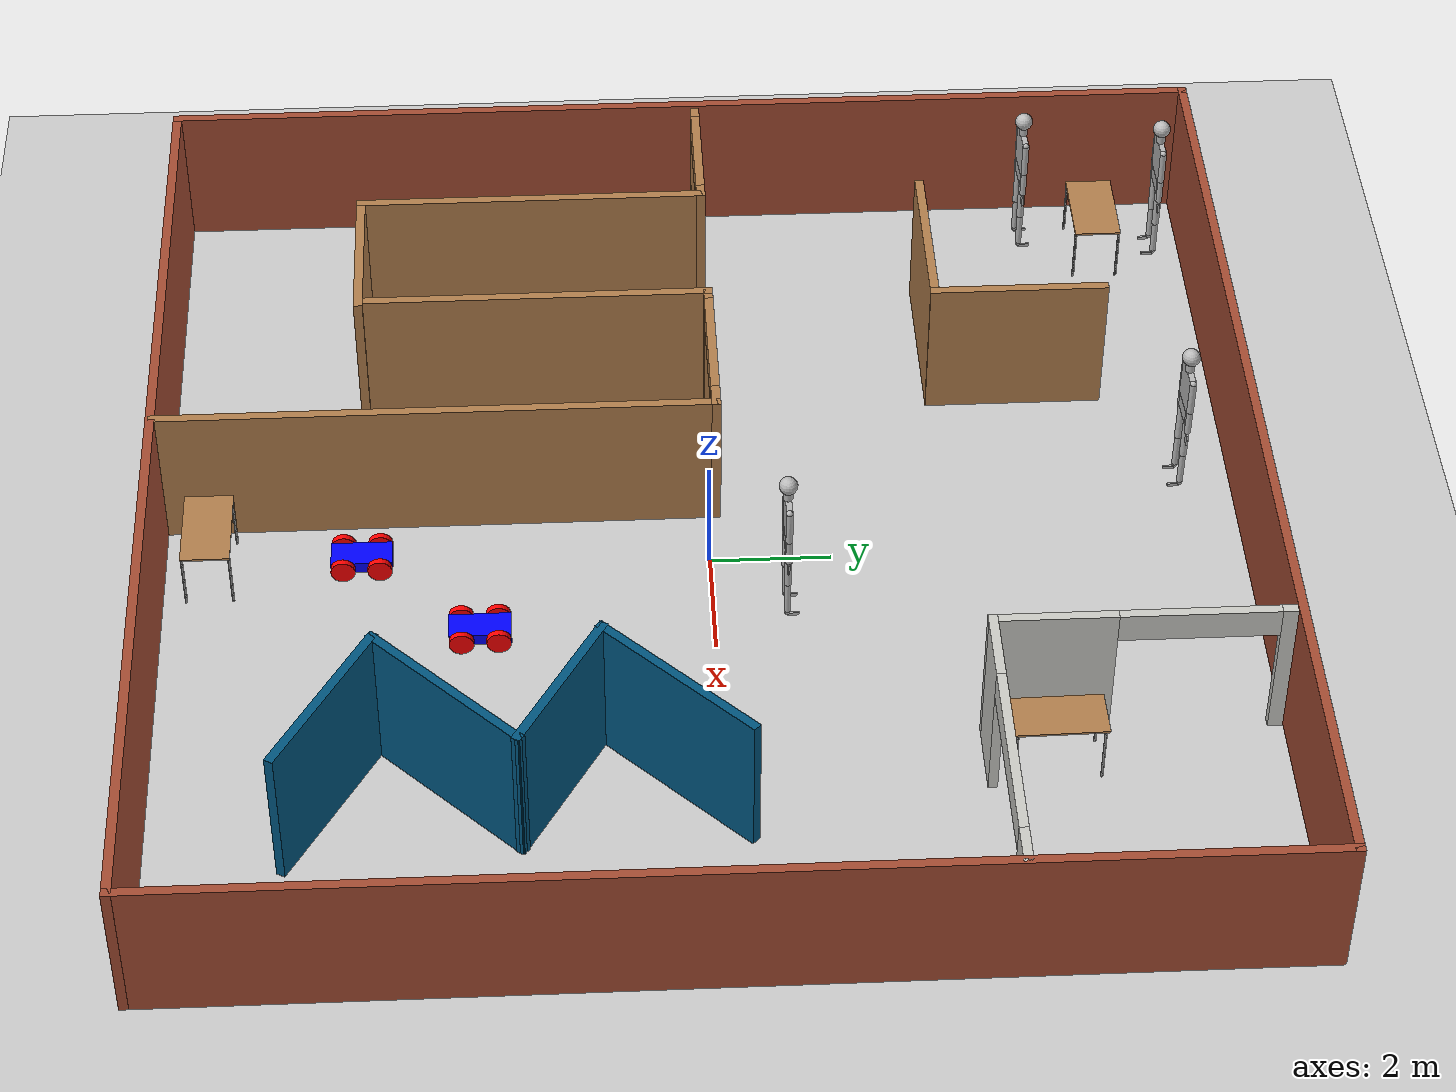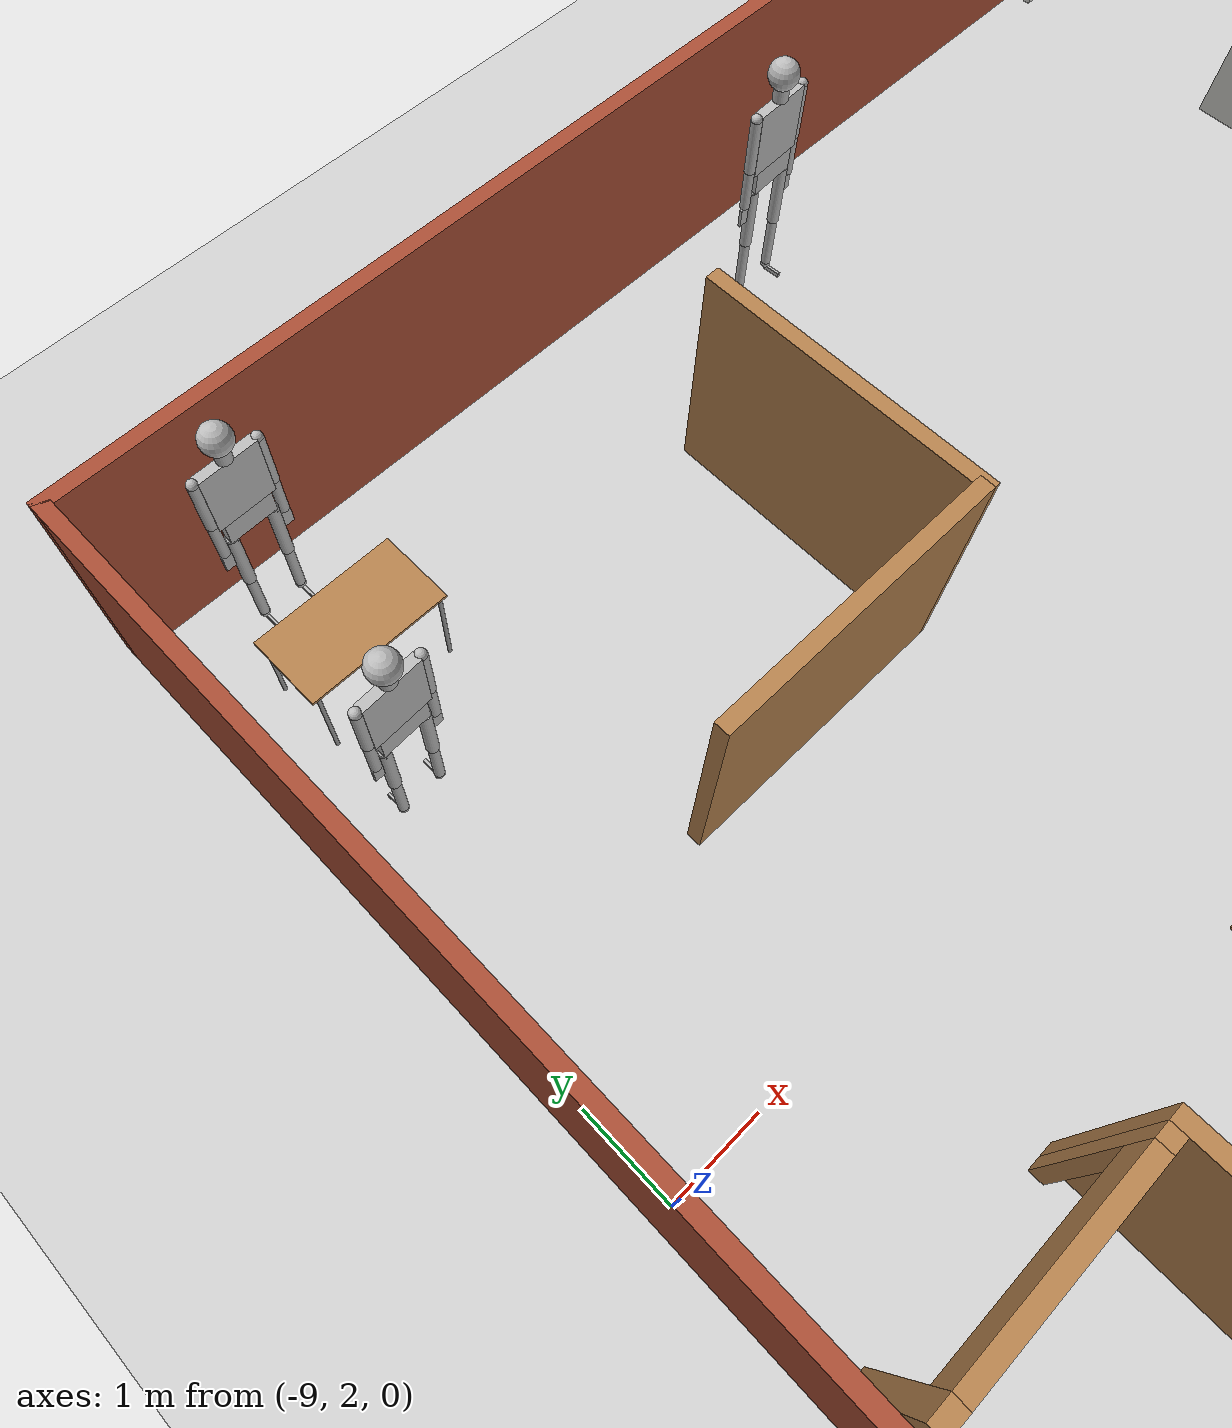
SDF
<sdf version="1.6">
 <world name="default">
  <plugin name="welcome" filename="libwelcome.so"/>
  <light name="sun" type="directional">
   <pose>0 0 10 0 -0 0</pose>
   <diffuse>0.8 0.8 0.8 1</diffuse>
   <specular>0.2 0.2 0.2 1</specular>
   <attenuation>
    <range>1000</range>
    <constant>0.9</constant>
    <linear>0.01</linear>
    <quadratic>0.001</quadratic>
   </attenuation>
   <direction>-0.5 0.1 -0.9</direction>
  </light>
  <model name="ground_plane">
   <static>1</static>
   <link name="link">
    <collision name="collision">
     <geometry><plane><normal>0 0 1</normal><size>100 100</size></plane></geometry>
     <surface>
      <contact><collide_bitmask>65535</collide_bitmask></contact>
      <friction><ode><mu>100</mu><mu2>50</mu2></ode></friction>
     </surface>
    </collision>
    <visual name="visual">
     <cast_shadows>0</cast_shadows>
     <geometry><plane><normal>0 0 1</normal><size>100 100</size></plane></geometry>
     <material>
      <script><uri>file://media/materials/scripts/gazebo.material</uri><name>Gazebo/Grey</name></script>
     </material>
    </visual>
   </link>
  </model>
  <gravity>0 0 -9.8</gravity>
  <magnetic_field>6e-06 2.3e-05 -4.2e-05</magnetic_field>
  <atmosphere type="adiabatic"/>
  <physics name="default_physics" default="0" type="ode">
   <max_step_size>0.001</max_step_size>
   <real_time_factor>1</real_time_factor>
   <real_time_update_rate>1000</real_time_update_rate>
  </physics>
  <scene><ambient>0.4 0.4 0.4 1</ambient><background>0.7 0.7 0.7 1</background><shadows>1</shadows></scene>
  <spherical_coordinates>
   <surface_model>EARTH_WGS84</surface_model>
   <latitude_deg>0</latitude_deg>
   <longitude_deg>0</longitude_deg>
   <elevation>0</elevation>
   <heading_deg>0</heading_deg>
  </spherical_coordinates>
  <model name="Building">
   <pose>-0.07708 -0.05076 0 0 -0 0</pose>
   <link name="Wall_0">
    <collision name="Wall_0_Collision">
     <geometry><box><size>18 0.15 2.5</size></box></geometry>
     <pose>0 0 1.25 0 -0 0</pose>
    </collision>
    <visual name="Wall_0_Visual">
     <pose>0 0 1.25 0 -0 0</pose>
     <geometry><box><size>18 0.15 2.5</size></box></geometry>
     <material>
      <script><uri>file://media/materials/scripts/gazebo.material</uri><name>Gazebo/Bricks</name></script>
      <ambient>1 1 1 1</ambient>
     </material>
     <meta><layer>0</layer></meta>
    </visual>
    <pose>-9.05 0 0 0 0 -1.5708</pose>
   </link>
   <link name="Wall_10">
    <collision name="Wall_10_Collision">
     <geometry><box><size>3.25 0.15 2.5</size></box></geometry>
     <pose>0 0 1.25 0 -0 0</pose>
    </collision>
    <visual name="Wall_10_Visual">
     <pose>0 0 1.25 0 -0 0</pose>
     <geometry><box><size>3.25 0.15 2.5</size></box></geometry>
     <material>
      <script><uri>file://media/materials/scripts/gazebo.material</uri><name>Gazebo/Grey</name></script>
      <ambient>0 0.333333 0.498039 1</ambient>
     </material>
     <meta><layer>0</layer></meta>
    </visual>
    <pose>5.19182 -4.17437 0 0 -0 0.785398</pose>
   </link>
   <link name="Wall_11">
    <collision name="Wall_11_Collision">
     <geometry><box><size>2.75 0.15 2.5</size></box></geometry>
     <pose>0 0 1.25 0 -0 0</pose>
    </collision>
    <visual name="Wall_11_Visual">
     <pose>0 0 1.25 0 -0 0</pose>
     <geometry><box><size>2.75 0.15 2.5</size></box></geometry>
     <material>
      <script><uri>file://media/materials/scripts/gazebo.material</uri><name>Gazebo/Grey</name></script>
      <ambient>0 0.333333 0.498039 1</ambient>
     </material>
     <meta><layer>0</layer></meta>
    </visual>
    <pose>5.162 -2.42836 0 0 -0 2.61799</pose>
   </link>
   <link name="Wall_12">
    <collision name="Wall_12_Collision">
     <geometry><box><size>3.25 0.15 2.5</size></box></geometry>
     <pose>0 0 1.25 0 -0 0</pose>
    </collision>
    <visual name="Wall_12_Visual">
     <pose>0 0 1.25 0 -0 0</pose>
     <geometry><box><size>3.25 0.15 2.5</size></box></geometry>
     <material>
      <script><uri>file://media/materials/scripts/gazebo.material</uri><name>Gazebo/Grey</name></script>
      <ambient>0 0.333333 0.498039 1</ambient>
     </material>
     <meta><layer>0</layer></meta>
    </visual>
    <pose>5.13218 -0.682341 0 0 -0 0.785398</pose>
   </link>
   <link name="Wall_14">
    <collision name="Wall_14_Collision">
     <geometry><box><size>9.25 0.15 2.5</size></box></geometry>
     <pose>0 0 1.25 0 -0 0</pose>
    </collision>
    <visual name="Wall_14_Visual">
     <pose>0 0 1.25 0 -0 0</pose>
     <geometry><box><size>9.25 0.15 2.5</size></box></geometry>
     <material>
      <script><uri>file://media/materials/scripts/gazebo.material</uri><name>Gazebo/Wood</name></script>
      <ambient>1 1 1 1</ambient>
     </material>
     <meta><layer>0</layer></meta>
    </visual>
    <pose>-1.03338 -4.33899 0 0 -0 1.5708</pose>
   </link>
   <link name="Wall_16">
    <pose>-2.41412 0.21101 0 0 -0 3.14159</pose>
    <visual name="Wall_16_Visual_0">
     <pose>-1.22859 0 1.25 0 -0 0</pose>
     <geometry><box><size>0.454289 0.15 2.5</size></box></geometry>
     <material>
      <script><uri>file://media/materials/scripts/gazebo.material</uri><name>Gazebo/Wood</name></script>
      <ambient>1 1 1 1</ambient>
     </material>
     <meta><layer>0</layer></meta>
    </visual>
    <collision name="Wall_16_Collision_0">
     <geometry><box><size>0.454289 0.15 2.5</size></box></geometry>
     <pose>-1.22859 0 1.25 0 -0 0</pose>
    </collision>
    <visual name="Wall_16_Visual_1">
     <pose>1.34593 0 1.25 0 -0 0</pose>
     <geometry><box><size>0.219621 0.15 2.5</size></box></geometry>
     <material>
      <script><uri>file://media/materials/scripts/gazebo.material</uri><name>Gazebo/Wood</name></script>
      <ambient>1 1 1 1</ambient>
     </material>
     <meta><layer>0</layer></meta>
    </visual>
    <collision name="Wall_16_Collision_1">
     <geometry><box><size>0.219621 0.15 2.5</size></box></geometry>
     <pose>1.34593 0 1.25 0 -0 0</pose>
    </collision>
    <visual name="Wall_16_Visual_2">
     <pose>0.117334 0 2.25 0 -0 0</pose>
     <geometry><box><size>2.23756 0.15 0.5</size></box></geometry>
     <material>
      <script><uri>file://media/materials/scripts/gazebo.material</uri><name>Gazebo/Wood</name></script>
      <ambient>1 1 1 1</ambient>
     </material>
     <meta><layer>0</layer></meta>
    </visual>
    <collision name="Wall_16_Collision_2">
     <geometry><box><size>2.23756 0.15 0.5</size></box></geometry>
     <pose>0.117334 0 2.25 0 -0 0</pose>
    </collision>
   </link>
   <link name="Wall_17">
    <collision name="Wall_17_Collision">
     <geometry><box><size>6.00024 0.15 2.5</size></box></geometry>
     <pose>0 0 1.25 0 -0 0</pose>
    </collision>
    <visual name="Wall_17_Visual">
     <pose>0 0 1.25 0 -0 0</pose>
     <geometry><box><size>6.00024 0.15 2.5</size></box></geometry>
     <material>
      <script><uri>file://media/materials/scripts/gazebo.material</uri><name>Gazebo/Wood</name></script>
      <ambient>1 1 1 1</ambient>
     </material>
     <meta><layer>0</layer></meta>
    </visual>
    <pose>-3.84835 -2.71399 0 0 0 -1.5708</pose>
   </link>
   <link name="Wall_18">
    <collision name="Wall_18_Collision">
     <geometry><box><size>2.83853 0.15 2.5</size></box></geometry>
     <pose>0 0 1.25 0 -0 0</pose>
    </collision>
    <visual name="Wall_18_Visual">
     <pose>0 0 1.25 0 -0 0</pose>
     <geometry><box><size>2.83853 0.15 2.5</size></box></geometry>
     <material>
      <script><uri>file://media/materials/scripts/gazebo.material</uri><name>Gazebo/Wood</name></script>
      <ambient>1 1 1 1</ambient>
     </material>
     <meta><layer>0</layer></meta>
    </visual>
    <pose>-5.13912 -5.63899 0 0 -0 3.14159</pose>
   </link>
   <link name="Wall_19">
    <collision name="Wall_19_Collision">
     <geometry><box><size>6 0.15 2.5</size></box></geometry>
     <pose>0 0 1.25 0 -0 0</pose>
    </collision>
    <visual name="Wall_19_Visual">
     <pose>0 0 1.25 0 -0 0</pose>
     <geometry><box><size>6 0.15 2.5</size></box></geometry>
     <material>
      <script><uri>file://media/materials/scripts/gazebo.material</uri><name>Gazebo/Wood</name></script>
      <ambient>1 1 1 1</ambient>
     </material>
     <meta><layer>0</layer></meta>
    </visual>
    <pose>-6.48338 -2.71399 0 0 -0 1.5708</pose>
   </link>
   <link name="Wall_2">
    <collision name="Wall_2_Collision">
     <geometry><box><size>18.25 0.15 2.5</size></box></geometry>
     <pose>0 0 1.25 0 -0 0</pose>
    </collision>
    <visual name="Wall_2_Visual">
     <pose>0 0 1.25 0 -0 0</pose>
     <geometry><box><size>18.25 0.15 2.5</size></box></geometry>
     <material>
      <script><uri>file://media/materials/scripts/gazebo.material</uri><name>Gazebo/Bricks</name></script>
      <ambient>1 1 1 1</ambient>
     </material>
     <meta><layer>0</layer></meta>
    </visual>
    <pose>0 8.925 0 0 -0 0</pose>
   </link>
   <link name="Wall_20">
    <pose>-7.65838 0.21101 0 0 -0 3.14159</pose>
    <visual name="Wall_20_Visual_0">
     <pose>-1.09948 0 1.25 0 -0 0</pose>
     <geometry><box><size>0.301036 0.15 2.5</size></box></geometry>
     <material>
      <script><uri>file://media/materials/scripts/gazebo.material</uri><name>Gazebo/Wood</name></script>
      <ambient>1 1 1 1</ambient>
     </material>
     <meta><layer>0</layer></meta>
    </visual>
    <collision name="Wall_20_Collision_0">
     <geometry><box><size>0.301036 0.15 2.5</size></box></geometry>
     <pose>-1.09948 0 1.25 0 -0 0</pose>
    </collision>
    <visual name="Wall_20_Visual_1">
     <pose>1.13554 0 1.25 0 -0 0</pose>
     <geometry><box><size>0.228914 0.15 2.5</size></box></geometry>
     <material>
      <script><uri>file://media/materials/scripts/gazebo.material</uri><name>Gazebo/Wood</name></script>
      <ambient>1 1 1 1</ambient>
     </material>
     <meta><layer>0</layer></meta>
    </visual>
    <collision name="Wall_20_Collision_1">
     <geometry><box><size>0.228914 0.15 2.5</size></box></geometry>
     <pose>1.13554 0 1.25 0 -0 0</pose>
    </collision>
    <visual name="Wall_20_Visual_2">
     <pose>0.036061 0 2.25 0 -0 0</pose>
     <geometry><box><size>1.97005 0.15 0.5</size></box></geometry>
     <material>
      <script><uri>file://media/materials/scripts/gazebo.material</uri><name>Gazebo/Wood</name></script>
      <ambient>1 1 1 1</ambient>
     </material>
     <meta><layer>0</layer></meta>
    </visual>
    <collision name="Wall_20_Collision_2">
     <geometry><box><size>1.97005 0.15 0.5</size></box></geometry>
     <pose>0.036061 0 2.25 0 -0 0</pose>
    </collision>
   </link>
   <link name="Wall_22">
    <collision name="Wall_22_Collision">
     <geometry><box><size>3 0.15 2.5</size></box></geometry>
     <pose>0 0 1.25 0 -0 0</pose>
    </collision>
    <visual name="Wall_22_Visual">
     <pose>0 0 1.25 0 -0 0</pose>
     <geometry><box><size>3 0.15 2.5</size></box></geometry>
     <material>
      <script><uri>file://media/materials/scripts/gazebo.material</uri><name>Gazebo/Wood</name></script>
      <ambient>1 1 1 1</ambient>
     </material>
     <meta><layer>0</layer></meta>
    </visual>
    <pose>-5.14909 4.00511 0 0 -0 3.14159</pose>
   </link>
   <link name="Wall_24">
    <collision name="Wall_24_Collision">
     <geometry><box><size>3 0.15 2.5</size></box></geometry>
     <pose>0 0 1.25 0 -0 0</pose>
    </collision>
    <visual name="Wall_24_Visual">
     <pose>0 0 1.25 0 -0 0</pose>
     <geometry><box><size>3 0.15 2.5</size></box></geometry>
     <material>
      <script><uri>file://media/materials/scripts/gazebo.material</uri><name>Gazebo/Wood</name></script>
      <ambient>1 1 1 1</ambient>
     </material>
     <meta><layer>0</layer></meta>
    </visual>
    <pose>-3.67058 5.43011 0 0 -0 1.5708</pose>
   </link>
   <link name="Wall_3">
    <collision name="Wall_3_Collision">
     <geometry><box><size>18 0.15 2.5</size></box></geometry>
     <pose>0 0 1.25 0 -0 0</pose>
    </collision>
    <visual name="Wall_3_Visual">
     <pose>0 0 1.25 0 -0 0</pose>
     <geometry><box><size>18 0.15 2.5</size></box></geometry>
     <material>
      <script><uri>file://media/materials/scripts/gazebo.material</uri><name>Gazebo/Bricks</name></script>
      <ambient>1 1 1 1</ambient>
     </material>
     <meta><layer>0</layer></meta>
    </visual>
    <pose>9.05 0 0 0 0 -1.5708</pose>
   </link>
   <link name="Wall_4">
    <collision name="Wall_4_Collision">
     <geometry><box><size>18.25 0.15 2.5</size></box></geometry>
     <pose>0 0 1.25 0 -0 0</pose>
    </collision>
    <visual name="Wall_4_Visual">
     <pose>0 0 1.25 0 -0 0</pose>
     <geometry><box><size>18.25 0.15 2.5</size></box></geometry>
     <material>
      <script><uri>file://media/materials/scripts/gazebo.material</uri><name>Gazebo/Bricks</name></script>
      <ambient>1 1 1 1</ambient>
     </material>
     <meta><layer>0</layer></meta>
    </visual>
    <pose>0 -8.925 0 0 -0 3.14159</pose>
   </link>
   <link name="Wall_6">
    <pose>4.15636 6.46683 0 0 0 -1.5708</pose>
    <visual name="Wall_6_Visual_0">
     <pose>-2.25486 0 1.25 0 -0 0</pose>
     <geometry><box><size>0.240278 0.15 2.5</size></box></geometry>
     <material>
      <script><uri>file://media/materials/scripts/gazebo.material</uri><name>Gazebo/CeilingTiled</name></script>
      <ambient>1 1 1 1</ambient>
     </material>
     <meta><layer>0</layer></meta>
    </visual>
    <collision name="Wall_6_Collision_0">
     <geometry><box><size>0.240278 0.15 2.5</size></box></geometry>
     <pose>-2.25486 0 1.25 0 -0 0</pose>
    </collision>
    <visual name="Wall_6_Visual_1">
     <pose>1.37268 0 1.25 0 -0 0</pose>
     <geometry><box><size>2.00465 0.15 2.5</size></box></geometry>
     <material>
      <script><uri>file://media/materials/scripts/gazebo.material</uri><name>Gazebo/CeilingTiled</name></script>
      <ambient>1 1 1 1</ambient>
     </material>
     <meta><layer>0</layer></meta>
    </visual>
    <collision name="Wall_6_Collision_1">
     <geometry><box><size>2.00465 0.15 2.5</size></box></geometry>
     <pose>1.37268 0 1.25 0 -0 0</pose>
    </collision>
    <visual name="Wall_6_Visual_2">
     <pose>-0.882184 0 2.25 0 -0 0</pose>
     <geometry><box><size>2.50508 0.15 0.5</size></box></geometry>
     <material>
      <script><uri>file://media/materials/scripts/gazebo.material</uri><name>Gazebo/CeilingTiled</name></script>
      <ambient>1 1 1 1</ambient>
     </material>
     <meta><layer>0</layer></meta>
    </visual>
    <collision name="Wall_6_Collision_2">
     <geometry><box><size>2.50508 0.15 0.5</size></box></geometry>
     <pose>-0.882184 0 2.25 0 -0 0</pose>
    </collision>
   </link>
   <link name="Wall_7">
    <pose>6.58136 4.16684 0 0 -0 0</pose>
    <visual name="Wall_7_Visual_0">
     <pose>-1.87159 0 1.25 0 -0 0</pose>
     <geometry><box><size>1.25683 0.15 2.5</size></box></geometry>
     <material>
      <script><uri>file://media/materials/scripts/gazebo.material</uri><name>Gazebo/CeilingTiled</name></script>
      <ambient>1 1 1 1</ambient>
     </material>
     <meta><layer>0</layer></meta>
    </visual>
    <collision name="Wall_7_Collision_0">
     <geometry><box><size>1.25683 0.15 2.5</size></box></geometry>
     <pose>-1.87159 0 1.25 0 -0 0</pose>
    </collision>
    <visual name="Wall_7_Visual_1">
     <pose>2.17521 0 1.25 0 -0 0</pose>
     <geometry><box><size>0.649571 0.15 2.5</size></box></geometry>
     <material>
      <script><uri>file://media/materials/scripts/gazebo.material</uri><name>Gazebo/CeilingTiled</name></script>
      <ambient>1 1 1 1</ambient>
     </material>
     <meta><layer>0</layer></meta>
    </visual>
    <collision name="Wall_7_Collision_1">
     <geometry><box><size>0.649571 0.15 2.5</size></box></geometry>
     <pose>2.17521 0 1.25 0 -0 0</pose>
    </collision>
    <visual name="Wall_7_Visual_2">
     <pose>0.303627 0 2.25 0 -0 0</pose>
     <geometry><box><size>3.0936 0.15 0.5</size></box></geometry>
     <material>
      <script><uri>file://media/materials/scripts/gazebo.material</uri><name>Gazebo/CeilingTiled</name></script>
      <ambient>1 1 1 1</ambient>
     </material>
     <meta><layer>0</layer></meta>
    </visual>
    <collision name="Wall_7_Collision_2">
     <geometry><box><size>3.0936 0.15 0.5</size></box></geometry>
     <pose>0.303627 0 2.25 0 -0 0</pose>
    </collision>
   </link>
   <link name="Wall_9">
    <collision name="Wall_9_Collision">
     <geometry><box><size>3 0.15 2.5</size></box></geometry>
     <pose>0 0 1.25 0 -0 0</pose>
    </collision>
    <visual name="Wall_9_Visual">
     <pose>0 0 1.25 0 -0 0</pose>
     <geometry><box><size>3 0.15 2.5</size></box></geometry>
     <material>
      <script><uri>file://media/materials/scripts/gazebo.material</uri><name>Gazebo/Grey</name></script>
      <ambient>0 0.333333 0.498039 1</ambient>
     </material>
     <meta><layer>0</layer></meta>
    </visual>
    <pose>5.32989 -5.98289 0 0 -0 2.61799</pose>
   </link>
   <static>1</static>
  </model>
  <model name="robot">
   <link name="link_0">
    <inertial>
     <mass>1</mass>
     <inertia>
      <ixx>0.166667</ixx>
      <ixy>0</ixy>
      <ixz>0</ixz>
      <iyy>0.166667</iyy>
      <iyz>0</iyz>
      <izz>0.166667</izz>
     </inertia>
    </inertial>
    <visual name="visual">
     <geometry><box><size>1 0.5 0.2</size></box></geometry>
     <material>
      <lighting>1</lighting>
      <script><uri>file://media/materials/scripts/gazebo.material</uri><name>Gazebo/Grey</name></script>
      <shader type="pixel"><normal_map>__default__</normal_map></shader>
      <ambient>0 0 1 1</ambient>
      <diffuse>0 0 1 1</diffuse>
      <specular>0 0 1 1</specular>
      <emissive>0 0 0 1</emissive>
     </material>
    </visual>
    <collision name="collision">
     <geometry><box><size>1 0.5 0.2</size></box></geometry>
     <surface>
      <friction>
       <ode><mu>1</mu><mu2>1</mu2><fdir1>0 0 0</fdir1><slip1>0</slip1><slip2>0</slip2></ode>
       <torsional>
        <coefficient>1</coefficient>
        <patch_radius>0</patch_radius>
        <surface_radius>0</surface_radius>
        <use_patch_radius>1</use_patch_radius>
        <ode><slip>0</slip></ode>
       </torsional>
      </friction>
      <bounce><restitution_coefficient>0</restitution_coefficient><threshold>1e+06</threshold></bounce>
      <contact>
       <collide_without_contact>0</collide_without_contact>
       <collide_without_contact_bitmask>1</collide_without_contact_bitmask>
       <collide_bitmask>1</collide_bitmask>
       <ode>
        <soft_cfm>0</soft_cfm>
        <soft_erp>0.2</soft_erp>
        <kp>1e+13</kp>
        <kd>1</kd>
        <max_vel>0.01</max_vel>
        <min_depth>0</min_depth>
       </ode>
       <bullet>
        <split_impulse>1</split_impulse>
        <split_impulse_penetration_threshold>-0.01</split_impulse_penetration_threshold>
        <soft_cfm>0</soft_cfm>
        <soft_erp>0.2</soft_erp>
        <kp>1e+13</kp>
        <kd>1</kd>
       </bullet>
      </contact>
     </surface>
    </collision>
   </link>
   <link name="link_1">
    <inertial>
     <mass>1</mass>
     <inertia><ixx>0.145833</ixx><ixy>0</ixy><ixz>0</ixz><iyy>0.145833</iyy><iyz>0</iyz><izz>0.125</izz></inertia>
    </inertial>
    <pose>-0.3 -0.300019 0 1.5707 -0 0</pose>
    <visual name="visual">
     <geometry><cylinder><radius>0.2</radius><length>0.1</length></cylinder></geometry>
     <material>
      <lighting>1</lighting>
      <script><uri>file://media/materials/scripts/gazebo.material</uri><name>Gazebo/Grey</name></script>
      <shader type="pixel"><normal_map>__default__</normal_map></shader>
      <ambient>1 0.3 0 1</ambient>
      <diffuse>1 0 0 1</diffuse>
      <specular>1 0 0 1</specular>
      <emissive>0 0 0 1</emissive>
     </material>
    </visual>
    <collision name="collision">
     <geometry><cylinder><radius>0.2</radius><length>0.1</length></cylinder></geometry>
     <surface>
      <friction>
       <ode><mu>1</mu><mu2>1</mu2><fdir1>0 0 0</fdir1><slip1>0</slip1><slip2>0</slip2></ode>
       <torsional>
        <coefficient>1</coefficient>
        <patch_radius>0</patch_radius>
        <surface_radius>0</surface_radius>
        <use_patch_radius>1</use_patch_radius>
        <ode><slip>0</slip></ode>
       </torsional>
      </friction>
      <bounce><restitution_coefficient>0</restitution_coefficient><threshold>1e+06</threshold></bounce>
      <contact>
       <collide_without_contact>0</collide_without_contact>
       <collide_without_contact_bitmask>1</collide_without_contact_bitmask>
       <collide_bitmask>1</collide_bitmask>
       <ode>
        <soft_cfm>0</soft_cfm>
        <soft_erp>0.2</soft_erp>
        <kp>1e+13</kp>
        <kd>1</kd>
        <max_vel>0.01</max_vel>
        <min_depth>0</min_depth>
       </ode>
       <bullet>
        <split_impulse>1</split_impulse>
        <split_impulse_penetration_threshold>-0.01</split_impulse_penetration_threshold>
        <soft_cfm>0</soft_cfm>
        <soft_erp>0.2</soft_erp>
        <kp>1e+13</kp>
        <kd>1</kd>
       </bullet>
      </contact>
     </surface>
    </collision>
   </link>
   <link name="link_1_clone">
    <inertial>
     <mass>1</mass>
     <inertia><ixx>0.145833</ixx><ixy>0</ixy><ixz>0</ixz><iyy>0.145833</iyy><iyz>0</iyz><izz>0.125</izz></inertia>
    </inertial>
    <pose>-0.3 0.300019 0 1.5707 -0 0</pose>
    <visual name="visual">
     <geometry><cylinder><radius>0.2</radius><length>0.1</length></cylinder></geometry>
     <material>
      <lighting>1</lighting>
      <script><uri>file://media/materials/scripts/gazebo.material</uri><name>Gazebo/Grey</name></script>
      <shader type="pixel"><normal_map>__default__</normal_map></shader>
      <ambient>1 0.3 0 1</ambient>
      <diffuse>1 0 0 1</diffuse>
      <specular>1 0 0 1</specular>
      <emissive>0 0 0 1</emissive>
     </material>
    </visual>
    <collision name="collision">
     <geometry><cylinder><radius>0.2</radius><length>0.1</length></cylinder></geometry>
     <surface>
      <friction>
       <ode><mu>1</mu><mu2>1</mu2><fdir1>0 0 0</fdir1><slip1>0</slip1><slip2>0</slip2></ode>
       <torsional>
        <coefficient>1</coefficient>
        <patch_radius>0</patch_radius>
        <surface_radius>0</surface_radius>
        <use_patch_radius>1</use_patch_radius>
        <ode><slip>0</slip></ode>
       </torsional>
      </friction>
      <bounce><restitution_coefficient>0</restitution_coefficient><threshold>1e+06</threshold></bounce>
      <contact>
       <collide_without_contact>0</collide_without_contact>
       <collide_without_contact_bitmask>1</collide_without_contact_bitmask>
       <collide_bitmask>1</collide_bitmask>
       <ode>
        <soft_cfm>0</soft_cfm>
        <soft_erp>0.2</soft_erp>
        <kp>1e+13</kp>
        <kd>1</kd>
        <max_vel>0.01</max_vel>
        <min_depth>0</min_depth>
       </ode>
       <bullet>
        <split_impulse>1</split_impulse>
        <split_impulse_penetration_threshold>-0.01</split_impulse_penetration_threshold>
        <soft_cfm>0</soft_cfm>
        <soft_erp>0.2</soft_erp>
        <kp>1e+13</kp>
        <kd>1</kd>
       </bullet>
      </contact>
     </surface>
    </collision>
   </link>
   <link name="link_1_clone_0">
    <inertial>
     <mass>1</mass>
     <inertia><ixx>0.145833</ixx><ixy>0</ixy><ixz>0</ixz><iyy>0.145833</iyy><iyz>0</iyz><izz>0.125</izz></inertia>
    </inertial>
    <pose>0.3 0.300019 0 1.5707 -0 0</pose>
    <visual name="visual">
     <geometry><cylinder><radius>0.2</radius><length>0.1</length></cylinder></geometry>
     <material>
      <lighting>1</lighting>
      <script><uri>file://media/materials/scripts/gazebo.material</uri><name>Gazebo/Grey</name></script>
      <shader type="pixel"><normal_map>__default__</normal_map></shader>
      <ambient>1 0.3 0 1</ambient>
      <diffuse>1 0 0 1</diffuse>
      <specular>1 0 0 1</specular>
      <emissive>0 0 0 1</emissive>
     </material>
    </visual>
    <collision name="collision">
     <geometry><cylinder><radius>0.2</radius><length>0.1</length></cylinder></geometry>
     <surface>
      <friction>
       <ode><mu>1</mu><mu2>1</mu2><fdir1>0 0 0</fdir1><slip1>0</slip1><slip2>0</slip2></ode>
       <torsional>
        <coefficient>1</coefficient>
        <patch_radius>0</patch_radius>
        <surface_radius>0</surface_radius>
        <use_patch_radius>1</use_patch_radius>
        <ode><slip>0</slip></ode>
       </torsional>
      </friction>
      <bounce><restitution_coefficient>0</restitution_coefficient><threshold>1e+06</threshold></bounce>
      <contact>
       <collide_without_contact>0</collide_without_contact>
       <collide_without_contact_bitmask>1</collide_without_contact_bitmask>
       <collide_bitmask>1</collide_bitmask>
       <ode>
        <soft_cfm>0</soft_cfm>
        <soft_erp>0.2</soft_erp>
        <kp>1e+13</kp>
        <kd>1</kd>
        <max_vel>0.01</max_vel>
        <min_depth>0</min_depth>
       </ode>
       <bullet>
        <split_impulse>1</split_impulse>
        <split_impulse_penetration_threshold>-0.01</split_impulse_penetration_threshold>
        <soft_cfm>0</soft_cfm>
        <soft_erp>0.2</soft_erp>
        <kp>1e+13</kp>
        <kd>1</kd>
       </bullet>
      </contact>
     </surface>
    </collision>
   </link>
   <link name="link_1_clone_1">
    <inertial>
     <mass>1</mass>
     <inertia><ixx>0.145833</ixx><ixy>0</ixy><ixz>0</ixz><iyy>0.145833</iyy><iyz>0</iyz><izz>0.125</izz></inertia>
    </inertial>
    <pose>0.3 -0.300019 0 1.5707 -0 0</pose>
    <visual name="visual">
     <geometry><cylinder><radius>0.2</radius><length>0.1</length></cylinder></geometry>
     <material>
      <lighting>1</lighting>
      <script><uri>file://media/materials/scripts/gazebo.material</uri><name>Gazebo/Grey</name></script>
      <shader type="pixel"><normal_map>__default__</normal_map></shader>
      <ambient>1 0.3 0 1</ambient>
      <diffuse>1 0 0 1</diffuse>
      <specular>1 0 0 1</specular>
      <emissive>0 0 0 1</emissive>
     </material>
    </visual>
    <collision name="collision">
     <geometry><cylinder><radius>0.2</radius><length>0.1</length></cylinder></geometry>
     <surface>
      <friction>
       <ode><mu>1</mu><mu2>1</mu2><fdir1>0 0 0</fdir1><slip1>0</slip1><slip2>0</slip2></ode>
       <torsional>
        <coefficient>1</coefficient>
        <patch_radius>0</patch_radius>
        <surface_radius>0</surface_radius>
        <use_patch_radius>1</use_patch_radius>
        <ode><slip>0</slip></ode>
       </torsional>
      </friction>
      <bounce><restitution_coefficient>0</restitution_coefficient><threshold>1e+06</threshold></bounce>
      <contact>
       <collide_without_contact>0</collide_without_contact>
       <collide_without_contact_bitmask>1</collide_without_contact_bitmask>
       <collide_bitmask>1</collide_bitmask>
       <ode>
        <soft_cfm>0</soft_cfm>
        <soft_erp>0.2</soft_erp>
        <kp>1e+13</kp>
        <kd>1</kd>
        <max_vel>0.01</max_vel>
        <min_depth>0</min_depth>
       </ode>
       <bullet>
        <split_impulse>1</split_impulse>
        <split_impulse_penetration_threshold>-0.01</split_impulse_penetration_threshold>
        <soft_cfm>0</soft_cfm>
        <soft_erp>0.2</soft_erp>
        <kp>1e+13</kp>
        <kd>1</kd>
       </bullet>
      </contact>
     </surface>
    </collision>
   </link>
   <joint name="link_0_JOINT_0" type="revolute">
    <parent>link_0</parent>
    <child>link_1</child>
    <axis>
     <xyz>1 0 0</xyz>
     <limit>
      <lower>-1.79769e+308</lower>
      <upper>1.79769e+308</upper>
      <effort>-1</effort>
      <velocity>-1</velocity>
     </limit>
     <dynamics>
      <spring_reference>0</spring_reference>
      <spring_stiffness>0</spring_stiffness>
      <damping>0</damping>
     </dynamics>
     <use_parent_model_frame>0</use_parent_model_frame>
    </axis>
    <physics>
     <ode><limit><cfm>0</cfm><erp>0.2</erp></limit><suspension><cfm>0</cfm><erp>0.2</erp></suspension></ode>
    </physics>
   </joint>
   <joint name="link_0_JOINT_1" type="revolute">
    <parent>link_0</parent>
    <child>link_1_clone_0</child>
    <axis>
     <xyz>1 0 0</xyz>
     <limit>
      <lower>-1.79769e+308</lower>
      <upper>1.79769e+308</upper>
      <effort>-1</effort>
      <velocity>-1</velocity>
     </limit>
     <dynamics>
      <spring_reference>0</spring_reference>
      <spring_stiffness>0</spring_stiffness>
      <damping>0</damping>
     </dynamics>
     <use_parent_model_frame>0</use_parent_model_frame>
    </axis>
    <physics>
     <ode><limit><cfm>0</cfm><erp>0.2</erp></limit><suspension><cfm>0</cfm><erp>0.2</erp></suspension></ode>
    </physics>
   </joint>
   <joint name="link_0_JOINT_2" type="revolute">
    <parent>link_0</parent>
    <child>link_1_clone</child>
    <axis>
     <xyz>1 0 0</xyz>
     <limit>
      <lower>-1.79769e+308</lower>
      <upper>1.79769e+308</upper>
      <effort>-1</effort>
      <velocity>-1</velocity>
     </limit>
     <dynamics>
      <spring_reference>0</spring_reference>
      <spring_stiffness>0</spring_stiffness>
      <damping>0</damping>
     </dynamics>
     <use_parent_model_frame>0</use_parent_model_frame>
    </axis>
    <physics>
     <ode><limit><cfm>0</cfm><erp>0.2</erp></limit><suspension><cfm>0</cfm><erp>0.2</erp></suspension></ode>
    </physics>
   </joint>
   <joint name="link_0_JOINT_3" type="revolute">
    <parent>link_0</parent>
    <child>link_1_clone_1</child>
    <axis>
     <xyz>1 0 0</xyz>
     <limit>
      <lower>-1.79769e+308</lower>
      <upper>1.79769e+308</upper>
      <effort>-1</effort>
      <velocity>-1</velocity>
     </limit>
     <dynamics>
      <spring_reference>0</spring_reference>
      <spring_stiffness>0</spring_stiffness>
      <damping>0</damping>
     </dynamics>
     <use_parent_model_frame>0</use_parent_model_frame>
    </axis>
    <physics>
     <ode><limit><cfm>0</cfm><erp>0.2</erp></limit><suspension><cfm>0</cfm><erp>0.2</erp></suspension></ode>
    </physics>
   </joint>
   <static>0</static>
   <pose>-0.132377 -5.68418 0.2 0 -2e-06 -1.57541</pose>
  </model>
  <model name="robot_0">
   <link name="link_0">
    <inertial>
     <mass>1</mass>
     <inertia>
      <ixx>0.166667</ixx>
      <ixy>0</ixy>
      <ixz>0</ixz>
      <iyy>0.166667</iyy>
      <iyz>0</iyz>
      <izz>0.166667</izz>
     </inertia>
    </inertial>
    <visual name="visual">
     <geometry><box><size>1 0.5 0.2</size></box></geometry>
     <material>
      <lighting>1</lighting>
      <script><uri>file://media/materials/scripts/gazebo.material</uri><name>Gazebo/Grey</name></script>
      <shader type="pixel"><normal_map>__default__</normal_map></shader>
      <ambient>0 0 1 1</ambient>
      <diffuse>0 0 1 1</diffuse>
      <specular>0 0 1 1</specular>
      <emissive>0 0 0 1</emissive>
     </material>
    </visual>
    <collision name="collision">
     <geometry><box><size>1 0.5 0.2</size></box></geometry>
     <surface>
      <friction>
       <ode><mu>1</mu><mu2>1</mu2><fdir1>0 0 0</fdir1><slip1>0</slip1><slip2>0</slip2></ode>
       <torsional>
        <coefficient>1</coefficient>
        <patch_radius>0</patch_radius>
        <surface_radius>0</surface_radius>
        <use_patch_radius>1</use_patch_radius>
        <ode><slip>0</slip></ode>
       </torsional>
      </friction>
      <bounce><restitution_coefficient>0</restitution_coefficient><threshold>1e+06</threshold></bounce>
      <contact>
       <collide_without_contact>0</collide_without_contact>
       <collide_without_contact_bitmask>1</collide_without_contact_bitmask>
       <collide_bitmask>1</collide_bitmask>
       <ode>
        <soft_cfm>0</soft_cfm>
        <soft_erp>0.2</soft_erp>
        <kp>1e+13</kp>
        <kd>1</kd>
        <max_vel>0.01</max_vel>
        <min_depth>0</min_depth>
       </ode>
       <bullet>
        <split_impulse>1</split_impulse>
        <split_impulse_penetration_threshold>-0.01</split_impulse_penetration_threshold>
        <soft_cfm>0</soft_cfm>
        <soft_erp>0.2</soft_erp>
        <kp>1e+13</kp>
        <kd>1</kd>
       </bullet>
      </contact>
     </surface>
    </collision>
   </link>
   <link name="link_1">
    <inertial>
     <mass>1</mass>
     <inertia><ixx>0.145833</ixx><ixy>0</ixy><ixz>0</ixz><iyy>0.145833</iyy><iyz>0</iyz><izz>0.125</izz></inertia>
    </inertial>
    <pose>-0.3 -0.300019 0 1.5707 -0 0</pose>
    <visual name="visual">
     <geometry><cylinder><radius>0.2</radius><length>0.1</length></cylinder></geometry>
     <material>
      <lighting>1</lighting>
      <script><uri>file://media/materials/scripts/gazebo.material</uri><name>Gazebo/Grey</name></script>
      <shader type="pixel"><normal_map>__default__</normal_map></shader>
      <ambient>1 0.3 0 1</ambient>
      <diffuse>1 0 0 1</diffuse>
      <specular>1 0 0 1</specular>
      <emissive>0 0 0 1</emissive>
     </material>
    </visual>
    <collision name="collision">
     <geometry><cylinder><radius>0.2</radius><length>0.1</length></cylinder></geometry>
     <surface>
      <friction>
       <ode><mu>1</mu><mu2>1</mu2><fdir1>0 0 0</fdir1><slip1>0</slip1><slip2>0</slip2></ode>
       <torsional>
        <coefficient>1</coefficient>
        <patch_radius>0</patch_radius>
        <surface_radius>0</surface_radius>
        <use_patch_radius>1</use_patch_radius>
        <ode><slip>0</slip></ode>
       </torsional>
      </friction>
      <bounce><restitution_coefficient>0</restitution_coefficient><threshold>1e+06</threshold></bounce>
      <contact>
       <collide_without_contact>0</collide_without_contact>
       <collide_without_contact_bitmask>1</collide_without_contact_bitmask>
       <collide_bitmask>1</collide_bitmask>
       <ode>
        <soft_cfm>0</soft_cfm>
        <soft_erp>0.2</soft_erp>
        <kp>1e+13</kp>
        <kd>1</kd>
        <max_vel>0.01</max_vel>
        <min_depth>0</min_depth>
       </ode>
       <bullet>
        <split_impulse>1</split_impulse>
        <split_impulse_penetration_threshold>-0.01</split_impulse_penetration_threshold>
        <soft_cfm>0</soft_cfm>
        <soft_erp>0.2</soft_erp>
        <kp>1e+13</kp>
        <kd>1</kd>
       </bullet>
      </contact>
     </surface>
    </collision>
   </link>
   <link name="link_1_clone">
    <inertial>
     <mass>1</mass>
     <inertia><ixx>0.145833</ixx><ixy>0</ixy><ixz>0</ixz><iyy>0.145833</iyy><iyz>0</iyz><izz>0.125</izz></inertia>
    </inertial>
    <pose>-0.3 0.300019 0 1.5707 -0 0</pose>
    <visual name="visual">
     <geometry><cylinder><radius>0.2</radius><length>0.1</length></cylinder></geometry>
     <material>
      <lighting>1</lighting>
      <script><uri>file://media/materials/scripts/gazebo.material</uri><name>Gazebo/Grey</name></script>
      <shader type="pixel"><normal_map>__default__</normal_map></shader>
      <ambient>1 0.3 0 1</ambient>
      <diffuse>1 0 0 1</diffuse>
      <specular>1 0 0 1</specular>
      <emissive>0 0 0 1</emissive>
     </material>
    </visual>
    <collision name="collision">
     <geometry><cylinder><radius>0.2</radius><length>0.1</length></cylinder></geometry>
     <surface>
      <friction>
       <ode><mu>1</mu><mu2>1</mu2><fdir1>0 0 0</fdir1><slip1>0</slip1><slip2>0</slip2></ode>
       <torsional>
        <coefficient>1</coefficient>
        <patch_radius>0</patch_radius>
        <surface_radius>0</surface_radius>
        <use_patch_radius>1</use_patch_radius>
        <ode><slip>0</slip></ode>
       </torsional>
      </friction>
      <bounce><restitution_coefficient>0</restitution_coefficient><threshold>1e+06</threshold></bounce>
      <contact>
       <collide_without_contact>0</collide_without_contact>
       <collide_without_contact_bitmask>1</collide_without_contact_bitmask>
       <collide_bitmask>1</collide_bitmask>
       <ode>
        <soft_cfm>0</soft_cfm>
        <soft_erp>0.2</soft_erp>
        <kp>1e+13</kp>
        <kd>1</kd>
        <max_vel>0.01</max_vel>
        <min_depth>0</min_depth>
       </ode>
       <bullet>
        <split_impulse>1</split_impulse>
        <split_impulse_penetration_threshold>-0.01</split_impulse_penetration_threshold>
        <soft_cfm>0</soft_cfm>
        <soft_erp>0.2</soft_erp>
        <kp>1e+13</kp>
        <kd>1</kd>
       </bullet>
      </contact>
     </surface>
    </collision>
   </link>
   <link name="link_1_clone_0">
    <inertial>
     <mass>1</mass>
     <inertia><ixx>0.145833</ixx><ixy>0</ixy><ixz>0</ixz><iyy>0.145833</iyy><iyz>0</iyz><izz>0.125</izz></inertia>
    </inertial>
    <pose>0.3 0.300019 0 1.5707 -0 0</pose>
    <visual name="visual">
     <geometry><cylinder><radius>0.2</radius><length>0.1</length></cylinder></geometry>
     <material>
      <lighting>1</lighting>
      <script><uri>file://media/materials/scripts/gazebo.material</uri><name>Gazebo/Grey</name></script>
      <shader type="pixel"><normal_map>__default__</normal_map></shader>
      <ambient>1 0.3 0 1</ambient>
      <diffuse>1 0 0 1</diffuse>
      <specular>1 0 0 1</specular>
      <emissive>0 0 0 1</emissive>
     </material>
    </visual>
    <collision name="collision">
     <geometry><cylinder><radius>0.2</radius><length>0.1</length></cylinder></geometry>
     <surface>
      <friction>
       <ode><mu>1</mu><mu2>1</mu2><fdir1>0 0 0</fdir1><slip1>0</slip1><slip2>0</slip2></ode>
       <torsional>
        <coefficient>1</coefficient>
        <patch_radius>0</patch_radius>
        <surface_radius>0</surface_radius>
        <use_patch_radius>1</use_patch_radius>
        <ode><slip>0</slip></ode>
       </torsional>
      </friction>
      <bounce><restitution_coefficient>0</restitution_coefficient><threshold>1e+06</threshold></bounce>
      <contact>
       <collide_without_contact>0</collide_without_contact>
       <collide_without_contact_bitmask>1</collide_without_contact_bitmask>
       <collide_bitmask>1</collide_bitmask>
       <ode>
        <soft_cfm>0</soft_cfm>
        <soft_erp>0.2</soft_erp>
        <kp>1e+13</kp>
        <kd>1</kd>
        <max_vel>0.01</max_vel>
        <min_depth>0</min_depth>
       </ode>
       <bullet>
        <split_impulse>1</split_impulse>
        <split_impulse_penetration_threshold>-0.01</split_impulse_penetration_threshold>
        <soft_cfm>0</soft_cfm>
        <soft_erp>0.2</soft_erp>
        <kp>1e+13</kp>
        <kd>1</kd>
       </bullet>
      </contact>
     </surface>
    </collision>
   </link>
   <link name="link_1_clone_1">
    <inertial>
     <mass>1</mass>
     <inertia><ixx>0.145833</ixx><ixy>0</ixy><ixz>0</ixz><iyy>0.145833</iyy><iyz>0</iyz><izz>0.125</izz></inertia>
    </inertial>
    <pose>0.3 -0.300019 0 1.5707 -0 0</pose>
    <visual name="visual">
     <geometry><cylinder><radius>0.2</radius><length>0.1</length></cylinder></geometry>
     <material>
      <lighting>1</lighting>
      <script><uri>file://media/materials/scripts/gazebo.material</uri><name>Gazebo/Grey</name></script>
      <shader type="pixel"><normal_map>__default__</normal_map></shader>
      <ambient>1 0.3 0 1</ambient>
      <diffuse>1 0 0 1</diffuse>
      <specular>1 0 0 1</specular>
      <emissive>0 0 0 1</emissive>
     </material>
    </visual>
    <collision name="collision">
     <geometry><cylinder><radius>0.2</radius><length>0.1</length></cylinder></geometry>
     <surface>
      <friction>
       <ode><mu>1</mu><mu2>1</mu2><fdir1>0 0 0</fdir1><slip1>0</slip1><slip2>0</slip2></ode>
       <torsional>
        <coefficient>1</coefficient>
        <patch_radius>0</patch_radius>
        <surface_radius>0</surface_radius>
        <use_patch_radius>1</use_patch_radius>
        <ode><slip>0</slip></ode>
       </torsional>
      </friction>
      <bounce><restitution_coefficient>0</restitution_coefficient><threshold>1e+06</threshold></bounce>
      <contact>
       <collide_without_contact>0</collide_without_contact>
       <collide_without_contact_bitmask>1</collide_without_contact_bitmask>
       <collide_bitmask>1</collide_bitmask>
       <ode>
        <soft_cfm>0</soft_cfm>
        <soft_erp>0.2</soft_erp>
        <kp>1e+13</kp>
        <kd>1</kd>
        <max_vel>0.01</max_vel>
        <min_depth>0</min_depth>
       </ode>
       <bullet>
        <split_impulse>1</split_impulse>
        <split_impulse_penetration_threshold>-0.01</split_impulse_penetration_threshold>
        <soft_cfm>0</soft_cfm>
        <soft_erp>0.2</soft_erp>
        <kp>1e+13</kp>
        <kd>1</kd>
       </bullet>
      </contact>
     </surface>
    </collision>
   </link>
   <joint name="link_0_JOINT_0" type="revolute">
    <parent>link_0</parent>
    <child>link_1</child>
    <axis>
     <xyz>1 0 0</xyz>
     <limit>
      <lower>-1.79769e+308</lower>
      <upper>1.79769e+308</upper>
      <effort>-1</effort>
      <velocity>-1</velocity>
     </limit>
     <dynamics>
      <spring_reference>0</spring_reference>
      <spring_stiffness>0</spring_stiffness>
      <damping>0</damping>
     </dynamics>
     <use_parent_model_frame>0</use_parent_model_frame>
    </axis>
    <physics>
     <ode><limit><cfm>0</cfm><erp>0.2</erp></limit><suspension><cfm>0</cfm><erp>0.2</erp></suspension></ode>
    </physics>
   </joint>
   <joint name="link_0_JOINT_1" type="revolute">
    <parent>link_0</parent>
    <child>link_1_clone_0</child>
    <axis>
     <xyz>1 0 0</xyz>
     <limit>
      <lower>-1.79769e+308</lower>
      <upper>1.79769e+308</upper>
      <effort>-1</effort>
      <velocity>-1</velocity>
     </limit>
     <dynamics>
      <spring_reference>0</spring_reference>
      <spring_stiffness>0</spring_stiffness>
      <damping>0</damping>
     </dynamics>
     <use_parent_model_frame>0</use_parent_model_frame>
    </axis>
    <physics>
     <ode><limit><cfm>0</cfm><erp>0.2</erp></limit><suspension><cfm>0</cfm><erp>0.2</erp></suspension></ode>
    </physics>
   </joint>
   <joint name="link_0_JOINT_2" type="revolute">
    <parent>link_0</parent>
    <child>link_1_clone</child>
    <axis>
     <xyz>1 0 0</xyz>
     <limit>
      <lower>-1.79769e+308</lower>
      <upper>1.79769e+308</upper>
      <effort>-1</effort>
      <velocity>-1</velocity>
     </limit>
     <dynamics>
      <spring_reference>0</spring_reference>
      <spring_stiffness>0</spring_stiffness>
      <damping>0</damping>
     </dynamics>
     <use_parent_model_frame>0</use_parent_model_frame>
    </axis>
    <physics>
     <ode><limit><cfm>0</cfm><erp>0.2</erp></limit><suspension><cfm>0</cfm><erp>0.2</erp></suspension></ode>
    </physics>
   </joint>
   <joint name="link_0_JOINT_3" type="revolute">
    <parent>link_0</parent>
    <child>link_1_clone_1</child>
    <axis>
     <xyz>1 0 0</xyz>
     <limit>
      <lower>-1.79769e+308</lower>
      <upper>1.79769e+308</upper>
      <effort>-1</effort>
      <velocity>-1</velocity>
     </limit>
     <dynamics>
      <spring_reference>0</spring_reference>
      <spring_stiffness>0</spring_stiffness>
      <damping>0</damping>
     </dynamics>
     <use_parent_model_frame>0</use_parent_model_frame>
    </axis>
    <physics>
     <ode><limit><cfm>0</cfm><erp>0.2</erp></limit><suspension><cfm>0</cfm><erp>0.2</erp></suspension></ode>
    </physics>
   </joint>
   <static>0</static>
   <pose>1.62014 -3.75854 0.199997 0 -8e-06 -1.56333</pose>
  </model>
  <model name="table">
   <static>1</static>
   <link name="link">
    <collision name="surface">
     <pose>0 0 1 0 -0 0</pose>
     <geometry><box><size>1.5 0.8 0.03</size></box></geometry>
     <surface><friction><ode><mu>0.6</mu><mu2>0.6</mu2></ode></friction></surface>
    </collision>
    <visual name="visual1">
     <pose>0 0 1 0 -0 0</pose>
     <geometry><box><size>1.5 0.8 0.03</size></box></geometry>
     <material>
      <script><uri>file://media/materials/scripts/gazebo.material</uri><name>Gazebo/Wood</name></script>
     </material>
    </visual>
    <collision name="front_left_leg">
     <pose>0.68 0.38 0.5 0 -0 0</pose>
     <geometry><cylinder><radius>0.02</radius><length>1</length></cylinder></geometry>
    </collision>
    <visual name="front_left_leg">
     <pose>0.68 0.38 0.5 0 -0 0</pose>
     <geometry><cylinder><radius>0.02</radius><length>1</length></cylinder></geometry>
     <material>
      <script><uri>file://media/materials/scripts/gazebo.material</uri><name>Gazebo/Grey</name></script>
     </material>
    </visual>
    <collision name="front_right_leg">
     <pose>0.68 -0.38 0.5 0 -0 0</pose>
     <geometry><cylinder><radius>0.02</radius><length>1</length></cylinder></geometry>
    </collision>
    <visual name="front_right_leg">
     <pose>0.68 -0.38 0.5 0 -0 0</pose>
     <geometry><cylinder><radius>0.02</radius><length>1</length></cylinder></geometry>
     <material>
      <script><uri>file://media/materials/scripts/gazebo.material</uri><name>Gazebo/Grey</name></script>
     </material>
    </visual>
    <collision name="back_right_leg">
     <pose>-0.68 -0.38 0.5 0 -0 0</pose>
     <geometry><cylinder><radius>0.02</radius><length>1</length></cylinder></geometry>
    </collision>
    <visual name="back_right_leg">
     <pose>-0.68 -0.38 0.5 0 -0 0</pose>
     <geometry><cylinder><radius>0.02</radius><length>1</length></cylinder></geometry>
     <material>
      <script><uri>file://media/materials/scripts/gazebo.material</uri><name>Gazebo/Grey</name></script>
     </material>
    </visual>
    <collision name="back_left_leg">
     <pose>-0.68 0.38 0.5 0 -0 0</pose>
     <geometry><cylinder><radius>0.02</radius><length>1</length></cylinder></geometry>
    </collision>
    <visual name="back_left_leg">
     <pose>-0.68 0.38 0.5 0 -0 0</pose>
     <geometry><cylinder><radius>0.02</radius><length>1</length></cylinder></geometry>
     <material>
      <script><uri>file://media/materials/scripts/gazebo.material</uri><name>Gazebo/Grey</name></script>
     </material>
    </visual>
   </link>
   <pose>-0.100028 -8.14185 0 0 -0 0</pose>
  </model>
  <model name="table_0">
   <static>1</static>
   <link name="link">
    <collision name="surface">
     <pose>0 0 1 0 -0 0</pose>
     <geometry><box><size>1.5 0.8 0.03</size></box></geometry>
     <surface><friction><ode><mu>0.6</mu><mu2>0.6</mu2></ode></friction></surface>
    </collision>
    <visual name="visual1">
     <pose>0 0 1 0 -0 0</pose>
     <geometry><box><size>1.5 0.8 0.03</size></box></geometry>
     <material>
      <script><uri>file://media/materials/scripts/gazebo.material</uri><name>Gazebo/Wood</name></script>
     </material>
    </visual>
    <collision name="front_left_leg">
     <pose>0.68 0.38 0.5 0 -0 0</pose>
     <geometry><cylinder><radius>0.02</radius><length>1</length></cylinder></geometry>
    </collision>
    <visual name="front_left_leg">
     <pose>0.68 0.38 0.5 0 -0 0</pose>
     <geometry><cylinder><radius>0.02</radius><length>1</length></cylinder></geometry>
     <material>
      <script><uri>file://media/materials/scripts/gazebo.material</uri><name>Gazebo/Grey</name></script>
     </material>
    </visual>
    <collision name="front_right_leg">
     <pose>0.68 -0.38 0.5 0 -0 0</pose>
     <geometry><cylinder><radius>0.02</radius><length>1</length></cylinder></geometry>
    </collision>
    <visual name="front_right_leg">
     <pose>0.68 -0.38 0.5 0 -0 0</pose>
     <geometry><cylinder><radius>0.02</radius><length>1</length></cylinder></geometry>
     <material>
      <script><uri>file://media/materials/scripts/gazebo.material</uri><name>Gazebo/Grey</name></script>
     </material>
    </visual>
    <collision name="back_right_leg">
     <pose>-0.68 -0.38 0.5 0 -0 0</pose>
     <geometry><cylinder><radius>0.02</radius><length>1</length></cylinder></geometry>
    </collision>
    <visual name="back_right_leg">
     <pose>-0.68 -0.38 0.5 0 -0 0</pose>
     <geometry><cylinder><radius>0.02</radius><length>1</length></cylinder></geometry>
     <material>
      <script><uri>file://media/materials/scripts/gazebo.material</uri><name>Gazebo/Grey</name></script>
     </material>
    </visual>
    <collision name="back_left_leg">
     <pose>-0.68 0.38 0.5 0 -0 0</pose>
     <geometry><cylinder><radius>0.02</radius><length>1</length></cylinder></geometry>
    </collision>
    <visual name="back_left_leg">
     <pose>-0.68 0.38 0.5 0 -0 0</pose>
     <geometry><cylinder><radius>0.02</radius><length>1</length></cylinder></geometry>
     <material>
      <script><uri>file://media/materials/scripts/gazebo.material</uri><name>Gazebo/Grey</name></script>
     </material>
    </visual>
   </link>
   <pose>4.74108 5.13787 0 0 0 -1.55357</pose>
  </model>
  <model name="table_1">
   <static>1</static>
   <link name="link">
    <collision name="surface">
     <pose>0 0 1 0 -0 0</pose>
     <geometry><box><size>1.5 0.8 0.03</size></box></geometry>
     <surface><friction><ode><mu>0.6</mu><mu2>0.6</mu2></ode></friction></surface>
    </collision>
    <visual name="visual1">
     <pose>0 0 1 0 -0 0</pose>
     <geometry><box><size>1.5 0.8 0.03</size></box></geometry>
     <material>
      <script><uri>file://media/materials/scripts/gazebo.material</uri><name>Gazebo/Wood</name></script>
     </material>
    </visual>
    <collision name="front_left_leg">
     <pose>0.68 0.38 0.5 0 -0 0</pose>
     <geometry><cylinder><radius>0.02</radius><length>1</length></cylinder></geometry>
    </collision>
    <visual name="front_left_leg">
     <pose>0.68 0.38 0.5 0 -0 0</pose>
     <geometry><cylinder><radius>0.02</radius><length>1</length></cylinder></geometry>
     <material>
      <script><uri>file://media/materials/scripts/gazebo.material</uri><name>Gazebo/Grey</name></script>
     </material>
    </visual>
    <collision name="front_right_leg">
     <pose>0.68 -0.38 0.5 0 -0 0</pose>
     <geometry><cylinder><radius>0.02</radius><length>1</length></cylinder></geometry>
    </collision>
    <visual name="front_right_leg">
     <pose>0.68 -0.38 0.5 0 -0 0</pose>
     <geometry><cylinder><radius>0.02</radius><length>1</length></cylinder></geometry>
     <material>
      <script><uri>file://media/materials/scripts/gazebo.material</uri><name>Gazebo/Grey</name></script>
     </material>
    </visual>
    <collision name="back_right_leg">
     <pose>-0.68 -0.38 0.5 0 -0 0</pose>
     <geometry><cylinder><radius>0.02</radius><length>1</length></cylinder></geometry>
    </collision>
    <visual name="back_right_leg">
     <pose>-0.68 -0.38 0.5 0 -0 0</pose>
     <geometry><cylinder><radius>0.02</radius><length>1</length></cylinder></geometry>
     <material>
      <script><uri>file://media/materials/scripts/gazebo.material</uri><name>Gazebo/Grey</name></script>
     </material>
    </visual>
    <collision name="back_left_leg">
     <pose>-0.68 0.38 0.5 0 -0 0</pose>
     <geometry><cylinder><radius>0.02</radius><length>1</length></cylinder></geometry>
    </collision>
    <visual name="back_left_leg">
     <pose>-0.68 0.38 0.5 0 -0 0</pose>
     <geometry><cylinder><radius>0.02</radius><length>1</length></cylinder></geometry>
     <material>
      <script><uri>file://media/materials/scripts/gazebo.material</uri><name>Gazebo/Grey</name></script>
     </material>
    </visual>
   </link>
   <pose>-7.71756 7.20899 0 0 -0 0</pose>
  </model>
  <model name="ragdoll">
   <pose>-1.67778 7.95248 1.39999 -3.7e-05 -0.009451 -1.52672</pose>
   <link name="hip">
    <inertial>
     <inertia><ixx>0.1</ixx><ixy>0</ixy><ixz>0</ixz><iyy>0.1</iyy><iyz>0</iyz><izz>0.1</izz></inertia>
     <mass>10</mass>
    </inertial>
    <collision name="hip_geom">
     <pose>0 0 0.125 0 -0 0</pose>
     <geometry><box><size>0.1 0.5 0.25</size></box></geometry>
     <surface>
      <friction><ode><mu>-1</mu><mu2>-1</mu2><fdir1>0 0 0</fdir1><slip1>0</slip1><slip2>0</slip2></ode></friction>
      <bounce><restitution_coefficient>0</restitution_coefficient><threshold>100000</threshold></bounce>
      <contact>
       <ode>
        <soft_cfm>0</soft_cfm>
        <soft_erp>0.2</soft_erp>
        <kp>1e+12</kp>
        <kd>1</kd>
        <max_vel>0</max_vel>
        <min_depth>0.001</min_depth>
       </ode>
      </contact>
     </surface>
    </collision>
    <visual name="hip_geom_visual">
     <pose>0 0 0.125 0 -0 0</pose>
     <geometry><box><size>0.1 0.5 0.25</size></box></geometry>
    </visual>
    <gravity>0</gravity>
   </link>
   <link name="l_thigh_pan">
    <pose>0 0.22 0 0 -0 0</pose>
    <inertial>
     <inertia><ixx>0.01</ixx><ixy>0</ixy><ixz>0</ixz><iyy>0.01</iyy><iyz>0</iyz><izz>0.01</izz></inertia>
     <mass>1</mass>
    </inertial>
    <collision name="l_thigh_pan_geom">
     <pose>0 0 -0.03 0 -0 0</pose>
     <geometry><sphere><radius>0.06</radius></sphere></geometry>
     <surface>
      <friction><ode><mu>-1</mu><mu2>-1</mu2><fdir1>0 0 0</fdir1><slip1>0</slip1><slip2>0</slip2></ode></friction>
      <bounce><restitution_coefficient>0</restitution_coefficient><threshold>100000</threshold></bounce>
      <contact>
       <ode>
        <soft_cfm>0</soft_cfm>
        <soft_erp>0.2</soft_erp>
        <kp>1e+12</kp>
        <kd>1</kd>
        <max_vel>0</max_vel>
        <min_depth>0.001</min_depth>
       </ode>
      </contact>
     </surface>
    </collision>
    <visual name="l_thigh_pan_geom_visual">
     <pose>0 0 -0.03 0 -0 0</pose>
     <geometry><sphere><radius>0.06</radius></sphere></geometry>
    </visual>
    <gravity>0</gravity>
   </link>
   <link name="l_thigh_lift">
    <pose>0 0.22 0 0 -0 0</pose>
    <inertial>
     <inertia><ixx>0.05</ixx><ixy>0</ixy><ixz>0</ixz><iyy>0.05</iyy><iyz>0</iyz><izz>0.05</izz></inertia>
     <mass>5</mass>
    </inertial>
    <collision name="l_thigh_lift_geom">
     <pose>0 0 -0.35 0 -0 0</pose>
     <geometry><cylinder><radius>0.06</radius><length>0.7</length></cylinder></geometry>
     <surface>
      <friction><ode><mu>-1</mu><mu2>-1</mu2><fdir1>0 0 0</fdir1><slip1>0</slip1><slip2>0</slip2></ode></friction>
      <bounce><restitution_coefficient>0</restitution_coefficient><threshold>100000</threshold></bounce>
      <contact>
       <ode>
        <soft_cfm>0</soft_cfm>
        <soft_erp>0.2</soft_erp>
        <kp>1e+12</kp>
        <kd>1</kd>
        <max_vel>0</max_vel>
        <min_depth>0.001</min_depth>
       </ode>
      </contact>
     </surface>
    </collision>
    <visual name="l_thigh_lift_geom_visual">
     <pose>0 0 -0.35 0 -0 0</pose>
     <geometry><cylinder><radius>0.06</radius><length>0.7</length></cylinder></geometry>
    </visual>
    <gravity>0</gravity>
   </link>
   <link name="l_calf">
    <pose>0 0.22 -0.7 0 -0 0</pose>
    <inertial>
     <inertia><ixx>0.02</ixx><ixy>0</ixy><ixz>0</ixz><iyy>0.02</iyy><iyz>0</iyz><izz>0.02</izz></inertia>
     <mass>2</mass>
    </inertial>
    <collision name="l_calf_geom">
     <pose>0 0 -0.3 0 -0 0</pose>
     <geometry><cylinder><radius>0.05</radius><length>0.6</length></cylinder></geometry>
     <surface>
      <friction><ode><mu>-1</mu><mu2>-1</mu2><fdir1>0 0 0</fdir1><slip1>0</slip1><slip2>0</slip2></ode></friction>
      <bounce><restitution_coefficient>0</restitution_coefficient><threshold>100000</threshold></bounce>
      <contact>
       <ode>
        <soft_cfm>0</soft_cfm>
        <soft_erp>0.2</soft_erp>
        <kp>1e+12</kp>
        <kd>1</kd>
        <max_vel>0</max_vel>
        <min_depth>0.001</min_depth>
       </ode>
      </contact>
     </surface>
    </collision>
    <visual name="l_calf_geom_visual">
     <pose>0 0 -0.3 0 -0 0</pose>
     <geometry><cylinder><radius>0.05</radius><length>0.6</length></cylinder></geometry>
    </visual>
    <gravity>0</gravity>
   </link>
   <link name="l_ankle">
    <pose>0 0.22 -1.325 0 -0 0</pose>
    <inertial>
     <inertia><ixx>0.01</ixx><ixy>0</ixy><ixz>0</ixz><iyy>0.01</iyy><iyz>0</iyz><izz>0.01</izz></inertia>
     <mass>1</mass>
    </inertial>
    <collision name="l_ankle_geom">
     <geometry><sphere><radius>0.05</radius></sphere></geometry>
     <surface>
      <friction><ode><mu>-1</mu><mu2>-1</mu2><fdir1>0 0 0</fdir1><slip1>0</slip1><slip2>0</slip2></ode></friction>
      <bounce><restitution_coefficient>0</restitution_coefficient><threshold>100000</threshold></bounce>
      <contact>
       <ode>
        <soft_cfm>0</soft_cfm>
        <soft_erp>0.2</soft_erp>
        <kp>1e+12</kp>
        <kd>1</kd>
        <max_vel>0</max_vel>
        <min_depth>0.001</min_depth>
       </ode>
      </contact>
     </surface>
    </collision>
    <visual name="l_ankle_geom_visual"><geometry><sphere><radius>0.05</radius></sphere></geometry></visual>
    <gravity>0</gravity>
   </link>
   <link name="l_foot">
    <pose>0 0.22 -1.35 0 -0 0</pose>
    <inertial>
     <pose>0.1 0 0 0 -0 0</pose>
     <inertia><ixx>0.01</ixx><ixy>0</ixy><ixz>0</ixz><iyy>0.01</iyy><iyz>0</iyz><izz>0.01</izz></inertia>
     <mass>1</mass>
    </inertial>
    <collision name="l_foot_geom">
     <pose>0.1 0 -0.025 0 -0 0</pose>
     <geometry><box><size>0.2 0.03 0.05</size></box></geometry>
     <surface>
      <friction><ode><mu>-1</mu><mu2>-1</mu2><fdir1>0 0 0</fdir1><slip1>0</slip1><slip2>0</slip2></ode></friction>
      <bounce><restitution_coefficient>0</restitution_coefficient><threshold>100000</threshold></bounce>
      <contact>
       <ode>
        <soft_cfm>0</soft_cfm>
        <soft_erp>0.2</soft_erp>
        <kp>1e+12</kp>
        <kd>1</kd>
        <max_vel>0</max_vel>
        <min_depth>0.001</min_depth>
       </ode>
      </contact>
     </surface>
    </collision>
    <visual name="l_foot_geom_visual">
     <pose>0.1 0 -0.025 0 -0 0</pose>
     <geometry><box><size>0.2 0.03 0.05</size></box></geometry>
    </visual>
   </link>
   <link name="r_thigh_pan">
    <pose>0 -0.22 0 0 -0 0</pose>
    <inertial>
     <inertia><ixx>0.01</ixx><ixy>0</ixy><ixz>0</ixz><iyy>0.01</iyy><iyz>0</iyz><izz>0.01</izz></inertia>
     <mass>1</mass>
    </inertial>
    <collision name="r_thigh_pan_geom">
     <pose>0 0 -0.03 0 -0 0</pose>
     <geometry><sphere><radius>0.06</radius></sphere></geometry>
     <surface>
      <friction><ode><mu>-1</mu><mu2>-1</mu2><fdir1>0 0 0</fdir1><slip1>0</slip1><slip2>0</slip2></ode></friction>
      <bounce><restitution_coefficient>0</restitution_coefficient><threshold>100000</threshold></bounce>
      <contact>
       <ode>
        <soft_cfm>0</soft_cfm>
        <soft_erp>0.2</soft_erp>
        <kp>1e+12</kp>
        <kd>1</kd>
        <max_vel>0</max_vel>
        <min_depth>0.001</min_depth>
       </ode>
      </contact>
     </surface>
    </collision>
    <visual name="r_thigh_pan_geom_visual">
     <pose>0 0 -0.03 0 -0 0</pose>
     <geometry><sphere><radius>0.06</radius></sphere></geometry>
    </visual>
    <gravity>0</gravity>
   </link>
   <link name="r_thigh_lift">
    <pose>0 -0.22 0 0 -0 0</pose>
    <inertial>
     <inertia><ixx>0.05</ixx><ixy>0</ixy><ixz>0</ixz><iyy>0.05</iyy><iyz>0</iyz><izz>0.05</izz></inertia>
     <mass>5</mass>
    </inertial>
    <collision name="r_thigh_lift_geom">
     <pose>0 0 -0.35 0 -0 0</pose>
     <geometry><cylinder><radius>0.06</radius><length>0.7</length></cylinder></geometry>
     <surface>
      <friction><ode><mu>-1</mu><mu2>-1</mu2><fdir1>0 0 0</fdir1><slip1>0</slip1><slip2>0</slip2></ode></friction>
      <bounce><restitution_coefficient>0</restitution_coefficient><threshold>100000</threshold></bounce>
      <contact>
       <ode>
        <soft_cfm>0</soft_cfm>
        <soft_erp>0.2</soft_erp>
        <kp>1e+12</kp>
        <kd>1</kd>
        <max_vel>0</max_vel>
        <min_depth>0.001</min_depth>
       </ode>
      </contact>
     </surface>
    </collision>
    <visual name="r_thigh_lift_geom_visual">
     <pose>0 0 -0.35 0 -0 0</pose>
     <geometry><cylinder><radius>0.06</radius><length>0.7</length></cylinder></geometry>
    </visual>
    <gravity>0</gravity>
   </link>
   <link name="r_calf">
    <pose>0 -0.22 -0.7 0 -0 0</pose>
    <inertial>
     <inertia><ixx>0.02</ixx><ixy>0</ixy><ixz>0</ixz><iyy>0.02</iyy><iyz>0</iyz><izz>0.02</izz></inertia>
     <mass>2</mass>
    </inertial>
    <collision name="r_calf_geom">
     <pose>0 0 -0.3 0 -0 0</pose>
     <geometry><cylinder><radius>0.05</radius><length>0.6</length></cylinder></geometry>
     <surface>
      <friction><ode><mu>-1</mu><mu2>-1</mu2><fdir1>0 0 0</fdir1><slip1>0</slip1><slip2>0</slip2></ode></friction>
      <bounce><restitution_coefficient>0</restitution_coefficient><threshold>100000</threshold></bounce>
      <contact>
       <ode>
        <soft_cfm>0</soft_cfm>
        <soft_erp>0.2</soft_erp>
        <kp>1e+12</kp>
        <kd>1</kd>
        <max_vel>0</max_vel>
        <min_depth>0.001</min_depth>
       </ode>
      </contact>
     </surface>
    </collision>
    <visual name="r_calf_geom_visual">
     <pose>0 0 -0.3 0 -0 0</pose>
     <geometry><cylinder><radius>0.05</radius><length>0.6</length></cylinder></geometry>
    </visual>
    <gravity>0</gravity>
   </link>
   <link name="r_ankle">
    <pose>0 -0.22 -1.325 0 -0 0</pose>
    <inertial>
     <inertia><ixx>0.01</ixx><ixy>0</ixy><ixz>0</ixz><iyy>0.01</iyy><iyz>0</iyz><izz>0.01</izz></inertia>
     <mass>1</mass>
    </inertial>
    <collision name="r_ankle_geom">
     <geometry><sphere><radius>0.05</radius></sphere></geometry>
     <surface>
      <friction><ode><mu>-1</mu><mu2>-1</mu2><fdir1>0 0 0</fdir1><slip1>0</slip1><slip2>0</slip2></ode></friction>
      <bounce><restitution_coefficient>0</restitution_coefficient><threshold>100000</threshold></bounce>
      <contact>
       <ode>
        <soft_cfm>0</soft_cfm>
        <soft_erp>0.2</soft_erp>
        <kp>1e+12</kp>
        <kd>1</kd>
        <max_vel>0</max_vel>
        <min_depth>0.001</min_depth>
       </ode>
      </contact>
     </surface>
    </collision>
    <visual name="r_ankle_geom_visual"><geometry><sphere><radius>0.05</radius></sphere></geometry></visual>
    <gravity>0</gravity>
   </link>
   <link name="r_foot">
    <pose>0 -0.22 -1.35 0 -0 0</pose>
    <inertial>
     <pose>0.1 0 0 0 -0 0</pose>
     <inertia><ixx>0.01</ixx><ixy>0</ixy><ixz>0</ixz><iyy>0.01</iyy><iyz>0</iyz><izz>0.01</izz></inertia>
     <mass>1</mass>
    </inertial>
    <collision name="r_foot_geom">
     <pose>0.1 0 -0.025 0 -0 0</pose>
     <geometry><box><size>0.2 0.03 0.05</size></box></geometry>
     <surface>
      <friction><ode><mu>-1</mu><mu2>-1</mu2><fdir1>0 0 0</fdir1><slip1>0</slip1><slip2>0</slip2></ode></friction>
      <bounce><restitution_coefficient>0</restitution_coefficient><threshold>100000</threshold></bounce>
      <contact>
       <ode>
        <soft_cfm>0</soft_cfm>
        <soft_erp>0.2</soft_erp>
        <kp>1e+12</kp>
        <kd>1</kd>
        <max_vel>0</max_vel>
        <min_depth>0.001</min_depth>
       </ode>
      </contact>
     </surface>
    </collision>
    <visual name="r_foot_geom_visual">
     <pose>0.1 0 -0.025 0 -0 0</pose>
     <geometry><box><size>0.2 0.03 0.05</size></box></geometry>
    </visual>
   </link>
   <link name="torso">
    <pose>0 0 0.25 0 -0 0</pose>
    <inertial>
     <inertia><ixx>0.3</ixx><ixy>0</ixy><ixz>0</ixz><iyy>0.3</iyy><iyz>0</iyz><izz>0.3</izz></inertia>
     <mass>30</mass>
    </inertial>
    <collision name="torso_geom">
     <pose>0 0 0.35 0 -0 0</pose>
     <geometry><box><size>0.1 0.6 0.7</size></box></geometry>
     <surface>
      <friction><ode><mu>-1</mu><mu2>-1</mu2><fdir1>0 0 0</fdir1><slip1>0</slip1><slip2>0</slip2></ode></friction>
      <bounce><restitution_coefficient>0</restitution_coefficient><threshold>100000</threshold></bounce>
      <contact>
       <ode>
        <soft_cfm>0</soft_cfm>
        <soft_erp>0.2</soft_erp>
        <kp>1e+12</kp>
        <kd>1</kd>
        <max_vel>0</max_vel>
        <min_depth>0.001</min_depth>
       </ode>
      </contact>
     </surface>
    </collision>
    <visual name="torso_geom_visual">
     <pose>0 0 0.35 0 -0 0</pose>
     <geometry><box><size>0.1 0.6 0.7</size></box></geometry>
    </visual>
    <gravity>0</gravity>
   </link>
   <link name="l_shoulder">
    <pose>0 0.3275 0.9225 0 -0 0</pose>
    <inertial>
     <inertia><ixx>0.01</ixx><ixy>0</ixy><ixz>0</ixz><iyy>0.01</iyy><iyz>0</iyz><izz>0.01</izz></inertia>
     <mass>1</mass>
    </inertial>
    <collision name="l_shoulder_geom">
     <geometry><sphere><radius>0.055</radius></sphere></geometry>
     <surface>
      <friction><ode><mu>-1</mu><mu2>-1</mu2><fdir1>0 0 0</fdir1><slip1>0</slip1><slip2>0</slip2></ode></friction>
      <bounce><restitution_coefficient>0</restitution_coefficient><threshold>100000</threshold></bounce>
      <contact>
       <ode>
        <soft_cfm>0</soft_cfm>
        <soft_erp>0.2</soft_erp>
        <kp>1e+12</kp>
        <kd>1</kd>
        <max_vel>0</max_vel>
        <min_depth>0.001</min_depth>
       </ode>
      </contact>
     </surface>
    </collision>
    <visual name="l_shoulder_geom_visual"><geometry><sphere><radius>0.055</radius></sphere></geometry></visual>
    <gravity>0</gravity>
   </link>
   <link name="l_upper_arm">
    <pose>0 0.3275 0.9225 0 -0 0</pose>
    <inertial>
     <inertia><ixx>0.02</ixx><ixy>0</ixy><ixz>0</ixz><iyy>0.02</iyy><iyz>0</iyz><izz>0.02</izz></inertia>
     <mass>2</mass>
    </inertial>
    <collision name="l_upper_arm_geom">
     <pose>0 0 -0.3 0 -0 0</pose>
     <geometry><cylinder><radius>0.055</radius><length>0.6</length></cylinder></geometry>
     <surface>
      <friction><ode><mu>-1</mu><mu2>-1</mu2><fdir1>0 0 0</fdir1><slip1>0</slip1><slip2>0</slip2></ode></friction>
      <bounce><restitution_coefficient>0</restitution_coefficient><threshold>100000</threshold></bounce>
      <contact>
       <ode>
        <soft_cfm>0</soft_cfm>
        <soft_erp>0.2</soft_erp>
        <kp>1e+12</kp>
        <kd>1</kd>
        <max_vel>0</max_vel>
        <min_depth>0.001</min_depth>
       </ode>
      </contact>
     </surface>
    </collision>
    <visual name="l_upper_arm_geom_visual">
     <pose>0 0 -0.3 0 -0 0</pose>
     <geometry><cylinder><radius>0.055</radius><length>0.6</length></cylinder></geometry>
    </visual>
    <gravity>0</gravity>
   </link>
   <link name="l_forearm">
    <pose>0 0.3275 0.3225 0 -0 0</pose>
    <inertial>
     <inertia><ixx>0.01</ixx><ixy>0</ixy><ixz>0</ixz><iyy>0.01</iyy><iyz>0</iyz><izz>0.01</izz></inertia>
     <mass>1</mass>
    </inertial>
    <collision name="l_forearm_geom">
     <pose>0 0 -0.225 0 -0 0</pose>
     <geometry><cylinder><radius>0.05</radius><length>0.45</length></cylinder></geometry>
     <surface>
      <friction><ode><mu>-1</mu><mu2>-1</mu2><fdir1>0 0 0</fdir1><slip1>0</slip1><slip2>0</slip2></ode></friction>
      <bounce><restitution_coefficient>0</restitution_coefficient><threshold>100000</threshold></bounce>
      <contact>
       <ode>
        <soft_cfm>0</soft_cfm>
        <soft_erp>0.2</soft_erp>
        <kp>1e+12</kp>
        <kd>1</kd>
        <max_vel>0</max_vel>
        <min_depth>0.001</min_depth>
       </ode>
      </contact>
     </surface>
    </collision>
    <visual name="l_forearm_geom_visual">
     <pose>0 0 -0.225 0 -0 0</pose>
     <geometry><cylinder><radius>0.05</radius><length>0.45</length></cylinder></geometry>
    </visual>
    <gravity>0</gravity>
   </link>
   <link name="l_wrist">
    <pose>0 0.3275 -0.1425 0 -0 0</pose>
    <inertial>
     <inertia><ixx>0.01</ixx><ixy>0</ixy><ixz>0</ixz><iyy>0.01</iyy><iyz>0</iyz><izz>0.01</izz></inertia>
     <mass>1</mass>
    </inertial>
    <collision name="l_wrist_geom">
     <geometry><sphere><radius>0.03</radius></sphere></geometry>
     <surface>
      <friction><ode><mu>-1</mu><mu2>-1</mu2><fdir1>0 0 0</fdir1><slip1>0</slip1><slip2>0</slip2></ode></friction>
      <bounce><restitution_coefficient>0</restitution_coefficient><threshold>100000</threshold></bounce>
      <contact>
       <ode>
        <soft_cfm>0</soft_cfm>
        <soft_erp>0.2</soft_erp>
        <kp>1e+12</kp>
        <kd>1</kd>
        <max_vel>0</max_vel>
        <min_depth>0.001</min_depth>
       </ode>
      </contact>
     </surface>
    </collision>
    <visual name="l_wrist_geom_visual"><geometry><sphere><radius>0.03</radius></sphere></geometry></visual>
    <gravity>0</gravity>
   </link>
   <link name="l_hand">
    <pose>0 0.3275 -0.1575 0 -0 0</pose>
    <inertial>
     <inertia><ixx>0.01</ixx><ixy>0</ixy><ixz>0</ixz><iyy>0.01</iyy><iyz>0</iyz><izz>0.01</izz></inertia>
     <mass>1</mass>
    </inertial>
    <collision name="l_hand_geom">
     <pose>0 0 -0.1 0 -0 0</pose>
     <geometry><box><size>0.03 0.1 0.2</size></box></geometry>
     <surface>
      <friction><ode><mu>-1</mu><mu2>-1</mu2><fdir1>0 0 0</fdir1><slip1>0</slip1><slip2>0</slip2></ode></friction>
      <bounce><restitution_coefficient>0</restitution_coefficient><threshold>100000</threshold></bounce>
      <contact>
       <ode>
        <soft_cfm>0</soft_cfm>
        <soft_erp>0.2</soft_erp>
        <kp>1e+12</kp>
        <kd>1</kd>
        <max_vel>0</max_vel>
        <min_depth>0.001</min_depth>
       </ode>
      </contact>
     </surface>
    </collision>
    <visual name="l_hand_geom_visual">
     <pose>0 0 -0.1 0 -0 0</pose>
     <geometry><box><size>0.03 0.1 0.2</size></box></geometry>
    </visual>
    <gravity>0</gravity>
   </link>
   <link name="neck">
    <pose>0 0 0.95 0 -0 0</pose>
    <inertial>
     <inertia><ixx>0.01</ixx><ixy>0</ixy><ixz>0</ixz><iyy>0.01</iyy><iyz>0</iyz><izz>0.01</izz></inertia>
     <mass>1</mass>
    </inertial>
    <collision name="neck_geom">
     <pose>0 0 0.1 0 -0 0</pose>
     <geometry><cylinder><radius>0.075</radius><length>0.2</length></cylinder></geometry>
     <surface>
      <friction><ode><mu>-1</mu><mu2>-1</mu2><fdir1>0 0 0</fdir1><slip1>0</slip1><slip2>0</slip2></ode></friction>
      <bounce><restitution_coefficient>0</restitution_coefficient><threshold>100000</threshold></bounce>
      <contact>
       <ode>
        <soft_cfm>0</soft_cfm>
        <soft_erp>0.2</soft_erp>
        <kp>1e+12</kp>
        <kd>1</kd>
        <max_vel>0</max_vel>
        <min_depth>0.001</min_depth>
       </ode>
      </contact>
     </surface>
    </collision>
    <visual name="neck_geom_visual">
     <pose>0 0 0.1 0 -0 0</pose>
     <geometry><cylinder><radius>0.075</radius><length>0.2</length></cylinder></geometry>
    </visual>
    <gravity>0</gravity>
   </link>
   <link name="head">
    <pose>0 0 1.225 0 -0 0</pose>
    <inertial>
     <inertia><ixx>0.1</ixx><ixy>0</ixy><ixz>0</ixz><iyy>0.1</iyy><iyz>0</iyz><izz>0.1</izz></inertia>
     <mass>10</mass>
    </inertial>
    <collision name="head_geom">
     <geometry><sphere><radius>0.15</radius></sphere></geometry>
     <surface>
      <friction><ode><mu>-1</mu><mu2>-1</mu2><fdir1>0 0 0</fdir1><slip1>0</slip1><slip2>0</slip2></ode></friction>
      <bounce><restitution_coefficient>0</restitution_coefficient><threshold>100000</threshold></bounce>
      <contact>
       <ode>
        <soft_cfm>0</soft_cfm>
        <soft_erp>0.2</soft_erp>
        <kp>1e+12</kp>
        <kd>1</kd>
        <max_vel>0</max_vel>
        <min_depth>0.001</min_depth>
       </ode>
      </contact>
     </surface>
    </collision>
    <visual name="head_geom_visual"><geometry><sphere><radius>0.15</radius></sphere></geometry></visual>
    <gravity>0</gravity>
   </link>
   <link name="r_shoulder">
    <pose>0 -0.3275 0.9225 0 -0 0</pose>
    <inertial>
     <inertia><ixx>0.01</ixx><ixy>0</ixy><ixz>0</ixz><iyy>0.01</iyy><iyz>0</iyz><izz>0.01</izz></inertia>
     <mass>1</mass>
    </inertial>
    <collision name="r_shoulder_geom">
     <geometry><sphere><radius>0.055</radius></sphere></geometry>
     <surface>
      <friction><ode><mu>-1</mu><mu2>-1</mu2><fdir1>0 0 0</fdir1><slip1>0</slip1><slip2>0</slip2></ode></friction>
      <bounce><restitution_coefficient>0</restitution_coefficient><threshold>100000</threshold></bounce>
      <contact>
       <ode>
        <soft_cfm>0</soft_cfm>
        <soft_erp>0.2</soft_erp>
        <kp>1e+12</kp>
        <kd>1</kd>
        <max_vel>0</max_vel>
        <min_depth>0.001</min_depth>
       </ode>
      </contact>
     </surface>
    </collision>
    <visual name="r_shoulder_geom_visual"><geometry><sphere><radius>0.055</radius></sphere></geometry></visual>
    <gravity>0</gravity>
   </link>
   <link name="r_upper_arm">
    <pose>0 -0.3275 0.9225 0 -0 0</pose>
    <inertial>
     <inertia><ixx>0.02</ixx><ixy>0</ixy><ixz>0</ixz><iyy>0.02</iyy><iyz>0</iyz><izz>0.02</izz></inertia>
     <mass>2</mass>
    </inertial>
    <collision name="r_upper_arm_geom">
     <pose>0 0 -0.3 0 -0 0</pose>
     <geometry><cylinder><radius>0.055</radius><length>0.6</length></cylinder></geometry>
     <surface>
      <friction><ode><mu>-1</mu><mu2>-1</mu2><fdir1>0 0 0</fdir1><slip1>0</slip1><slip2>0</slip2></ode></friction>
      <bounce><restitution_coefficient>0</restitution_coefficient><threshold>100000</threshold></bounce>
      <contact>
       <ode>
        <soft_cfm>0</soft_cfm>
        <soft_erp>0.2</soft_erp>
        <kp>1e+12</kp>
        <kd>1</kd>
        <max_vel>0</max_vel>
        <min_depth>0.001</min_depth>
       </ode>
      </contact>
     </surface>
    </collision>
    <visual name="r_upper_arm_geom_visual">
     <pose>0 0 -0.3 0 -0 0</pose>
     <geometry><cylinder><radius>0.055</radius><length>0.6</length></cylinder></geometry>
    </visual>
    <gravity>0</gravity>
   </link>
   <link name="r_forearm">
    <pose>0 -0.3275 0.3225 0 -0 0</pose>
    <inertial>
     <inertia><ixx>0.01</ixx><ixy>0</ixy><ixz>0</ixz><iyy>0.01</iyy><iyz>0</iyz><izz>0.01</izz></inertia>
     <mass>1</mass>
    </inertial>
    <collision name="r_forearm_geom">
     <pose>0 0 -0.225 0 -0 0</pose>
     <geometry><cylinder><radius>0.05</radius><length>0.45</length></cylinder></geometry>
     <surface>
      <friction><ode><mu>-1</mu><mu2>-1</mu2><fdir1>0 0 0</fdir1><slip1>0</slip1><slip2>0</slip2></ode></friction>
      <bounce><restitution_coefficient>0</restitution_coefficient><threshold>100000</threshold></bounce>
      <contact>
       <ode>
        <soft_cfm>0</soft_cfm>
        <soft_erp>0.2</soft_erp>
        <kp>1e+12</kp>
        <kd>1</kd>
        <max_vel>0</max_vel>
        <min_depth>0.001</min_depth>
       </ode>
      </contact>
     </surface>
    </collision>
    <visual name="r_forearm_geom_visual">
     <pose>0 0 -0.225 0 -0 0</pose>
     <geometry><cylinder><radius>0.05</radius><length>0.45</length></cylinder></geometry>
    </visual>
    <gravity>0</gravity>
   </link>
   <link name="r_wrist">
    <pose>0 -0.3275 -0.1425 0 -0 0</pose>
    <inertial>
     <inertia><ixx>0.01</ixx><ixy>0</ixy><ixz>0</ixz><iyy>0.01</iyy><iyz>0</iyz><izz>0.01</izz></inertia>
     <mass>1</mass>
    </inertial>
    <collision name="r_wrist_geom">
     <geometry><sphere><radius>0.03</radius></sphere></geometry>
     <surface>
      <friction><ode><mu>-1</mu><mu2>-1</mu2><fdir1>0 0 0</fdir1><slip1>0</slip1><slip2>0</slip2></ode></friction>
      <bounce><restitution_coefficient>0</restitution_coefficient><threshold>100000</threshold></bounce>
      <contact>
       <ode>
        <soft_cfm>0</soft_cfm>
        <soft_erp>0.2</soft_erp>
        <kp>1e+12</kp>
        <kd>1</kd>
        <max_vel>0</max_vel>
        <min_depth>0.001</min_depth>
       </ode>
      </contact>
     </surface>
    </collision>
    <visual name="r_wrist_geom_visual"><geometry><sphere><radius>0.03</radius></sphere></geometry></visual>
    <gravity>0</gravity>
   </link>
   <link name="r_hand">
    <pose>0 -0.3275 -0.1575 0 -0 0</pose>
    <inertial>
     <inertia><ixx>0.01</ixx><ixy>0</ixy><ixz>0</ixz><iyy>0.01</iyy><iyz>0</iyz><izz>0.01</izz></inertia>
     <mass>1</mass>
    </inertial>
    <collision name="r_hand_geom">
     <pose>0 0 -0.1 0 -0 0</pose>
     <geometry><box><size>0.03 0.1 0.2</size></box></geometry>
     <surface>
      <friction><ode><mu>-1</mu><mu2>-1</mu2><fdir1>0 0 0</fdir1><slip1>0</slip1><slip2>0</slip2></ode></friction>
      <bounce><restitution_coefficient>0</restitution_coefficient><threshold>100000</threshold></bounce>
      <contact>
       <ode>
        <soft_cfm>0</soft_cfm>
        <soft_erp>0.2</soft_erp>
        <kp>1e+12</kp>
        <kd>1</kd>
        <max_vel>0</max_vel>
        <min_depth>0.001</min_depth>
       </ode>
      </contact>
     </surface>
    </collision>
    <visual name="r_hand_geom_visual">
     <pose>0 0 -0.1 0 -0 0</pose>
     <geometry><box><size>0.03 0.1 0.2</size></box></geometry>
    </visual>
    <gravity>0</gravity>
   </link>
   <joint name="l_thigh_pan_joint" type="revolute">
    <parent>hip</parent>
    <child>l_thigh_pan</child>
    <axis>
     <dynamics>
      <damping>0</damping>
      <friction>0</friction>
      <spring_reference>0</spring_reference>
      <spring_stiffness>0</spring_stiffness>
     </dynamics>
     <limit><lower>-1.5708</lower><upper>1.5708</upper><effort>0</effort><velocity>0</velocity></limit>
     <xyz>0 0 1</xyz>
     <use_parent_model_frame>1</use_parent_model_frame>
    </axis>
   </joint>
   <joint name="l_thigh_lift_joint" type="revolute">
    <parent>l_thigh_pan</parent>
    <child>l_thigh_lift</child>
    <axis>
     <dynamics>
      <damping>0</damping>
      <friction>0</friction>
      <spring_reference>0</spring_reference>
      <spring_stiffness>0</spring_stiffness>
     </dynamics>
     <limit><lower>-1.5708</lower><upper>1.5708</upper><effort>0</effort><velocity>0</velocity></limit>
     <xyz>0 1 0</xyz>
     <use_parent_model_frame>1</use_parent_model_frame>
    </axis>
   </joint>
   <joint name="l_calf_joint" type="revolute">
    <parent>l_thigh_lift</parent>
    <child>l_calf</child>
    <axis>
     <dynamics>
      <damping>0</damping>
      <friction>0</friction>
      <spring_reference>0</spring_reference>
      <spring_stiffness>0</spring_stiffness>
     </dynamics>
     <limit><lower>-1.5708</lower><upper>1.5708</upper><effort>0</effort><velocity>0</velocity></limit>
     <xyz>0 1 0</xyz>
     <use_parent_model_frame>1</use_parent_model_frame>
    </axis>
   </joint>
   <joint name="l_ankle_joint" type="revolute">
    <parent>l_calf</parent>
    <child>l_ankle</child>
    <axis>
     <dynamics>
      <damping>0</damping>
      <friction>0</friction>
      <spring_reference>0</spring_reference>
      <spring_stiffness>0</spring_stiffness>
     </dynamics>
     <limit><lower>-1.5708</lower><upper>1.5708</upper><effort>0</effort><velocity>0</velocity></limit>
     <xyz>0 1 0</xyz>
     <use_parent_model_frame>1</use_parent_model_frame>
    </axis>
   </joint>
   <joint name="l_foot_joint" type="revolute">
    <parent>l_ankle</parent>
    <child>l_foot</child>
    <axis>
     <dynamics>
      <damping>0</damping>
      <friction>0</friction>
      <spring_reference>0</spring_reference>
      <spring_stiffness>0</spring_stiffness>
     </dynamics>
     <limit><lower>-1.5708</lower><upper>1.5708</upper><effort>0</effort><velocity>0</velocity></limit>
     <xyz>1 0 0</xyz>
     <use_parent_model_frame>1</use_parent_model_frame>
    </axis>
   </joint>
   <joint name="r_thigh_pan_joint" type="revolute">
    <parent>hip</parent>
    <child>r_thigh_pan</child>
    <axis>
     <dynamics>
      <damping>0</damping>
      <friction>0</friction>
      <spring_reference>0</spring_reference>
      <spring_stiffness>0</spring_stiffness>
     </dynamics>
     <limit><lower>-1.5708</lower><upper>1.5708</upper><effort>0</effort><velocity>0</velocity></limit>
     <xyz>0 0 1</xyz>
     <use_parent_model_frame>1</use_parent_model_frame>
    </axis>
   </joint>
   <joint name="r_thigh_lift_joint" type="revolute">
    <parent>r_thigh_pan</parent>
    <child>r_thigh_lift</child>
    <axis>
     <dynamics>
      <damping>0</damping>
      <friction>0</friction>
      <spring_reference>0</spring_reference>
      <spring_stiffness>0</spring_stiffness>
     </dynamics>
     <limit><lower>-1.5708</lower><upper>1.5708</upper><effort>0</effort><velocity>0</velocity></limit>
     <xyz>0 1 0</xyz>
     <use_parent_model_frame>1</use_parent_model_frame>
    </axis>
   </joint>
   <joint name="r_calf_joint" type="revolute">
    <parent>r_thigh_lift</parent>
    <child>r_calf</child>
    <axis>
     <dynamics>
      <damping>0</damping>
      <friction>0</friction>
      <spring_reference>0</spring_reference>
      <spring_stiffness>0</spring_stiffness>
     </dynamics>
     <limit><lower>-1.5708</lower><upper>1.5708</upper><effort>0</effort><velocity>0</velocity></limit>
     <xyz>0 1 0</xyz>
     <use_parent_model_frame>1</use_parent_model_frame>
    </axis>
   </joint>
   <joint name="r_ankle_joint" type="revolute">
    <parent>r_calf</parent>
    <child>r_ankle</child>
    <axis>
     <dynamics>
      <damping>0</damping>
      <friction>0</friction>
      <spring_reference>0</spring_reference>
      <spring_stiffness>0</spring_stiffness>
     </dynamics>
     <limit><lower>-1.5708</lower><upper>1.5708</upper><effort>0</effort><velocity>0</velocity></limit>
     <xyz>0 1 0</xyz>
     <use_parent_model_frame>1</use_parent_model_frame>
    </axis>
   </joint>
   <joint name="r_foot_joint" type="revolute">
    <parent>r_ankle</parent>
    <child>r_foot</child>
    <axis>
     <dynamics>
      <damping>0</damping>
      <friction>0</friction>
      <spring_reference>0</spring_reference>
      <spring_stiffness>0</spring_stiffness>
     </dynamics>
     <limit><lower>-1.5708</lower><upper>1.5708</upper><effort>0</effort><velocity>0</velocity></limit>
     <xyz>1 0 0</xyz>
     <use_parent_model_frame>1</use_parent_model_frame>
    </axis>
   </joint>
   <joint name="torso_joint" type="revolute">
    <parent>hip</parent>
    <child>torso</child>
    <axis>
     <dynamics>
      <damping>0</damping>
      <friction>0</friction>
      <spring_reference>0</spring_reference>
      <spring_stiffness>0</spring_stiffness>
     </dynamics>
     <limit><lower>-1.5708</lower><upper>1.5708</upper><effort>0</effort><velocity>0</velocity></limit>
     <xyz>0 1 0</xyz>
     <use_parent_model_frame>1</use_parent_model_frame>
    </axis>
   </joint>
   <joint name="l_shoulder_joint" type="revolute">
    <parent>torso</parent>
    <child>l_shoulder</child>
    <axis>
     <dynamics>
      <damping>0</damping>
      <friction>0</friction>
      <spring_reference>0</spring_reference>
      <spring_stiffness>0</spring_stiffness>
     </dynamics>
     <limit><lower>-1.5708</lower><upper>1.5708</upper><effort>0</effort><velocity>0</velocity></limit>
     <xyz>1 0 0</xyz>
     <use_parent_model_frame>1</use_parent_model_frame>
    </axis>
   </joint>
   <joint name="l_upper_arm_joint" type="revolute">
    <parent>l_shoulder</parent>
    <child>l_upper_arm</child>
    <axis>
     <dynamics>
      <damping>0</damping>
      <friction>0</friction>
      <spring_reference>0</spring_reference>
      <spring_stiffness>0</spring_stiffness>
     </dynamics>
     <limit><lower>-1.5708</lower><upper>1.5708</upper><effort>0</effort><velocity>0</velocity></limit>
     <xyz>0 1 0</xyz>
     <use_parent_model_frame>1</use_parent_model_frame>
    </axis>
   </joint>
   <joint name="l_forearm_joint" type="revolute">
    <parent>l_upper_arm</parent>
    <child>l_forearm</child>
    <axis>
     <dynamics>
      <damping>0</damping>
      <friction>0</friction>
      <spring_reference>0</spring_reference>
      <spring_stiffness>0</spring_stiffness>
     </dynamics>
     <limit><lower>-1.5708</lower><upper>1.5708</upper><effort>0</effort><velocity>0</velocity></limit>
     <xyz>0 1 0</xyz>
     <use_parent_model_frame>1</use_parent_model_frame>
    </axis>
   </joint>
   <joint name="l_wrist_joint" type="revolute">
    <parent>l_forearm</parent>
    <child>l_wrist</child>
    <axis>
     <dynamics>
      <damping>0</damping>
      <friction>0</friction>
      <spring_reference>0</spring_reference>
      <spring_stiffness>0</spring_stiffness>
     </dynamics>
     <limit><lower>-1.5708</lower><upper>1.5708</upper><effort>0</effort><velocity>0</velocity></limit>
     <xyz>0 1 0</xyz>
     <use_parent_model_frame>1</use_parent_model_frame>
    </axis>
   </joint>
   <joint name="l_hand_joint" type="revolute">
    <parent>l_wrist</parent>
    <child>l_hand</child>
    <axis>
     <dynamics>
      <damping>0</damping>
      <friction>0</friction>
      <spring_reference>0</spring_reference>
      <spring_stiffness>0</spring_stiffness>
     </dynamics>
     <limit><lower>-1.5708</lower><upper>1.5708</upper><effort>0</effort><velocity>0</velocity></limit>
     <xyz>0 1 0</xyz>
     <use_parent_model_frame>1</use_parent_model_frame>
    </axis>
   </joint>
   <joint name="neck_joint" type="revolute">
    <parent>torso</parent>
    <child>neck</child>
    <axis>
     <dynamics>
      <damping>0</damping>
      <friction>0</friction>
      <spring_reference>0</spring_reference>
      <spring_stiffness>0</spring_stiffness>
     </dynamics>
     <limit><lower>-1.5708</lower><upper>1.5708</upper><effort>0</effort><velocity>0</velocity></limit>
     <xyz>0 0 1</xyz>
     <use_parent_model_frame>1</use_parent_model_frame>
    </axis>
   </joint>
   <joint name="head_joint" type="revolute">
    <parent>neck</parent>
    <child>head</child>
    <axis>
     <dynamics>
      <damping>0</damping>
      <friction>0</friction>
      <spring_reference>0</spring_reference>
      <spring_stiffness>0</spring_stiffness>
     </dynamics>
     <limit><lower>-1.5708</lower><upper>1.5708</upper><effort>0</effort><velocity>0</velocity></limit>
     <xyz>0 1 0</xyz>
     <use_parent_model_frame>1</use_parent_model_frame>
    </axis>
   </joint>
   <joint name="r_shoulder_joint" type="revolute">
    <parent>torso</parent>
    <child>r_shoulder</child>
    <axis>
     <dynamics>
      <damping>0</damping>
      <friction>0</friction>
      <spring_reference>0</spring_reference>
      <spring_stiffness>0</spring_stiffness>
     </dynamics>
     <limit><lower>-1.5708</lower><upper>1.5708</upper><effort>0</effort><velocity>0</velocity></limit>
     <xyz>1 0 0</xyz>
     <use_parent_model_frame>1</use_parent_model_frame>
    </axis>
   </joint>
   <joint name="r_upper_arm_joint" type="revolute">
    <parent>r_shoulder</parent>
    <child>r_upper_arm</child>
    <axis>
     <dynamics>
      <damping>0</damping>
      <friction>0</friction>
      <spring_reference>0</spring_reference>
      <spring_stiffness>0</spring_stiffness>
     </dynamics>
     <limit><lower>-1.5708</lower><upper>1.5708</upper><effort>0</effort><velocity>0</velocity></limit>
     <xyz>0 1 0</xyz>
     <use_parent_model_frame>1</use_parent_model_frame>
    </axis>
   </joint>
   <joint name="r_forearm_joint" type="revolute">
    <parent>r_upper_arm</parent>
    <child>r_forearm</child>
    <axis>
     <dynamics>
      <damping>0</damping>
      <friction>0</friction>
      <spring_reference>0</spring_reference>
      <spring_stiffness>0</spring_stiffness>
     </dynamics>
     <limit><lower>-1.5708</lower><upper>1.5708</upper><effort>0</effort><velocity>0</velocity></limit>
     <xyz>0 1 0</xyz>
     <use_parent_model_frame>1</use_parent_model_frame>
    </axis>
   </joint>
   <joint name="r_wrist_joint" type="revolute">
    <parent>r_forearm</parent>
    <child>r_wrist</child>
    <axis>
     <dynamics>
      <damping>0</damping>
      <friction>0</friction>
      <spring_reference>0</spring_reference>
      <spring_stiffness>0</spring_stiffness>
     </dynamics>
     <limit><lower>-1.5708</lower><upper>1.5708</upper><effort>0</effort><velocity>0</velocity></limit>
     <xyz>0 1 0</xyz>
     <use_parent_model_frame>1</use_parent_model_frame>
    </axis>
   </joint>
   <joint name="r_hand_joint" type="revolute">
    <parent>r_wrist</parent>
    <child>r_hand</child>
    <axis>
     <dynamics>
      <damping>0</damping>
      <friction>0</friction>
      <spring_reference>0</spring_reference>
      <spring_stiffness>0</spring_stiffness>
     </dynamics>
     <limit><lower>-1.5708</lower><upper>1.5708</upper><effort>0</effort><velocity>0</velocity></limit>
     <xyz>0 1 0</xyz>
     <use_parent_model_frame>1</use_parent_model_frame>
    </axis>
   </joint>
   <static>0</static>
  </model>
  <model name="ragdoll_0">
   <pose>1.10483 1.18645 1.39999 -2.1e-05 0.000718 1.58751</pose>
   <link name="hip">
    <inertial>
     <inertia><ixx>0.1</ixx><ixy>0</ixy><ixz>0</ixz><iyy>0.1</iyy><iyz>0</iyz><izz>0.1</izz></inertia>
     <mass>10</mass>
    </inertial>
    <collision name="hip_geom">
     <pose>0 0 0.125 0 -0 0</pose>
     <geometry><box><size>0.1 0.5 0.25</size></box></geometry>
     <surface>
      <friction><ode><mu>-1</mu><mu2>-1</mu2><fdir1>0 0 0</fdir1><slip1>0</slip1><slip2>0</slip2></ode></friction>
      <bounce><restitution_coefficient>0</restitution_coefficient><threshold>100000</threshold></bounce>
      <contact>
       <ode>
        <soft_cfm>0</soft_cfm>
        <soft_erp>0.2</soft_erp>
        <kp>1e+12</kp>
        <kd>1</kd>
        <max_vel>0</max_vel>
        <min_depth>0.001</min_depth>
       </ode>
      </contact>
     </surface>
    </collision>
    <visual name="hip_geom_visual">
     <pose>0 0 0.125 0 -0 0</pose>
     <geometry><box><size>0.1 0.5 0.25</size></box></geometry>
    </visual>
    <gravity>0</gravity>
   </link>
   <link name="l_thigh_pan">
    <pose>0 0.22 0 0 -0 0</pose>
    <inertial>
     <inertia><ixx>0.01</ixx><ixy>0</ixy><ixz>0</ixz><iyy>0.01</iyy><iyz>0</iyz><izz>0.01</izz></inertia>
     <mass>1</mass>
    </inertial>
    <collision name="l_thigh_pan_geom">
     <pose>0 0 -0.03 0 -0 0</pose>
     <geometry><sphere><radius>0.06</radius></sphere></geometry>
     <surface>
      <friction><ode><mu>-1</mu><mu2>-1</mu2><fdir1>0 0 0</fdir1><slip1>0</slip1><slip2>0</slip2></ode></friction>
      <bounce><restitution_coefficient>0</restitution_coefficient><threshold>100000</threshold></bounce>
      <contact>
       <ode>
        <soft_cfm>0</soft_cfm>
        <soft_erp>0.2</soft_erp>
        <kp>1e+12</kp>
        <kd>1</kd>
        <max_vel>0</max_vel>
        <min_depth>0.001</min_depth>
       </ode>
      </contact>
     </surface>
    </collision>
    <visual name="l_thigh_pan_geom_visual">
     <pose>0 0 -0.03 0 -0 0</pose>
     <geometry><sphere><radius>0.06</radius></sphere></geometry>
    </visual>
    <gravity>0</gravity>
   </link>
   <link name="l_thigh_lift">
    <pose>0 0.22 0 0 -0 0</pose>
    <inertial>
     <inertia><ixx>0.05</ixx><ixy>0</ixy><ixz>0</ixz><iyy>0.05</iyy><iyz>0</iyz><izz>0.05</izz></inertia>
     <mass>5</mass>
    </inertial>
    <collision name="l_thigh_lift_geom">
     <pose>0 0 -0.35 0 -0 0</pose>
     <geometry><cylinder><radius>0.06</radius><length>0.7</length></cylinder></geometry>
     <surface>
      <friction><ode><mu>-1</mu><mu2>-1</mu2><fdir1>0 0 0</fdir1><slip1>0</slip1><slip2>0</slip2></ode></friction>
      <bounce><restitution_coefficient>0</restitution_coefficient><threshold>100000</threshold></bounce>
      <contact>
       <ode>
        <soft_cfm>0</soft_cfm>
        <soft_erp>0.2</soft_erp>
        <kp>1e+12</kp>
        <kd>1</kd>
        <max_vel>0</max_vel>
        <min_depth>0.001</min_depth>
       </ode>
      </contact>
     </surface>
    </collision>
    <visual name="l_thigh_lift_geom_visual">
     <pose>0 0 -0.35 0 -0 0</pose>
     <geometry><cylinder><radius>0.06</radius><length>0.7</length></cylinder></geometry>
    </visual>
    <gravity>0</gravity>
   </link>
   <link name="l_calf">
    <pose>0 0.22 -0.7 0 -0 0</pose>
    <inertial>
     <inertia><ixx>0.02</ixx><ixy>0</ixy><ixz>0</ixz><iyy>0.02</iyy><iyz>0</iyz><izz>0.02</izz></inertia>
     <mass>2</mass>
    </inertial>
    <collision name="l_calf_geom">
     <pose>0 0 -0.3 0 -0 0</pose>
     <geometry><cylinder><radius>0.05</radius><length>0.6</length></cylinder></geometry>
     <surface>
      <friction><ode><mu>-1</mu><mu2>-1</mu2><fdir1>0 0 0</fdir1><slip1>0</slip1><slip2>0</slip2></ode></friction>
      <bounce><restitution_coefficient>0</restitution_coefficient><threshold>100000</threshold></bounce>
      <contact>
       <ode>
        <soft_cfm>0</soft_cfm>
        <soft_erp>0.2</soft_erp>
        <kp>1e+12</kp>
        <kd>1</kd>
        <max_vel>0</max_vel>
        <min_depth>0.001</min_depth>
       </ode>
      </contact>
     </surface>
    </collision>
    <visual name="l_calf_geom_visual">
     <pose>0 0 -0.3 0 -0 0</pose>
     <geometry><cylinder><radius>0.05</radius><length>0.6</length></cylinder></geometry>
    </visual>
    <gravity>0</gravity>
   </link>
   <link name="l_ankle">
    <pose>0 0.22 -1.325 0 -0 0</pose>
    <inertial>
     <inertia><ixx>0.01</ixx><ixy>0</ixy><ixz>0</ixz><iyy>0.01</iyy><iyz>0</iyz><izz>0.01</izz></inertia>
     <mass>1</mass>
    </inertial>
    <collision name="l_ankle_geom">
     <geometry><sphere><radius>0.05</radius></sphere></geometry>
     <surface>
      <friction><ode><mu>-1</mu><mu2>-1</mu2><fdir1>0 0 0</fdir1><slip1>0</slip1><slip2>0</slip2></ode></friction>
      <bounce><restitution_coefficient>0</restitution_coefficient><threshold>100000</threshold></bounce>
      <contact>
       <ode>
        <soft_cfm>0</soft_cfm>
        <soft_erp>0.2</soft_erp>
        <kp>1e+12</kp>
        <kd>1</kd>
        <max_vel>0</max_vel>
        <min_depth>0.001</min_depth>
       </ode>
      </contact>
     </surface>
    </collision>
    <visual name="l_ankle_geom_visual"><geometry><sphere><radius>0.05</radius></sphere></geometry></visual>
    <gravity>0</gravity>
   </link>
   <link name="l_foot">
    <pose>0 0.22 -1.35 0 -0 0</pose>
    <inertial>
     <pose>0.1 0 0 0 -0 0</pose>
     <inertia><ixx>0.01</ixx><ixy>0</ixy><ixz>0</ixz><iyy>0.01</iyy><iyz>0</iyz><izz>0.01</izz></inertia>
     <mass>1</mass>
    </inertial>
    <collision name="l_foot_geom">
     <pose>0.1 0 -0.025 0 -0 0</pose>
     <geometry><box><size>0.2 0.03 0.05</size></box></geometry>
     <surface>
      <friction><ode><mu>-1</mu><mu2>-1</mu2><fdir1>0 0 0</fdir1><slip1>0</slip1><slip2>0</slip2></ode></friction>
      <bounce><restitution_coefficient>0</restitution_coefficient><threshold>100000</threshold></bounce>
      <contact>
       <ode>
        <soft_cfm>0</soft_cfm>
        <soft_erp>0.2</soft_erp>
        <kp>1e+12</kp>
        <kd>1</kd>
        <max_vel>0</max_vel>
        <min_depth>0.001</min_depth>
       </ode>
      </contact>
     </surface>
    </collision>
    <visual name="l_foot_geom_visual">
     <pose>0.1 0 -0.025 0 -0 0</pose>
     <geometry><box><size>0.2 0.03 0.05</size></box></geometry>
    </visual>
   </link>
   <link name="r_thigh_pan">
    <pose>0 -0.22 0 0 -0 0</pose>
    <inertial>
     <inertia><ixx>0.01</ixx><ixy>0</ixy><ixz>0</ixz><iyy>0.01</iyy><iyz>0</iyz><izz>0.01</izz></inertia>
     <mass>1</mass>
    </inertial>
    <collision name="r_thigh_pan_geom">
     <pose>0 0 -0.03 0 -0 0</pose>
     <geometry><sphere><radius>0.06</radius></sphere></geometry>
     <surface>
      <friction><ode><mu>-1</mu><mu2>-1</mu2><fdir1>0 0 0</fdir1><slip1>0</slip1><slip2>0</slip2></ode></friction>
      <bounce><restitution_coefficient>0</restitution_coefficient><threshold>100000</threshold></bounce>
      <contact>
       <ode>
        <soft_cfm>0</soft_cfm>
        <soft_erp>0.2</soft_erp>
        <kp>1e+12</kp>
        <kd>1</kd>
        <max_vel>0</max_vel>
        <min_depth>0.001</min_depth>
       </ode>
      </contact>
     </surface>
    </collision>
    <visual name="r_thigh_pan_geom_visual">
     <pose>0 0 -0.03 0 -0 0</pose>
     <geometry><sphere><radius>0.06</radius></sphere></geometry>
    </visual>
    <gravity>0</gravity>
   </link>
   <link name="r_thigh_lift">
    <pose>0 -0.22 0 0 -0 0</pose>
    <inertial>
     <inertia><ixx>0.05</ixx><ixy>0</ixy><ixz>0</ixz><iyy>0.05</iyy><iyz>0</iyz><izz>0.05</izz></inertia>
     <mass>5</mass>
    </inertial>
    <collision name="r_thigh_lift_geom">
     <pose>0 0 -0.35 0 -0 0</pose>
     <geometry><cylinder><radius>0.06</radius><length>0.7</length></cylinder></geometry>
     <surface>
      <friction><ode><mu>-1</mu><mu2>-1</mu2><fdir1>0 0 0</fdir1><slip1>0</slip1><slip2>0</slip2></ode></friction>
      <bounce><restitution_coefficient>0</restitution_coefficient><threshold>100000</threshold></bounce>
      <contact>
       <ode>
        <soft_cfm>0</soft_cfm>
        <soft_erp>0.2</soft_erp>
        <kp>1e+12</kp>
        <kd>1</kd>
        <max_vel>0</max_vel>
        <min_depth>0.001</min_depth>
       </ode>
      </contact>
     </surface>
    </collision>
    <visual name="r_thigh_lift_geom_visual">
     <pose>0 0 -0.35 0 -0 0</pose>
     <geometry><cylinder><radius>0.06</radius><length>0.7</length></cylinder></geometry>
    </visual>
    <gravity>0</gravity>
   </link>
   <link name="r_calf">
    <pose>0 -0.22 -0.7 0 -0 0</pose>
    <inertial>
     <inertia><ixx>0.02</ixx><ixy>0</ixy><ixz>0</ixz><iyy>0.02</iyy><iyz>0</iyz><izz>0.02</izz></inertia>
     <mass>2</mass>
    </inertial>
    <collision name="r_calf_geom">
     <pose>0 0 -0.3 0 -0 0</pose>
     <geometry><cylinder><radius>0.05</radius><length>0.6</length></cylinder></geometry>
     <surface>
      <friction><ode><mu>-1</mu><mu2>-1</mu2><fdir1>0 0 0</fdir1><slip1>0</slip1><slip2>0</slip2></ode></friction>
      <bounce><restitution_coefficient>0</restitution_coefficient><threshold>100000</threshold></bounce>
      <contact>
       <ode>
        <soft_cfm>0</soft_cfm>
        <soft_erp>0.2</soft_erp>
        <kp>1e+12</kp>
        <kd>1</kd>
        <max_vel>0</max_vel>
        <min_depth>0.001</min_depth>
       </ode>
      </contact>
     </surface>
    </collision>
    <visual name="r_calf_geom_visual">
     <pose>0 0 -0.3 0 -0 0</pose>
     <geometry><cylinder><radius>0.05</radius><length>0.6</length></cylinder></geometry>
    </visual>
    <gravity>0</gravity>
   </link>
   <link name="r_ankle">
    <pose>0 -0.22 -1.325 0 -0 0</pose>
    <inertial>
     <inertia><ixx>0.01</ixx><ixy>0</ixy><ixz>0</ixz><iyy>0.01</iyy><iyz>0</iyz><izz>0.01</izz></inertia>
     <mass>1</mass>
    </inertial>
    <collision name="r_ankle_geom">
     <geometry><sphere><radius>0.05</radius></sphere></geometry>
     <surface>
      <friction><ode><mu>-1</mu><mu2>-1</mu2><fdir1>0 0 0</fdir1><slip1>0</slip1><slip2>0</slip2></ode></friction>
      <bounce><restitution_coefficient>0</restitution_coefficient><threshold>100000</threshold></bounce>
      <contact>
       <ode>
        <soft_cfm>0</soft_cfm>
        <soft_erp>0.2</soft_erp>
        <kp>1e+12</kp>
        <kd>1</kd>
        <max_vel>0</max_vel>
        <min_depth>0.001</min_depth>
       </ode>
      </contact>
     </surface>
    </collision>
    <visual name="r_ankle_geom_visual"><geometry><sphere><radius>0.05</radius></sphere></geometry></visual>
    <gravity>0</gravity>
   </link>
   <link name="r_foot">
    <pose>0 -0.22 -1.35 0 -0 0</pose>
    <inertial>
     <pose>0.1 0 0 0 -0 0</pose>
     <inertia><ixx>0.01</ixx><ixy>0</ixy><ixz>0</ixz><iyy>0.01</iyy><iyz>0</iyz><izz>0.01</izz></inertia>
     <mass>1</mass>
    </inertial>
    <collision name="r_foot_geom">
     <pose>0.1 0 -0.025 0 -0 0</pose>
     <geometry><box><size>0.2 0.03 0.05</size></box></geometry>
     <surface>
      <friction><ode><mu>-1</mu><mu2>-1</mu2><fdir1>0 0 0</fdir1><slip1>0</slip1><slip2>0</slip2></ode></friction>
      <bounce><restitution_coefficient>0</restitution_coefficient><threshold>100000</threshold></bounce>
      <contact>
       <ode>
        <soft_cfm>0</soft_cfm>
        <soft_erp>0.2</soft_erp>
        <kp>1e+12</kp>
        <kd>1</kd>
        <max_vel>0</max_vel>
        <min_depth>0.001</min_depth>
       </ode>
      </contact>
     </surface>
    </collision>
    <visual name="r_foot_geom_visual">
     <pose>0.1 0 -0.025 0 -0 0</pose>
     <geometry><box><size>0.2 0.03 0.05</size></box></geometry>
    </visual>
   </link>
   <link name="torso">
    <pose>0 0 0.25 0 -0 0</pose>
    <inertial>
     <inertia><ixx>0.3</ixx><ixy>0</ixy><ixz>0</ixz><iyy>0.3</iyy><iyz>0</iyz><izz>0.3</izz></inertia>
     <mass>30</mass>
    </inertial>
    <collision name="torso_geom">
     <pose>0 0 0.35 0 -0 0</pose>
     <geometry><box><size>0.1 0.6 0.7</size></box></geometry>
     <surface>
      <friction><ode><mu>-1</mu><mu2>-1</mu2><fdir1>0 0 0</fdir1><slip1>0</slip1><slip2>0</slip2></ode></friction>
      <bounce><restitution_coefficient>0</restitution_coefficient><threshold>100000</threshold></bounce>
      <contact>
       <ode>
        <soft_cfm>0</soft_cfm>
        <soft_erp>0.2</soft_erp>
        <kp>1e+12</kp>
        <kd>1</kd>
        <max_vel>0</max_vel>
        <min_depth>0.001</min_depth>
       </ode>
      </contact>
     </surface>
    </collision>
    <visual name="torso_geom_visual">
     <pose>0 0 0.35 0 -0 0</pose>
     <geometry><box><size>0.1 0.6 0.7</size></box></geometry>
    </visual>
    <gravity>0</gravity>
   </link>
   <link name="l_shoulder">
    <pose>0 0.3275 0.9225 0 -0 0</pose>
    <inertial>
     <inertia><ixx>0.01</ixx><ixy>0</ixy><ixz>0</ixz><iyy>0.01</iyy><iyz>0</iyz><izz>0.01</izz></inertia>
     <mass>1</mass>
    </inertial>
    <collision name="l_shoulder_geom">
     <geometry><sphere><radius>0.055</radius></sphere></geometry>
     <surface>
      <friction><ode><mu>-1</mu><mu2>-1</mu2><fdir1>0 0 0</fdir1><slip1>0</slip1><slip2>0</slip2></ode></friction>
      <bounce><restitution_coefficient>0</restitution_coefficient><threshold>100000</threshold></bounce>
      <contact>
       <ode>
        <soft_cfm>0</soft_cfm>
        <soft_erp>0.2</soft_erp>
        <kp>1e+12</kp>
        <kd>1</kd>
        <max_vel>0</max_vel>
        <min_depth>0.001</min_depth>
       </ode>
      </contact>
     </surface>
    </collision>
    <visual name="l_shoulder_geom_visual"><geometry><sphere><radius>0.055</radius></sphere></geometry></visual>
    <gravity>0</gravity>
   </link>
   <link name="l_upper_arm">
    <pose>0 0.3275 0.9225 0 -0 0</pose>
    <inertial>
     <inertia><ixx>0.02</ixx><ixy>0</ixy><ixz>0</ixz><iyy>0.02</iyy><iyz>0</iyz><izz>0.02</izz></inertia>
     <mass>2</mass>
    </inertial>
    <collision name="l_upper_arm_geom">
     <pose>0 0 -0.3 0 -0 0</pose>
     <geometry><cylinder><radius>0.055</radius><length>0.6</length></cylinder></geometry>
     <surface>
      <friction><ode><mu>-1</mu><mu2>-1</mu2><fdir1>0 0 0</fdir1><slip1>0</slip1><slip2>0</slip2></ode></friction>
      <bounce><restitution_coefficient>0</restitution_coefficient><threshold>100000</threshold></bounce>
      <contact>
       <ode>
        <soft_cfm>0</soft_cfm>
        <soft_erp>0.2</soft_erp>
        <kp>1e+12</kp>
        <kd>1</kd>
        <max_vel>0</max_vel>
        <min_depth>0.001</min_depth>
       </ode>
      </contact>
     </surface>
    </collision>
    <visual name="l_upper_arm_geom_visual">
     <pose>0 0 -0.3 0 -0 0</pose>
     <geometry><cylinder><radius>0.055</radius><length>0.6</length></cylinder></geometry>
    </visual>
    <gravity>0</gravity>
   </link>
   <link name="l_forearm">
    <pose>0 0.3275 0.3225 0 -0 0</pose>
    <inertial>
     <inertia><ixx>0.01</ixx><ixy>0</ixy><ixz>0</ixz><iyy>0.01</iyy><iyz>0</iyz><izz>0.01</izz></inertia>
     <mass>1</mass>
    </inertial>
    <collision name="l_forearm_geom">
     <pose>0 0 -0.225 0 -0 0</pose>
     <geometry><cylinder><radius>0.05</radius><length>0.45</length></cylinder></geometry>
     <surface>
      <friction><ode><mu>-1</mu><mu2>-1</mu2><fdir1>0 0 0</fdir1><slip1>0</slip1><slip2>0</slip2></ode></friction>
      <bounce><restitution_coefficient>0</restitution_coefficient><threshold>100000</threshold></bounce>
      <contact>
       <ode>
        <soft_cfm>0</soft_cfm>
        <soft_erp>0.2</soft_erp>
        <kp>1e+12</kp>
        <kd>1</kd>
        <max_vel>0</max_vel>
        <min_depth>0.001</min_depth>
       </ode>
      </contact>
     </surface>
    </collision>
    <visual name="l_forearm_geom_visual">
     <pose>0 0 -0.225 0 -0 0</pose>
     <geometry><cylinder><radius>0.05</radius><length>0.45</length></cylinder></geometry>
    </visual>
    <gravity>0</gravity>
   </link>
   <link name="l_wrist">
    <pose>0 0.3275 -0.1425 0 -0 0</pose>
    <inertial>
     <inertia><ixx>0.01</ixx><ixy>0</ixy><ixz>0</ixz><iyy>0.01</iyy><iyz>0</iyz><izz>0.01</izz></inertia>
     <mass>1</mass>
    </inertial>
    <collision name="l_wrist_geom">
     <geometry><sphere><radius>0.03</radius></sphere></geometry>
     <surface>
      <friction><ode><mu>-1</mu><mu2>-1</mu2><fdir1>0 0 0</fdir1><slip1>0</slip1><slip2>0</slip2></ode></friction>
      <bounce><restitution_coefficient>0</restitution_coefficient><threshold>100000</threshold></bounce>
      <contact>
       <ode>
        <soft_cfm>0</soft_cfm>
        <soft_erp>0.2</soft_erp>
        <kp>1e+12</kp>
        <kd>1</kd>
        <max_vel>0</max_vel>
        <min_depth>0.001</min_depth>
       </ode>
      </contact>
     </surface>
    </collision>
    <visual name="l_wrist_geom_visual"><geometry><sphere><radius>0.03</radius></sphere></geometry></visual>
    <gravity>0</gravity>
   </link>
   <link name="l_hand">
    <pose>0 0.3275 -0.1575 0 -0 0</pose>
    <inertial>
     <inertia><ixx>0.01</ixx><ixy>0</ixy><ixz>0</ixz><iyy>0.01</iyy><iyz>0</iyz><izz>0.01</izz></inertia>
     <mass>1</mass>
    </inertial>
    <collision name="l_hand_geom">
     <pose>0 0 -0.1 0 -0 0</pose>
     <geometry><box><size>0.03 0.1 0.2</size></box></geometry>
     <surface>
      <friction><ode><mu>-1</mu><mu2>-1</mu2><fdir1>0 0 0</fdir1><slip1>0</slip1><slip2>0</slip2></ode></friction>
      <bounce><restitution_coefficient>0</restitution_coefficient><threshold>100000</threshold></bounce>
      <contact>
       <ode>
        <soft_cfm>0</soft_cfm>
        <soft_erp>0.2</soft_erp>
        <kp>1e+12</kp>
        <kd>1</kd>
        <max_vel>0</max_vel>
        <min_depth>0.001</min_depth>
       </ode>
      </contact>
     </surface>
    </collision>
    <visual name="l_hand_geom_visual">
     <pose>0 0 -0.1 0 -0 0</pose>
     <geometry><box><size>0.03 0.1 0.2</size></box></geometry>
    </visual>
    <gravity>0</gravity>
   </link>
   <link name="neck">
    <pose>0 0 0.95 0 -0 0</pose>
    <inertial>
     <inertia><ixx>0.01</ixx><ixy>0</ixy><ixz>0</ixz><iyy>0.01</iyy><iyz>0</iyz><izz>0.01</izz></inertia>
     <mass>1</mass>
    </inertial>
    <collision name="neck_geom">
     <pose>0 0 0.1 0 -0 0</pose>
     <geometry><cylinder><radius>0.075</radius><length>0.2</length></cylinder></geometry>
     <surface>
      <friction><ode><mu>-1</mu><mu2>-1</mu2><fdir1>0 0 0</fdir1><slip1>0</slip1><slip2>0</slip2></ode></friction>
      <bounce><restitution_coefficient>0</restitution_coefficient><threshold>100000</threshold></bounce>
      <contact>
       <ode>
        <soft_cfm>0</soft_cfm>
        <soft_erp>0.2</soft_erp>
        <kp>1e+12</kp>
        <kd>1</kd>
        <max_vel>0</max_vel>
        <min_depth>0.001</min_depth>
       </ode>
      </contact>
     </surface>
    </collision>
    <visual name="neck_geom_visual">
     <pose>0 0 0.1 0 -0 0</pose>
     <geometry><cylinder><radius>0.075</radius><length>0.2</length></cylinder></geometry>
    </visual>
    <gravity>0</gravity>
   </link>
   <link name="head">
    <pose>0 0 1.225 0 -0 0</pose>
    <inertial>
     <inertia><ixx>0.1</ixx><ixy>0</ixy><ixz>0</ixz><iyy>0.1</iyy><iyz>0</iyz><izz>0.1</izz></inertia>
     <mass>10</mass>
    </inertial>
    <collision name="head_geom">
     <geometry><sphere><radius>0.15</radius></sphere></geometry>
     <surface>
      <friction><ode><mu>-1</mu><mu2>-1</mu2><fdir1>0 0 0</fdir1><slip1>0</slip1><slip2>0</slip2></ode></friction>
      <bounce><restitution_coefficient>0</restitution_coefficient><threshold>100000</threshold></bounce>
      <contact>
       <ode>
        <soft_cfm>0</soft_cfm>
        <soft_erp>0.2</soft_erp>
        <kp>1e+12</kp>
        <kd>1</kd>
        <max_vel>0</max_vel>
        <min_depth>0.001</min_depth>
       </ode>
      </contact>
     </surface>
    </collision>
    <visual name="head_geom_visual"><geometry><sphere><radius>0.15</radius></sphere></geometry></visual>
    <gravity>0</gravity>
   </link>
   <link name="r_shoulder">
    <pose>0 -0.3275 0.9225 0 -0 0</pose>
    <inertial>
     <inertia><ixx>0.01</ixx><ixy>0</ixy><ixz>0</ixz><iyy>0.01</iyy><iyz>0</iyz><izz>0.01</izz></inertia>
     <mass>1</mass>
    </inertial>
    <collision name="r_shoulder_geom">
     <geometry><sphere><radius>0.055</radius></sphere></geometry>
     <surface>
      <friction><ode><mu>-1</mu><mu2>-1</mu2><fdir1>0 0 0</fdir1><slip1>0</slip1><slip2>0</slip2></ode></friction>
      <bounce><restitution_coefficient>0</restitution_coefficient><threshold>100000</threshold></bounce>
      <contact>
       <ode>
        <soft_cfm>0</soft_cfm>
        <soft_erp>0.2</soft_erp>
        <kp>1e+12</kp>
        <kd>1</kd>
        <max_vel>0</max_vel>
        <min_depth>0.001</min_depth>
       </ode>
      </contact>
     </surface>
    </collision>
    <visual name="r_shoulder_geom_visual"><geometry><sphere><radius>0.055</radius></sphere></geometry></visual>
    <gravity>0</gravity>
   </link>
   <link name="r_upper_arm">
    <pose>0 -0.3275 0.9225 0 -0 0</pose>
    <inertial>
     <inertia><ixx>0.02</ixx><ixy>0</ixy><ixz>0</ixz><iyy>0.02</iyy><iyz>0</iyz><izz>0.02</izz></inertia>
     <mass>2</mass>
    </inertial>
    <collision name="r_upper_arm_geom">
     <pose>0 0 -0.3 0 -0 0</pose>
     <geometry><cylinder><radius>0.055</radius><length>0.6</length></cylinder></geometry>
     <surface>
      <friction><ode><mu>-1</mu><mu2>-1</mu2><fdir1>0 0 0</fdir1><slip1>0</slip1><slip2>0</slip2></ode></friction>
      <bounce><restitution_coefficient>0</restitution_coefficient><threshold>100000</threshold></bounce>
      <contact>
       <ode>
        <soft_cfm>0</soft_cfm>
        <soft_erp>0.2</soft_erp>
        <kp>1e+12</kp>
        <kd>1</kd>
        <max_vel>0</max_vel>
        <min_depth>0.001</min_depth>
       </ode>
      </contact>
     </surface>
    </collision>
    <visual name="r_upper_arm_geom_visual">
     <pose>0 0 -0.3 0 -0 0</pose>
     <geometry><cylinder><radius>0.055</radius><length>0.6</length></cylinder></geometry>
    </visual>
    <gravity>0</gravity>
   </link>
   <link name="r_forearm">
    <pose>0 -0.3275 0.3225 0 -0 0</pose>
    <inertial>
     <inertia><ixx>0.01</ixx><ixy>0</ixy><ixz>0</ixz><iyy>0.01</iyy><iyz>0</iyz><izz>0.01</izz></inertia>
     <mass>1</mass>
    </inertial>
    <collision name="r_forearm_geom">
     <pose>0 0 -0.225 0 -0 0</pose>
     <geometry><cylinder><radius>0.05</radius><length>0.45</length></cylinder></geometry>
     <surface>
      <friction><ode><mu>-1</mu><mu2>-1</mu2><fdir1>0 0 0</fdir1><slip1>0</slip1><slip2>0</slip2></ode></friction>
      <bounce><restitution_coefficient>0</restitution_coefficient><threshold>100000</threshold></bounce>
      <contact>
       <ode>
        <soft_cfm>0</soft_cfm>
        <soft_erp>0.2</soft_erp>
        <kp>1e+12</kp>
        <kd>1</kd>
        <max_vel>0</max_vel>
        <min_depth>0.001</min_depth>
       </ode>
      </contact>
     </surface>
    </collision>
    <visual name="r_forearm_geom_visual">
     <pose>0 0 -0.225 0 -0 0</pose>
     <geometry><cylinder><radius>0.05</radius><length>0.45</length></cylinder></geometry>
    </visual>
    <gravity>0</gravity>
   </link>
   <link name="r_wrist">
    <pose>0 -0.3275 -0.1425 0 -0 0</pose>
    <inertial>
     <inertia><ixx>0.01</ixx><ixy>0</ixy><ixz>0</ixz><iyy>0.01</iyy><iyz>0</iyz><izz>0.01</izz></inertia>
     <mass>1</mass>
    </inertial>
    <collision name="r_wrist_geom">
     <geometry><sphere><radius>0.03</radius></sphere></geometry>
     <surface>
      <friction><ode><mu>-1</mu><mu2>-1</mu2><fdir1>0 0 0</fdir1><slip1>0</slip1><slip2>0</slip2></ode></friction>
      <bounce><restitution_coefficient>0</restitution_coefficient><threshold>100000</threshold></bounce>
      <contact>
       <ode>
        <soft_cfm>0</soft_cfm>
        <soft_erp>0.2</soft_erp>
        <kp>1e+12</kp>
        <kd>1</kd>
        <max_vel>0</max_vel>
        <min_depth>0.001</min_depth>
       </ode>
      </contact>
     </surface>
    </collision>
    <visual name="r_wrist_geom_visual"><geometry><sphere><radius>0.03</radius></sphere></geometry></visual>
    <gravity>0</gravity>
   </link>
   <link name="r_hand">
    <pose>0 -0.3275 -0.1575 0 -0 0</pose>
    <inertial>
     <inertia><ixx>0.01</ixx><ixy>0</ixy><ixz>0</ixz><iyy>0.01</iyy><iyz>0</iyz><izz>0.01</izz></inertia>
     <mass>1</mass>
    </inertial>
    <collision name="r_hand_geom">
     <pose>0 0 -0.1 0 -0 0</pose>
     <geometry><box><size>0.03 0.1 0.2</size></box></geometry>
     <surface>
      <friction><ode><mu>-1</mu><mu2>-1</mu2><fdir1>0 0 0</fdir1><slip1>0</slip1><slip2>0</slip2></ode></friction>
      <bounce><restitution_coefficient>0</restitution_coefficient><threshold>100000</threshold></bounce>
      <contact>
       <ode>
        <soft_cfm>0</soft_cfm>
        <soft_erp>0.2</soft_erp>
        <kp>1e+12</kp>
        <kd>1</kd>
        <max_vel>0</max_vel>
        <min_depth>0.001</min_depth>
       </ode>
      </contact>
     </surface>
    </collision>
    <visual name="r_hand_geom_visual">
     <pose>0 0 -0.1 0 -0 0</pose>
     <geometry><box><size>0.03 0.1 0.2</size></box></geometry>
    </visual>
    <gravity>0</gravity>
   </link>
   <joint name="l_thigh_pan_joint" type="revolute">
    <parent>hip</parent>
    <child>l_thigh_pan</child>
    <axis>
     <dynamics>
      <damping>0</damping>
      <friction>0</friction>
      <spring_reference>0</spring_reference>
      <spring_stiffness>0</spring_stiffness>
     </dynamics>
     <limit><lower>-1.5708</lower><upper>1.5708</upper><effort>0</effort><velocity>0</velocity></limit>
     <xyz>0 0 1</xyz>
     <use_parent_model_frame>1</use_parent_model_frame>
    </axis>
   </joint>
   <joint name="l_thigh_lift_joint" type="revolute">
    <parent>l_thigh_pan</parent>
    <child>l_thigh_lift</child>
    <axis>
     <dynamics>
      <damping>0</damping>
      <friction>0</friction>
      <spring_reference>0</spring_reference>
      <spring_stiffness>0</spring_stiffness>
     </dynamics>
     <limit><lower>-1.5708</lower><upper>1.5708</upper><effort>0</effort><velocity>0</velocity></limit>
     <xyz>0 1 0</xyz>
     <use_parent_model_frame>1</use_parent_model_frame>
    </axis>
   </joint>
   <joint name="l_calf_joint" type="revolute">
    <parent>l_thigh_lift</parent>
    <child>l_calf</child>
    <axis>
     <dynamics>
      <damping>0</damping>
      <friction>0</friction>
      <spring_reference>0</spring_reference>
      <spring_stiffness>0</spring_stiffness>
     </dynamics>
     <limit><lower>-1.5708</lower><upper>1.5708</upper><effort>0</effort><velocity>0</velocity></limit>
     <xyz>0 1 0</xyz>
     <use_parent_model_frame>1</use_parent_model_frame>
    </axis>
   </joint>
   <joint name="l_ankle_joint" type="revolute">
    <parent>l_calf</parent>
    <child>l_ankle</child>
    <axis>
     <dynamics>
      <damping>0</damping>
      <friction>0</friction>
      <spring_reference>0</spring_reference>
      <spring_stiffness>0</spring_stiffness>
     </dynamics>
     <limit><lower>-1.5708</lower><upper>1.5708</upper><effort>0</effort><velocity>0</velocity></limit>
     <xyz>0 1 0</xyz>
     <use_parent_model_frame>1</use_parent_model_frame>
    </axis>
   </joint>
   <joint name="l_foot_joint" type="revolute">
    <parent>l_ankle</parent>
    <child>l_foot</child>
    <axis>
     <dynamics>
      <damping>0</damping>
      <friction>0</friction>
      <spring_reference>0</spring_reference>
      <spring_stiffness>0</spring_stiffness>
     </dynamics>
     <limit><lower>-1.5708</lower><upper>1.5708</upper><effort>0</effort><velocity>0</velocity></limit>
     <xyz>1 0 0</xyz>
     <use_parent_model_frame>1</use_parent_model_frame>
    </axis>
   </joint>
   <joint name="r_thigh_pan_joint" type="revolute">
    <parent>hip</parent>
    <child>r_thigh_pan</child>
    <axis>
     <dynamics>
      <damping>0</damping>
      <friction>0</friction>
      <spring_reference>0</spring_reference>
      <spring_stiffness>0</spring_stiffness>
     </dynamics>
     <limit><lower>-1.5708</lower><upper>1.5708</upper><effort>0</effort><velocity>0</velocity></limit>
     <xyz>0 0 1</xyz>
     <use_parent_model_frame>1</use_parent_model_frame>
    </axis>
   </joint>
   <joint name="r_thigh_lift_joint" type="revolute">
    <parent>r_thigh_pan</parent>
    <child>r_thigh_lift</child>
    <axis>
     <dynamics>
      <damping>0</damping>
      <friction>0</friction>
      <spring_reference>0</spring_reference>
      <spring_stiffness>0</spring_stiffness>
     </dynamics>
     <limit><lower>-1.5708</lower><upper>1.5708</upper><effort>0</effort><velocity>0</velocity></limit>
     <xyz>0 1 0</xyz>
     <use_parent_model_frame>1</use_parent_model_frame>
    </axis>
   </joint>
   <joint name="r_calf_joint" type="revolute">
    <parent>r_thigh_lift</parent>
    <child>r_calf</child>
    <axis>
     <dynamics>
      <damping>0</damping>
      <friction>0</friction>
      <spring_reference>0</spring_reference>
      <spring_stiffness>0</spring_stiffness>
     </dynamics>
     <limit><lower>-1.5708</lower><upper>1.5708</upper><effort>0</effort><velocity>0</velocity></limit>
     <xyz>0 1 0</xyz>
     <use_parent_model_frame>1</use_parent_model_frame>
    </axis>
   </joint>
   <joint name="r_ankle_joint" type="revolute">
    <parent>r_calf</parent>
    <child>r_ankle</child>
    <axis>
     <dynamics>
      <damping>0</damping>
      <friction>0</friction>
      <spring_reference>0</spring_reference>
      <spring_stiffness>0</spring_stiffness>
     </dynamics>
     <limit><lower>-1.5708</lower><upper>1.5708</upper><effort>0</effort><velocity>0</velocity></limit>
     <xyz>0 1 0</xyz>
     <use_parent_model_frame>1</use_parent_model_frame>
    </axis>
   </joint>
   <joint name="r_foot_joint" type="revolute">
    <parent>r_ankle</parent>
    <child>r_foot</child>
    <axis>
     <dynamics>
      <damping>0</damping>
      <friction>0</friction>
      <spring_reference>0</spring_reference>
      <spring_stiffness>0</spring_stiffness>
     </dynamics>
     <limit><lower>-1.5708</lower><upper>1.5708</upper><effort>0</effort><velocity>0</velocity></limit>
     <xyz>1 0 0</xyz>
     <use_parent_model_frame>1</use_parent_model_frame>
    </axis>
   </joint>
   <joint name="torso_joint" type="revolute">
    <parent>hip</parent>
    <child>torso</child>
    <axis>
     <dynamics>
      <damping>0</damping>
      <friction>0</friction>
      <spring_reference>0</spring_reference>
      <spring_stiffness>0</spring_stiffness>
     </dynamics>
     <limit><lower>-1.5708</lower><upper>1.5708</upper><effort>0</effort><velocity>0</velocity></limit>
     <xyz>0 1 0</xyz>
     <use_parent_model_frame>1</use_parent_model_frame>
    </axis>
   </joint>
   <joint name="l_shoulder_joint" type="revolute">
    <parent>torso</parent>
    <child>l_shoulder</child>
    <axis>
     <dynamics>
      <damping>0</damping>
      <friction>0</friction>
      <spring_reference>0</spring_reference>
      <spring_stiffness>0</spring_stiffness>
     </dynamics>
     <limit><lower>-1.5708</lower><upper>1.5708</upper><effort>0</effort><velocity>0</velocity></limit>
     <xyz>1 0 0</xyz>
     <use_parent_model_frame>1</use_parent_model_frame>
    </axis>
   </joint>
   <joint name="l_upper_arm_joint" type="revolute">
    <parent>l_shoulder</parent>
    <child>l_upper_arm</child>
    <axis>
     <dynamics>
      <damping>0</damping>
      <friction>0</friction>
      <spring_reference>0</spring_reference>
      <spring_stiffness>0</spring_stiffness>
     </dynamics>
     <limit><lower>-1.5708</lower><upper>1.5708</upper><effort>0</effort><velocity>0</velocity></limit>
     <xyz>0 1 0</xyz>
     <use_parent_model_frame>1</use_parent_model_frame>
    </axis>
   </joint>
   <joint name="l_forearm_joint" type="revolute">
    <parent>l_upper_arm</parent>
    <child>l_forearm</child>
    <axis>
     <dynamics>
      <damping>0</damping>
      <friction>0</friction>
      <spring_reference>0</spring_reference>
      <spring_stiffness>0</spring_stiffness>
     </dynamics>
     <limit><lower>-1.5708</lower><upper>1.5708</upper><effort>0</effort><velocity>0</velocity></limit>
     <xyz>0 1 0</xyz>
     <use_parent_model_frame>1</use_parent_model_frame>
    </axis>
   </joint>
   <joint name="l_wrist_joint" type="revolute">
    <parent>l_forearm</parent>
    <child>l_wrist</child>
    <axis>
     <dynamics>
      <damping>0</damping>
      <friction>0</friction>
      <spring_reference>0</spring_reference>
      <spring_stiffness>0</spring_stiffness>
     </dynamics>
     <limit><lower>-1.5708</lower><upper>1.5708</upper><effort>0</effort><velocity>0</velocity></limit>
     <xyz>0 1 0</xyz>
     <use_parent_model_frame>1</use_parent_model_frame>
    </axis>
   </joint>
   <joint name="l_hand_joint" type="revolute">
    <parent>l_wrist</parent>
    <child>l_hand</child>
    <axis>
     <dynamics>
      <damping>0</damping>
      <friction>0</friction>
      <spring_reference>0</spring_reference>
      <spring_stiffness>0</spring_stiffness>
     </dynamics>
     <limit><lower>-1.5708</lower><upper>1.5708</upper><effort>0</effort><velocity>0</velocity></limit>
     <xyz>0 1 0</xyz>
     <use_parent_model_frame>1</use_parent_model_frame>
    </axis>
   </joint>
   <joint name="neck_joint" type="revolute">
    <parent>torso</parent>
    <child>neck</child>
    <axis>
     <dynamics>
      <damping>0</damping>
      <friction>0</friction>
      <spring_reference>0</spring_reference>
      <spring_stiffness>0</spring_stiffness>
     </dynamics>
     <limit><lower>-1.5708</lower><upper>1.5708</upper><effort>0</effort><velocity>0</velocity></limit>
     <xyz>0 0 1</xyz>
     <use_parent_model_frame>1</use_parent_model_frame>
    </axis>
   </joint>
   <joint name="head_joint" type="revolute">
    <parent>neck</parent>
    <child>head</child>
    <axis>
     <dynamics>
      <damping>0</damping>
      <friction>0</friction>
      <spring_reference>0</spring_reference>
      <spring_stiffness>0</spring_stiffness>
     </dynamics>
     <limit><lower>-1.5708</lower><upper>1.5708</upper><effort>0</effort><velocity>0</velocity></limit>
     <xyz>0 1 0</xyz>
     <use_parent_model_frame>1</use_parent_model_frame>
    </axis>
   </joint>
   <joint name="r_shoulder_joint" type="revolute">
    <parent>torso</parent>
    <child>r_shoulder</child>
    <axis>
     <dynamics>
      <damping>0</damping>
      <friction>0</friction>
      <spring_reference>0</spring_reference>
      <spring_stiffness>0</spring_stiffness>
     </dynamics>
     <limit><lower>-1.5708</lower><upper>1.5708</upper><effort>0</effort><velocity>0</velocity></limit>
     <xyz>1 0 0</xyz>
     <use_parent_model_frame>1</use_parent_model_frame>
    </axis>
   </joint>
   <joint name="r_upper_arm_joint" type="revolute">
    <parent>r_shoulder</parent>
    <child>r_upper_arm</child>
    <axis>
     <dynamics>
      <damping>0</damping>
      <friction>0</friction>
      <spring_reference>0</spring_reference>
      <spring_stiffness>0</spring_stiffness>
     </dynamics>
     <limit><lower>-1.5708</lower><upper>1.5708</upper><effort>0</effort><velocity>0</velocity></limit>
     <xyz>0 1 0</xyz>
     <use_parent_model_frame>1</use_parent_model_frame>
    </axis>
   </joint>
   <joint name="r_forearm_joint" type="revolute">
    <parent>r_upper_arm</parent>
    <child>r_forearm</child>
    <axis>
     <dynamics>
      <damping>0</damping>
      <friction>0</friction>
      <spring_reference>0</spring_reference>
      <spring_stiffness>0</spring_stiffness>
     </dynamics>
     <limit><lower>-1.5708</lower><upper>1.5708</upper><effort>0</effort><velocity>0</velocity></limit>
     <xyz>0 1 0</xyz>
     <use_parent_model_frame>1</use_parent_model_frame>
    </axis>
   </joint>
   <joint name="r_wrist_joint" type="revolute">
    <parent>r_forearm</parent>
    <child>r_wrist</child>
    <axis>
     <dynamics>
      <damping>0</damping>
      <friction>0</friction>
      <spring_reference>0</spring_reference>
      <spring_stiffness>0</spring_stiffness>
     </dynamics>
     <limit><lower>-1.5708</lower><upper>1.5708</upper><effort>0</effort><velocity>0</velocity></limit>
     <xyz>0 1 0</xyz>
     <use_parent_model_frame>1</use_parent_model_frame>
    </axis>
   </joint>
   <joint name="r_hand_joint" type="revolute">
    <parent>r_wrist</parent>
    <child>r_hand</child>
    <axis>
     <dynamics>
      <damping>0</damping>
      <friction>0</friction>
      <spring_reference>0</spring_reference>
      <spring_stiffness>0</spring_stiffness>
     </dynamics>
     <limit><lower>-1.5708</lower><upper>1.5708</upper><effort>0</effort><velocity>0</velocity></limit>
     <xyz>0 1 0</xyz>
     <use_parent_model_frame>1</use_parent_model_frame>
    </axis>
   </joint>
   <static>0</static>
  </model>
  <model name="ragdoll_1">
   <pose>-7.82371 8.32739 1.39999 -3.6e-05 0.000774 -1.5512</pose>
   <link name="hip">
    <inertial>
     <inertia><ixx>0.1</ixx><ixy>0</ixy><ixz>0</ixz><iyy>0.1</iyy><iyz>0</iyz><izz>0.1</izz></inertia>
     <mass>10</mass>
    </inertial>
    <collision name="hip_geom">
     <pose>0 0 0.125 0 -0 0</pose>
     <geometry><box><size>0.1 0.5 0.25</size></box></geometry>
     <surface>
      <friction><ode><mu>-1</mu><mu2>-1</mu2><fdir1>0 0 0</fdir1><slip1>0</slip1><slip2>0</slip2></ode></friction>
      <bounce><restitution_coefficient>0</restitution_coefficient><threshold>100000</threshold></bounce>
      <contact>
       <ode>
        <soft_cfm>0</soft_cfm>
        <soft_erp>0.2</soft_erp>
        <kp>1e+12</kp>
        <kd>1</kd>
        <max_vel>0</max_vel>
        <min_depth>0.001</min_depth>
       </ode>
      </contact>
     </surface>
    </collision>
    <visual name="hip_geom_visual">
     <pose>0 0 0.125 0 -0 0</pose>
     <geometry><box><size>0.1 0.5 0.25</size></box></geometry>
    </visual>
    <gravity>0</gravity>
   </link>
   <link name="l_thigh_pan">
    <pose>0 0.22 0 0 -0 0</pose>
    <inertial>
     <inertia><ixx>0.01</ixx><ixy>0</ixy><ixz>0</ixz><iyy>0.01</iyy><iyz>0</iyz><izz>0.01</izz></inertia>
     <mass>1</mass>
    </inertial>
    <collision name="l_thigh_pan_geom">
     <pose>0 0 -0.03 0 -0 0</pose>
     <geometry><sphere><radius>0.06</radius></sphere></geometry>
     <surface>
      <friction><ode><mu>-1</mu><mu2>-1</mu2><fdir1>0 0 0</fdir1><slip1>0</slip1><slip2>0</slip2></ode></friction>
      <bounce><restitution_coefficient>0</restitution_coefficient><threshold>100000</threshold></bounce>
      <contact>
       <ode>
        <soft_cfm>0</soft_cfm>
        <soft_erp>0.2</soft_erp>
        <kp>1e+12</kp>
        <kd>1</kd>
        <max_vel>0</max_vel>
        <min_depth>0.001</min_depth>
       </ode>
      </contact>
     </surface>
    </collision>
    <visual name="l_thigh_pan_geom_visual">
     <pose>0 0 -0.03 0 -0 0</pose>
     <geometry><sphere><radius>0.06</radius></sphere></geometry>
    </visual>
    <gravity>0</gravity>
   </link>
   <link name="l_thigh_lift">
    <pose>0 0.22 0 0 -0 0</pose>
    <inertial>
     <inertia><ixx>0.05</ixx><ixy>0</ixy><ixz>0</ixz><iyy>0.05</iyy><iyz>0</iyz><izz>0.05</izz></inertia>
     <mass>5</mass>
    </inertial>
    <collision name="l_thigh_lift_geom">
     <pose>0 0 -0.35 0 -0 0</pose>
     <geometry><cylinder><radius>0.06</radius><length>0.7</length></cylinder></geometry>
     <surface>
      <friction><ode><mu>-1</mu><mu2>-1</mu2><fdir1>0 0 0</fdir1><slip1>0</slip1><slip2>0</slip2></ode></friction>
      <bounce><restitution_coefficient>0</restitution_coefficient><threshold>100000</threshold></bounce>
      <contact>
       <ode>
        <soft_cfm>0</soft_cfm>
        <soft_erp>0.2</soft_erp>
        <kp>1e+12</kp>
        <kd>1</kd>
        <max_vel>0</max_vel>
        <min_depth>0.001</min_depth>
       </ode>
      </contact>
     </surface>
    </collision>
    <visual name="l_thigh_lift_geom_visual">
     <pose>0 0 -0.35 0 -0 0</pose>
     <geometry><cylinder><radius>0.06</radius><length>0.7</length></cylinder></geometry>
    </visual>
    <gravity>0</gravity>
   </link>
   <link name="l_calf">
    <pose>0 0.22 -0.7 0 -0 0</pose>
    <inertial>
     <inertia><ixx>0.02</ixx><ixy>0</ixy><ixz>0</ixz><iyy>0.02</iyy><iyz>0</iyz><izz>0.02</izz></inertia>
     <mass>2</mass>
    </inertial>
    <collision name="l_calf_geom">
     <pose>0 0 -0.3 0 -0 0</pose>
     <geometry><cylinder><radius>0.05</radius><length>0.6</length></cylinder></geometry>
     <surface>
      <friction><ode><mu>-1</mu><mu2>-1</mu2><fdir1>0 0 0</fdir1><slip1>0</slip1><slip2>0</slip2></ode></friction>
      <bounce><restitution_coefficient>0</restitution_coefficient><threshold>100000</threshold></bounce>
      <contact>
       <ode>
        <soft_cfm>0</soft_cfm>
        <soft_erp>0.2</soft_erp>
        <kp>1e+12</kp>
        <kd>1</kd>
        <max_vel>0</max_vel>
        <min_depth>0.001</min_depth>
       </ode>
      </contact>
     </surface>
    </collision>
    <visual name="l_calf_geom_visual">
     <pose>0 0 -0.3 0 -0 0</pose>
     <geometry><cylinder><radius>0.05</radius><length>0.6</length></cylinder></geometry>
    </visual>
    <gravity>0</gravity>
   </link>
   <link name="l_ankle">
    <pose>0 0.22 -1.325 0 -0 0</pose>
    <inertial>
     <inertia><ixx>0.01</ixx><ixy>0</ixy><ixz>0</ixz><iyy>0.01</iyy><iyz>0</iyz><izz>0.01</izz></inertia>
     <mass>1</mass>
    </inertial>
    <collision name="l_ankle_geom">
     <geometry><sphere><radius>0.05</radius></sphere></geometry>
     <surface>
      <friction><ode><mu>-1</mu><mu2>-1</mu2><fdir1>0 0 0</fdir1><slip1>0</slip1><slip2>0</slip2></ode></friction>
      <bounce><restitution_coefficient>0</restitution_coefficient><threshold>100000</threshold></bounce>
      <contact>
       <ode>
        <soft_cfm>0</soft_cfm>
        <soft_erp>0.2</soft_erp>
        <kp>1e+12</kp>
        <kd>1</kd>
        <max_vel>0</max_vel>
        <min_depth>0.001</min_depth>
       </ode>
      </contact>
     </surface>
    </collision>
    <visual name="l_ankle_geom_visual"><geometry><sphere><radius>0.05</radius></sphere></geometry></visual>
    <gravity>0</gravity>
   </link>
   <link name="l_foot">
    <pose>0 0.22 -1.35 0 -0 0</pose>
    <inertial>
     <pose>0.1 0 0 0 -0 0</pose>
     <inertia><ixx>0.01</ixx><ixy>0</ixy><ixz>0</ixz><iyy>0.01</iyy><iyz>0</iyz><izz>0.01</izz></inertia>
     <mass>1</mass>
    </inertial>
    <collision name="l_foot_geom">
     <pose>0.1 0 -0.025 0 -0 0</pose>
     <geometry><box><size>0.2 0.03 0.05</size></box></geometry>
     <surface>
      <friction><ode><mu>-1</mu><mu2>-1</mu2><fdir1>0 0 0</fdir1><slip1>0</slip1><slip2>0</slip2></ode></friction>
      <bounce><restitution_coefficient>0</restitution_coefficient><threshold>100000</threshold></bounce>
      <contact>
       <ode>
        <soft_cfm>0</soft_cfm>
        <soft_erp>0.2</soft_erp>
        <kp>1e+12</kp>
        <kd>1</kd>
        <max_vel>0</max_vel>
        <min_depth>0.001</min_depth>
       </ode>
      </contact>
     </surface>
    </collision>
    <visual name="l_foot_geom_visual">
     <pose>0.1 0 -0.025 0 -0 0</pose>
     <geometry><box><size>0.2 0.03 0.05</size></box></geometry>
    </visual>
   </link>
   <link name="r_thigh_pan">
    <pose>0 -0.22 0 0 -0 0</pose>
    <inertial>
     <inertia><ixx>0.01</ixx><ixy>0</ixy><ixz>0</ixz><iyy>0.01</iyy><iyz>0</iyz><izz>0.01</izz></inertia>
     <mass>1</mass>
    </inertial>
    <collision name="r_thigh_pan_geom">
     <pose>0 0 -0.03 0 -0 0</pose>
     <geometry><sphere><radius>0.06</radius></sphere></geometry>
     <surface>
      <friction><ode><mu>-1</mu><mu2>-1</mu2><fdir1>0 0 0</fdir1><slip1>0</slip1><slip2>0</slip2></ode></friction>
      <bounce><restitution_coefficient>0</restitution_coefficient><threshold>100000</threshold></bounce>
      <contact>
       <ode>
        <soft_cfm>0</soft_cfm>
        <soft_erp>0.2</soft_erp>
        <kp>1e+12</kp>
        <kd>1</kd>
        <max_vel>0</max_vel>
        <min_depth>0.001</min_depth>
       </ode>
      </contact>
     </surface>
    </collision>
    <visual name="r_thigh_pan_geom_visual">
     <pose>0 0 -0.03 0 -0 0</pose>
     <geometry><sphere><radius>0.06</radius></sphere></geometry>
    </visual>
    <gravity>0</gravity>
   </link>
   <link name="r_thigh_lift">
    <pose>0 -0.22 0 0 -0 0</pose>
    <inertial>
     <inertia><ixx>0.05</ixx><ixy>0</ixy><ixz>0</ixz><iyy>0.05</iyy><iyz>0</iyz><izz>0.05</izz></inertia>
     <mass>5</mass>
    </inertial>
    <collision name="r_thigh_lift_geom">
     <pose>0 0 -0.35 0 -0 0</pose>
     <geometry><cylinder><radius>0.06</radius><length>0.7</length></cylinder></geometry>
     <surface>
      <friction><ode><mu>-1</mu><mu2>-1</mu2><fdir1>0 0 0</fdir1><slip1>0</slip1><slip2>0</slip2></ode></friction>
      <bounce><restitution_coefficient>0</restitution_coefficient><threshold>100000</threshold></bounce>
      <contact>
       <ode>
        <soft_cfm>0</soft_cfm>
        <soft_erp>0.2</soft_erp>
        <kp>1e+12</kp>
        <kd>1</kd>
        <max_vel>0</max_vel>
        <min_depth>0.001</min_depth>
       </ode>
      </contact>
     </surface>
    </collision>
    <visual name="r_thigh_lift_geom_visual">
     <pose>0 0 -0.35 0 -0 0</pose>
     <geometry><cylinder><radius>0.06</radius><length>0.7</length></cylinder></geometry>
    </visual>
    <gravity>0</gravity>
   </link>
   <link name="r_calf">
    <pose>0 -0.22 -0.7 0 -0 0</pose>
    <inertial>
     <inertia><ixx>0.02</ixx><ixy>0</ixy><ixz>0</ixz><iyy>0.02</iyy><iyz>0</iyz><izz>0.02</izz></inertia>
     <mass>2</mass>
    </inertial>
    <collision name="r_calf_geom">
     <pose>0 0 -0.3 0 -0 0</pose>
     <geometry><cylinder><radius>0.05</radius><length>0.6</length></cylinder></geometry>
     <surface>
      <friction><ode><mu>-1</mu><mu2>-1</mu2><fdir1>0 0 0</fdir1><slip1>0</slip1><slip2>0</slip2></ode></friction>
      <bounce><restitution_coefficient>0</restitution_coefficient><threshold>100000</threshold></bounce>
      <contact>
       <ode>
        <soft_cfm>0</soft_cfm>
        <soft_erp>0.2</soft_erp>
        <kp>1e+12</kp>
        <kd>1</kd>
        <max_vel>0</max_vel>
        <min_depth>0.001</min_depth>
       </ode>
      </contact>
     </surface>
    </collision>
    <visual name="r_calf_geom_visual">
     <pose>0 0 -0.3 0 -0 0</pose>
     <geometry><cylinder><radius>0.05</radius><length>0.6</length></cylinder></geometry>
    </visual>
    <gravity>0</gravity>
   </link>
   <link name="r_ankle">
    <pose>0 -0.22 -1.325 0 -0 0</pose>
    <inertial>
     <inertia><ixx>0.01</ixx><ixy>0</ixy><ixz>0</ixz><iyy>0.01</iyy><iyz>0</iyz><izz>0.01</izz></inertia>
     <mass>1</mass>
    </inertial>
    <collision name="r_ankle_geom">
     <geometry><sphere><radius>0.05</radius></sphere></geometry>
     <surface>
      <friction><ode><mu>-1</mu><mu2>-1</mu2><fdir1>0 0 0</fdir1><slip1>0</slip1><slip2>0</slip2></ode></friction>
      <bounce><restitution_coefficient>0</restitution_coefficient><threshold>100000</threshold></bounce>
      <contact>
       <ode>
        <soft_cfm>0</soft_cfm>
        <soft_erp>0.2</soft_erp>
        <kp>1e+12</kp>
        <kd>1</kd>
        <max_vel>0</max_vel>
        <min_depth>0.001</min_depth>
       </ode>
      </contact>
     </surface>
    </collision>
    <visual name="r_ankle_geom_visual"><geometry><sphere><radius>0.05</radius></sphere></geometry></visual>
    <gravity>0</gravity>
   </link>
   <link name="r_foot">
    <pose>0 -0.22 -1.35 0 -0 0</pose>
    <inertial>
     <pose>0.1 0 0 0 -0 0</pose>
     <inertia><ixx>0.01</ixx><ixy>0</ixy><ixz>0</ixz><iyy>0.01</iyy><iyz>0</iyz><izz>0.01</izz></inertia>
     <mass>1</mass>
    </inertial>
    <collision name="r_foot_geom">
     <pose>0.1 0 -0.025 0 -0 0</pose>
     <geometry><box><size>0.2 0.03 0.05</size></box></geometry>
     <surface>
      <friction><ode><mu>-1</mu><mu2>-1</mu2><fdir1>0 0 0</fdir1><slip1>0</slip1><slip2>0</slip2></ode></friction>
      <bounce><restitution_coefficient>0</restitution_coefficient><threshold>100000</threshold></bounce>
      <contact>
       <ode>
        <soft_cfm>0</soft_cfm>
        <soft_erp>0.2</soft_erp>
        <kp>1e+12</kp>
        <kd>1</kd>
        <max_vel>0</max_vel>
        <min_depth>0.001</min_depth>
       </ode>
      </contact>
     </surface>
    </collision>
    <visual name="r_foot_geom_visual">
     <pose>0.1 0 -0.025 0 -0 0</pose>
     <geometry><box><size>0.2 0.03 0.05</size></box></geometry>
    </visual>
   </link>
   <link name="torso">
    <pose>0 0 0.25 0 -0 0</pose>
    <inertial>
     <inertia><ixx>0.3</ixx><ixy>0</ixy><ixz>0</ixz><iyy>0.3</iyy><iyz>0</iyz><izz>0.3</izz></inertia>
     <mass>30</mass>
    </inertial>
    <collision name="torso_geom">
     <pose>0 0 0.35 0 -0 0</pose>
     <geometry><box><size>0.1 0.6 0.7</size></box></geometry>
     <surface>
      <friction><ode><mu>-1</mu><mu2>-1</mu2><fdir1>0 0 0</fdir1><slip1>0</slip1><slip2>0</slip2></ode></friction>
      <bounce><restitution_coefficient>0</restitution_coefficient><threshold>100000</threshold></bounce>
      <contact>
       <ode>
        <soft_cfm>0</soft_cfm>
        <soft_erp>0.2</soft_erp>
        <kp>1e+12</kp>
        <kd>1</kd>
        <max_vel>0</max_vel>
        <min_depth>0.001</min_depth>
       </ode>
      </contact>
     </surface>
    </collision>
    <visual name="torso_geom_visual">
     <pose>0 0 0.35 0 -0 0</pose>
     <geometry><box><size>0.1 0.6 0.7</size></box></geometry>
    </visual>
    <gravity>0</gravity>
   </link>
   <link name="l_shoulder">
    <pose>0 0.3275 0.9225 0 -0 0</pose>
    <inertial>
     <inertia><ixx>0.01</ixx><ixy>0</ixy><ixz>0</ixz><iyy>0.01</iyy><iyz>0</iyz><izz>0.01</izz></inertia>
     <mass>1</mass>
    </inertial>
    <collision name="l_shoulder_geom">
     <geometry><sphere><radius>0.055</radius></sphere></geometry>
     <surface>
      <friction><ode><mu>-1</mu><mu2>-1</mu2><fdir1>0 0 0</fdir1><slip1>0</slip1><slip2>0</slip2></ode></friction>
      <bounce><restitution_coefficient>0</restitution_coefficient><threshold>100000</threshold></bounce>
      <contact>
       <ode>
        <soft_cfm>0</soft_cfm>
        <soft_erp>0.2</soft_erp>
        <kp>1e+12</kp>
        <kd>1</kd>
        <max_vel>0</max_vel>
        <min_depth>0.001</min_depth>
       </ode>
      </contact>
     </surface>
    </collision>
    <visual name="l_shoulder_geom_visual"><geometry><sphere><radius>0.055</radius></sphere></geometry></visual>
    <gravity>0</gravity>
   </link>
   <link name="l_upper_arm">
    <pose>0 0.3275 0.9225 0 -0 0</pose>
    <inertial>
     <inertia><ixx>0.02</ixx><ixy>0</ixy><ixz>0</ixz><iyy>0.02</iyy><iyz>0</iyz><izz>0.02</izz></inertia>
     <mass>2</mass>
    </inertial>
    <collision name="l_upper_arm_geom">
     <pose>0 0 -0.3 0 -0 0</pose>
     <geometry><cylinder><radius>0.055</radius><length>0.6</length></cylinder></geometry>
     <surface>
      <friction><ode><mu>-1</mu><mu2>-1</mu2><fdir1>0 0 0</fdir1><slip1>0</slip1><slip2>0</slip2></ode></friction>
      <bounce><restitution_coefficient>0</restitution_coefficient><threshold>100000</threshold></bounce>
      <contact>
       <ode>
        <soft_cfm>0</soft_cfm>
        <soft_erp>0.2</soft_erp>
        <kp>1e+12</kp>
        <kd>1</kd>
        <max_vel>0</max_vel>
        <min_depth>0.001</min_depth>
       </ode>
      </contact>
     </surface>
    </collision>
    <visual name="l_upper_arm_geom_visual">
     <pose>0 0 -0.3 0 -0 0</pose>
     <geometry><cylinder><radius>0.055</radius><length>0.6</length></cylinder></geometry>
    </visual>
    <gravity>0</gravity>
   </link>
   <link name="l_forearm">
    <pose>0 0.3275 0.3225 0 -0 0</pose>
    <inertial>
     <inertia><ixx>0.01</ixx><ixy>0</ixy><ixz>0</ixz><iyy>0.01</iyy><iyz>0</iyz><izz>0.01</izz></inertia>
     <mass>1</mass>
    </inertial>
    <collision name="l_forearm_geom">
     <pose>0 0 -0.225 0 -0 0</pose>
     <geometry><cylinder><radius>0.05</radius><length>0.45</length></cylinder></geometry>
     <surface>
      <friction><ode><mu>-1</mu><mu2>-1</mu2><fdir1>0 0 0</fdir1><slip1>0</slip1><slip2>0</slip2></ode></friction>
      <bounce><restitution_coefficient>0</restitution_coefficient><threshold>100000</threshold></bounce>
      <contact>
       <ode>
        <soft_cfm>0</soft_cfm>
        <soft_erp>0.2</soft_erp>
        <kp>1e+12</kp>
        <kd>1</kd>
        <max_vel>0</max_vel>
        <min_depth>0.001</min_depth>
       </ode>
      </contact>
     </surface>
    </collision>
    <visual name="l_forearm_geom_visual">
     <pose>0 0 -0.225 0 -0 0</pose>
     <geometry><cylinder><radius>0.05</radius><length>0.45</length></cylinder></geometry>
    </visual>
    <gravity>0</gravity>
   </link>
   <link name="l_wrist">
    <pose>0 0.3275 -0.1425 0 -0 0</pose>
    <inertial>
     <inertia><ixx>0.01</ixx><ixy>0</ixy><ixz>0</ixz><iyy>0.01</iyy><iyz>0</iyz><izz>0.01</izz></inertia>
     <mass>1</mass>
    </inertial>
    <collision name="l_wrist_geom">
     <geometry><sphere><radius>0.03</radius></sphere></geometry>
     <surface>
      <friction><ode><mu>-1</mu><mu2>-1</mu2><fdir1>0 0 0</fdir1><slip1>0</slip1><slip2>0</slip2></ode></friction>
      <bounce><restitution_coefficient>0</restitution_coefficient><threshold>100000</threshold></bounce>
      <contact>
       <ode>
        <soft_cfm>0</soft_cfm>
        <soft_erp>0.2</soft_erp>
        <kp>1e+12</kp>
        <kd>1</kd>
        <max_vel>0</max_vel>
        <min_depth>0.001</min_depth>
       </ode>
      </contact>
     </surface>
    </collision>
    <visual name="l_wrist_geom_visual"><geometry><sphere><radius>0.03</radius></sphere></geometry></visual>
    <gravity>0</gravity>
   </link>
   <link name="l_hand">
    <pose>0 0.3275 -0.1575 0 -0 0</pose>
    <inertial>
     <inertia><ixx>0.01</ixx><ixy>0</ixy><ixz>0</ixz><iyy>0.01</iyy><iyz>0</iyz><izz>0.01</izz></inertia>
     <mass>1</mass>
    </inertial>
    <collision name="l_hand_geom">
     <pose>0 0 -0.1 0 -0 0</pose>
     <geometry><box><size>0.03 0.1 0.2</size></box></geometry>
     <surface>
      <friction><ode><mu>-1</mu><mu2>-1</mu2><fdir1>0 0 0</fdir1><slip1>0</slip1><slip2>0</slip2></ode></friction>
      <bounce><restitution_coefficient>0</restitution_coefficient><threshold>100000</threshold></bounce>
      <contact>
       <ode>
        <soft_cfm>0</soft_cfm>
        <soft_erp>0.2</soft_erp>
        <kp>1e+12</kp>
        <kd>1</kd>
        <max_vel>0</max_vel>
        <min_depth>0.001</min_depth>
       </ode>
      </contact>
     </surface>
    </collision>
    <visual name="l_hand_geom_visual">
     <pose>0 0 -0.1 0 -0 0</pose>
     <geometry><box><size>0.03 0.1 0.2</size></box></geometry>
    </visual>
    <gravity>0</gravity>
   </link>
   <link name="neck">
    <pose>0 0 0.95 0 -0 0</pose>
    <inertial>
     <inertia><ixx>0.01</ixx><ixy>0</ixy><ixz>0</ixz><iyy>0.01</iyy><iyz>0</iyz><izz>0.01</izz></inertia>
     <mass>1</mass>
    </inertial>
    <collision name="neck_geom">
     <pose>0 0 0.1 0 -0 0</pose>
     <geometry><cylinder><radius>0.075</radius><length>0.2</length></cylinder></geometry>
     <surface>
      <friction><ode><mu>-1</mu><mu2>-1</mu2><fdir1>0 0 0</fdir1><slip1>0</slip1><slip2>0</slip2></ode></friction>
      <bounce><restitution_coefficient>0</restitution_coefficient><threshold>100000</threshold></bounce>
      <contact>
       <ode>
        <soft_cfm>0</soft_cfm>
        <soft_erp>0.2</soft_erp>
        <kp>1e+12</kp>
        <kd>1</kd>
        <max_vel>0</max_vel>
        <min_depth>0.001</min_depth>
       </ode>
      </contact>
     </surface>
    </collision>
    <visual name="neck_geom_visual">
     <pose>0 0 0.1 0 -0 0</pose>
     <geometry><cylinder><radius>0.075</radius><length>0.2</length></cylinder></geometry>
    </visual>
    <gravity>0</gravity>
   </link>
   <link name="head">
    <pose>0 0 1.225 0 -0 0</pose>
    <inertial>
     <inertia><ixx>0.1</ixx><ixy>0</ixy><ixz>0</ixz><iyy>0.1</iyy><iyz>0</iyz><izz>0.1</izz></inertia>
     <mass>10</mass>
    </inertial>
    <collision name="head_geom">
     <geometry><sphere><radius>0.15</radius></sphere></geometry>
     <surface>
      <friction><ode><mu>-1</mu><mu2>-1</mu2><fdir1>0 0 0</fdir1><slip1>0</slip1><slip2>0</slip2></ode></friction>
      <bounce><restitution_coefficient>0</restitution_coefficient><threshold>100000</threshold></bounce>
      <contact>
       <ode>
        <soft_cfm>0</soft_cfm>
        <soft_erp>0.2</soft_erp>
        <kp>1e+12</kp>
        <kd>1</kd>
        <max_vel>0</max_vel>
        <min_depth>0.001</min_depth>
       </ode>
      </contact>
     </surface>
    </collision>
    <visual name="head_geom_visual"><geometry><sphere><radius>0.15</radius></sphere></geometry></visual>
    <gravity>0</gravity>
   </link>
   <link name="r_shoulder">
    <pose>0 -0.3275 0.9225 0 -0 0</pose>
    <inertial>
     <inertia><ixx>0.01</ixx><ixy>0</ixy><ixz>0</ixz><iyy>0.01</iyy><iyz>0</iyz><izz>0.01</izz></inertia>
     <mass>1</mass>
    </inertial>
    <collision name="r_shoulder_geom">
     <geometry><sphere><radius>0.055</radius></sphere></geometry>
     <surface>
      <friction><ode><mu>-1</mu><mu2>-1</mu2><fdir1>0 0 0</fdir1><slip1>0</slip1><slip2>0</slip2></ode></friction>
      <bounce><restitution_coefficient>0</restitution_coefficient><threshold>100000</threshold></bounce>
      <contact>
       <ode>
        <soft_cfm>0</soft_cfm>
        <soft_erp>0.2</soft_erp>
        <kp>1e+12</kp>
        <kd>1</kd>
        <max_vel>0</max_vel>
        <min_depth>0.001</min_depth>
       </ode>
      </contact>
     </surface>
    </collision>
    <visual name="r_shoulder_geom_visual"><geometry><sphere><radius>0.055</radius></sphere></geometry></visual>
    <gravity>0</gravity>
   </link>
   <link name="r_upper_arm">
    <pose>0 -0.3275 0.9225 0 -0 0</pose>
    <inertial>
     <inertia><ixx>0.02</ixx><ixy>0</ixy><ixz>0</ixz><iyy>0.02</iyy><iyz>0</iyz><izz>0.02</izz></inertia>
     <mass>2</mass>
    </inertial>
    <collision name="r_upper_arm_geom">
     <pose>0 0 -0.3 0 -0 0</pose>
     <geometry><cylinder><radius>0.055</radius><length>0.6</length></cylinder></geometry>
     <surface>
      <friction><ode><mu>-1</mu><mu2>-1</mu2><fdir1>0 0 0</fdir1><slip1>0</slip1><slip2>0</slip2></ode></friction>
      <bounce><restitution_coefficient>0</restitution_coefficient><threshold>100000</threshold></bounce>
      <contact>
       <ode>
        <soft_cfm>0</soft_cfm>
        <soft_erp>0.2</soft_erp>
        <kp>1e+12</kp>
        <kd>1</kd>
        <max_vel>0</max_vel>
        <min_depth>0.001</min_depth>
       </ode>
      </contact>
     </surface>
    </collision>
    <visual name="r_upper_arm_geom_visual">
     <pose>0 0 -0.3 0 -0 0</pose>
     <geometry><cylinder><radius>0.055</radius><length>0.6</length></cylinder></geometry>
    </visual>
    <gravity>0</gravity>
   </link>
   <link name="r_forearm">
    <pose>0 -0.3275 0.3225 0 -0 0</pose>
    <inertial>
     <inertia><ixx>0.01</ixx><ixy>0</ixy><ixz>0</ixz><iyy>0.01</iyy><iyz>0</iyz><izz>0.01</izz></inertia>
     <mass>1</mass>
    </inertial>
    <collision name="r_forearm_geom">
     <pose>0 0 -0.225 0 -0 0</pose>
     <geometry><cylinder><radius>0.05</radius><length>0.45</length></cylinder></geometry>
     <surface>
      <friction><ode><mu>-1</mu><mu2>-1</mu2><fdir1>0 0 0</fdir1><slip1>0</slip1><slip2>0</slip2></ode></friction>
      <bounce><restitution_coefficient>0</restitution_coefficient><threshold>100000</threshold></bounce>
      <contact>
       <ode>
        <soft_cfm>0</soft_cfm>
        <soft_erp>0.2</soft_erp>
        <kp>1e+12</kp>
        <kd>1</kd>
        <max_vel>0</max_vel>
        <min_depth>0.001</min_depth>
       </ode>
      </contact>
     </surface>
    </collision>
    <visual name="r_forearm_geom_visual">
     <pose>0 0 -0.225 0 -0 0</pose>
     <geometry><cylinder><radius>0.05</radius><length>0.45</length></cylinder></geometry>
    </visual>
    <gravity>0</gravity>
   </link>
   <link name="r_wrist">
    <pose>0 -0.3275 -0.1425 0 -0 0</pose>
    <inertial>
     <inertia><ixx>0.01</ixx><ixy>0</ixy><ixz>0</ixz><iyy>0.01</iyy><iyz>0</iyz><izz>0.01</izz></inertia>
     <mass>1</mass>
    </inertial>
    <collision name="r_wrist_geom">
     <geometry><sphere><radius>0.03</radius></sphere></geometry>
     <surface>
      <friction><ode><mu>-1</mu><mu2>-1</mu2><fdir1>0 0 0</fdir1><slip1>0</slip1><slip2>0</slip2></ode></friction>
      <bounce><restitution_coefficient>0</restitution_coefficient><threshold>100000</threshold></bounce>
      <contact>
       <ode>
        <soft_cfm>0</soft_cfm>
        <soft_erp>0.2</soft_erp>
        <kp>1e+12</kp>
        <kd>1</kd>
        <max_vel>0</max_vel>
        <min_depth>0.001</min_depth>
       </ode>
      </contact>
     </surface>
    </collision>
    <visual name="r_wrist_geom_visual"><geometry><sphere><radius>0.03</radius></sphere></geometry></visual>
    <gravity>0</gravity>
   </link>
   <link name="r_hand">
    <pose>0 -0.3275 -0.1575 0 -0 0</pose>
    <inertial>
     <inertia><ixx>0.01</ixx><ixy>0</ixy><ixz>0</ixz><iyy>0.01</iyy><iyz>0</iyz><izz>0.01</izz></inertia>
     <mass>1</mass>
    </inertial>
    <collision name="r_hand_geom">
     <pose>0 0 -0.1 0 -0 0</pose>
     <geometry><box><size>0.03 0.1 0.2</size></box></geometry>
     <surface>
      <friction><ode><mu>-1</mu><mu2>-1</mu2><fdir1>0 0 0</fdir1><slip1>0</slip1><slip2>0</slip2></ode></friction>
      <bounce><restitution_coefficient>0</restitution_coefficient><threshold>100000</threshold></bounce>
      <contact>
       <ode>
        <soft_cfm>0</soft_cfm>
        <soft_erp>0.2</soft_erp>
        <kp>1e+12</kp>
        <kd>1</kd>
        <max_vel>0</max_vel>
        <min_depth>0.001</min_depth>
       </ode>
      </contact>
     </surface>
    </collision>
    <visual name="r_hand_geom_visual">
     <pose>0 0 -0.1 0 -0 0</pose>
     <geometry><box><size>0.03 0.1 0.2</size></box></geometry>
    </visual>
    <gravity>0</gravity>
   </link>
   <joint name="l_thigh_pan_joint" type="revolute">
    <parent>hip</parent>
    <child>l_thigh_pan</child>
    <axis>
     <dynamics>
      <damping>0</damping>
      <friction>0</friction>
      <spring_reference>0</spring_reference>
      <spring_stiffness>0</spring_stiffness>
     </dynamics>
     <limit><lower>-1.5708</lower><upper>1.5708</upper><effort>0</effort><velocity>0</velocity></limit>
     <xyz>0 0 1</xyz>
     <use_parent_model_frame>1</use_parent_model_frame>
    </axis>
   </joint>
   <joint name="l_thigh_lift_joint" type="revolute">
    <parent>l_thigh_pan</parent>
    <child>l_thigh_lift</child>
    <axis>
     <dynamics>
      <damping>0</damping>
      <friction>0</friction>
      <spring_reference>0</spring_reference>
      <spring_stiffness>0</spring_stiffness>
     </dynamics>
     <limit><lower>-1.5708</lower><upper>1.5708</upper><effort>0</effort><velocity>0</velocity></limit>
     <xyz>0 1 0</xyz>
     <use_parent_model_frame>1</use_parent_model_frame>
    </axis>
   </joint>
   <joint name="l_calf_joint" type="revolute">
    <parent>l_thigh_lift</parent>
    <child>l_calf</child>
    <axis>
     <dynamics>
      <damping>0</damping>
      <friction>0</friction>
      <spring_reference>0</spring_reference>
      <spring_stiffness>0</spring_stiffness>
     </dynamics>
     <limit><lower>-1.5708</lower><upper>1.5708</upper><effort>0</effort><velocity>0</velocity></limit>
     <xyz>0 1 0</xyz>
     <use_parent_model_frame>1</use_parent_model_frame>
    </axis>
   </joint>
   <joint name="l_ankle_joint" type="revolute">
    <parent>l_calf</parent>
    <child>l_ankle</child>
    <axis>
     <dynamics>
      <damping>0</damping>
      <friction>0</friction>
      <spring_reference>0</spring_reference>
      <spring_stiffness>0</spring_stiffness>
     </dynamics>
     <limit><lower>-1.5708</lower><upper>1.5708</upper><effort>0</effort><velocity>0</velocity></limit>
     <xyz>0 1 0</xyz>
     <use_parent_model_frame>1</use_parent_model_frame>
    </axis>
   </joint>
   <joint name="l_foot_joint" type="revolute">
    <parent>l_ankle</parent>
    <child>l_foot</child>
    <axis>
     <dynamics>
      <damping>0</damping>
      <friction>0</friction>
      <spring_reference>0</spring_reference>
      <spring_stiffness>0</spring_stiffness>
     </dynamics>
     <limit><lower>-1.5708</lower><upper>1.5708</upper><effort>0</effort><velocity>0</velocity></limit>
     <xyz>1 0 0</xyz>
     <use_parent_model_frame>1</use_parent_model_frame>
    </axis>
   </joint>
   <joint name="r_thigh_pan_joint" type="revolute">
    <parent>hip</parent>
    <child>r_thigh_pan</child>
    <axis>
     <dynamics>
      <damping>0</damping>
      <friction>0</friction>
      <spring_reference>0</spring_reference>
      <spring_stiffness>0</spring_stiffness>
     </dynamics>
     <limit><lower>-1.5708</lower><upper>1.5708</upper><effort>0</effort><velocity>0</velocity></limit>
     <xyz>0 0 1</xyz>
     <use_parent_model_frame>1</use_parent_model_frame>
    </axis>
   </joint>
   <joint name="r_thigh_lift_joint" type="revolute">
    <parent>r_thigh_pan</parent>
    <child>r_thigh_lift</child>
    <axis>
     <dynamics>
      <damping>0</damping>
      <friction>0</friction>
      <spring_reference>0</spring_reference>
      <spring_stiffness>0</spring_stiffness>
     </dynamics>
     <limit><lower>-1.5708</lower><upper>1.5708</upper><effort>0</effort><velocity>0</velocity></limit>
     <xyz>0 1 0</xyz>
     <use_parent_model_frame>1</use_parent_model_frame>
    </axis>
   </joint>
   <joint name="r_calf_joint" type="revolute">
    <parent>r_thigh_lift</parent>
    <child>r_calf</child>
    <axis>
     <dynamics>
      <damping>0</damping>
      <friction>0</friction>
      <spring_reference>0</spring_reference>
      <spring_stiffness>0</spring_stiffness>
     </dynamics>
     <limit><lower>-1.5708</lower><upper>1.5708</upper><effort>0</effort><velocity>0</velocity></limit>
     <xyz>0 1 0</xyz>
     <use_parent_model_frame>1</use_parent_model_frame>
    </axis>
   </joint>
   <joint name="r_ankle_joint" type="revolute">
    <parent>r_calf</parent>
    <child>r_ankle</child>
    <axis>
     <dynamics>
      <damping>0</damping>
      <friction>0</friction>
      <spring_reference>0</spring_reference>
      <spring_stiffness>0</spring_stiffness>
     </dynamics>
     <limit><lower>-1.5708</lower><upper>1.5708</upper><effort>0</effort><velocity>0</velocity></limit>
     <xyz>0 1 0</xyz>
     <use_parent_model_frame>1</use_parent_model_frame>
    </axis>
   </joint>
   <joint name="r_foot_joint" type="revolute">
    <parent>r_ankle</parent>
    <child>r_foot</child>
    <axis>
     <dynamics>
      <damping>0</damping>
      <friction>0</friction>
      <spring_reference>0</spring_reference>
      <spring_stiffness>0</spring_stiffness>
     </dynamics>
     <limit><lower>-1.5708</lower><upper>1.5708</upper><effort>0</effort><velocity>0</velocity></limit>
     <xyz>1 0 0</xyz>
     <use_parent_model_frame>1</use_parent_model_frame>
    </axis>
   </joint>
   <joint name="torso_joint" type="revolute">
    <parent>hip</parent>
    <child>torso</child>
    <axis>
     <dynamics>
      <damping>0</damping>
      <friction>0</friction>
      <spring_reference>0</spring_reference>
      <spring_stiffness>0</spring_stiffness>
     </dynamics>
     <limit><lower>-1.5708</lower><upper>1.5708</upper><effort>0</effort><velocity>0</velocity></limit>
     <xyz>0 1 0</xyz>
     <use_parent_model_frame>1</use_parent_model_frame>
    </axis>
   </joint>
   <joint name="l_shoulder_joint" type="revolute">
    <parent>torso</parent>
    <child>l_shoulder</child>
    <axis>
     <dynamics>
      <damping>0</damping>
      <friction>0</friction>
      <spring_reference>0</spring_reference>
      <spring_stiffness>0</spring_stiffness>
     </dynamics>
     <limit><lower>-1.5708</lower><upper>1.5708</upper><effort>0</effort><velocity>0</velocity></limit>
     <xyz>1 0 0</xyz>
     <use_parent_model_frame>1</use_parent_model_frame>
    </axis>
   </joint>
   <joint name="l_upper_arm_joint" type="revolute">
    <parent>l_shoulder</parent>
    <child>l_upper_arm</child>
    <axis>
     <dynamics>
      <damping>0</damping>
      <friction>0</friction>
      <spring_reference>0</spring_reference>
      <spring_stiffness>0</spring_stiffness>
     </dynamics>
     <limit><lower>-1.5708</lower><upper>1.5708</upper><effort>0</effort><velocity>0</velocity></limit>
     <xyz>0 1 0</xyz>
     <use_parent_model_frame>1</use_parent_model_frame>
    </axis>
   </joint>
   <joint name="l_forearm_joint" type="revolute">
    <parent>l_upper_arm</parent>
    <child>l_forearm</child>
    <axis>
     <dynamics>
      <damping>0</damping>
      <friction>0</friction>
      <spring_reference>0</spring_reference>
      <spring_stiffness>0</spring_stiffness>
     </dynamics>
     <limit><lower>-1.5708</lower><upper>1.5708</upper><effort>0</effort><velocity>0</velocity></limit>
     <xyz>0 1 0</xyz>
     <use_parent_model_frame>1</use_parent_model_frame>
    </axis>
   </joint>
   <joint name="l_wrist_joint" type="revolute">
    <parent>l_forearm</parent>
    <child>l_wrist</child>
    <axis>
     <dynamics>
      <damping>0</damping>
      <friction>0</friction>
      <spring_reference>0</spring_reference>
      <spring_stiffness>0</spring_stiffness>
     </dynamics>
     <limit><lower>-1.5708</lower><upper>1.5708</upper><effort>0</effort><velocity>0</velocity></limit>
     <xyz>0 1 0</xyz>
     <use_parent_model_frame>1</use_parent_model_frame>
    </axis>
   </joint>
   <joint name="l_hand_joint" type="revolute">
    <parent>l_wrist</parent>
    <child>l_hand</child>
    <axis>
     <dynamics>
      <damping>0</damping>
      <friction>0</friction>
      <spring_reference>0</spring_reference>
      <spring_stiffness>0</spring_stiffness>
     </dynamics>
     <limit><lower>-1.5708</lower><upper>1.5708</upper><effort>0</effort><velocity>0</velocity></limit>
     <xyz>0 1 0</xyz>
     <use_parent_model_frame>1</use_parent_model_frame>
    </axis>
   </joint>
   <joint name="neck_joint" type="revolute">
    <parent>torso</parent>
    <child>neck</child>
    <axis>
     <dynamics>
      <damping>0</damping>
      <friction>0</friction>
      <spring_reference>0</spring_reference>
      <spring_stiffness>0</spring_stiffness>
     </dynamics>
     <limit><lower>-1.5708</lower><upper>1.5708</upper><effort>0</effort><velocity>0</velocity></limit>
     <xyz>0 0 1</xyz>
     <use_parent_model_frame>1</use_parent_model_frame>
    </axis>
   </joint>
   <joint name="head_joint" type="revolute">
    <parent>neck</parent>
    <child>head</child>
    <axis>
     <dynamics>
      <damping>0</damping>
      <friction>0</friction>
      <spring_reference>0</spring_reference>
      <spring_stiffness>0</spring_stiffness>
     </dynamics>
     <limit><lower>-1.5708</lower><upper>1.5708</upper><effort>0</effort><velocity>0</velocity></limit>
     <xyz>0 1 0</xyz>
     <use_parent_model_frame>1</use_parent_model_frame>
    </axis>
   </joint>
   <joint name="r_shoulder_joint" type="revolute">
    <parent>torso</parent>
    <child>r_shoulder</child>
    <axis>
     <dynamics>
      <damping>0</damping>
      <friction>0</friction>
      <spring_reference>0</spring_reference>
      <spring_stiffness>0</spring_stiffness>
     </dynamics>
     <limit><lower>-1.5708</lower><upper>1.5708</upper><effort>0</effort><velocity>0</velocity></limit>
     <xyz>1 0 0</xyz>
     <use_parent_model_frame>1</use_parent_model_frame>
    </axis>
   </joint>
   <joint name="r_upper_arm_joint" type="revolute">
    <parent>r_shoulder</parent>
    <child>r_upper_arm</child>
    <axis>
     <dynamics>
      <damping>0</damping>
      <friction>0</friction>
      <spring_reference>0</spring_reference>
      <spring_stiffness>0</spring_stiffness>
     </dynamics>
     <limit><lower>-1.5708</lower><upper>1.5708</upper><effort>0</effort><velocity>0</velocity></limit>
     <xyz>0 1 0</xyz>
     <use_parent_model_frame>1</use_parent_model_frame>
    </axis>
   </joint>
   <joint name="r_forearm_joint" type="revolute">
    <parent>r_upper_arm</parent>
    <child>r_forearm</child>
    <axis>
     <dynamics>
      <damping>0</damping>
      <friction>0</friction>
      <spring_reference>0</spring_reference>
      <spring_stiffness>0</spring_stiffness>
     </dynamics>
     <limit><lower>-1.5708</lower><upper>1.5708</upper><effort>0</effort><velocity>0</velocity></limit>
     <xyz>0 1 0</xyz>
     <use_parent_model_frame>1</use_parent_model_frame>
    </axis>
   </joint>
   <joint name="r_wrist_joint" type="revolute">
    <parent>r_forearm</parent>
    <child>r_wrist</child>
    <axis>
     <dynamics>
      <damping>0</damping>
      <friction>0</friction>
      <spring_reference>0</spring_reference>
      <spring_stiffness>0</spring_stiffness>
     </dynamics>
     <limit><lower>-1.5708</lower><upper>1.5708</upper><effort>0</effort><velocity>0</velocity></limit>
     <xyz>0 1 0</xyz>
     <use_parent_model_frame>1</use_parent_model_frame>
    </axis>
   </joint>
   <joint name="r_hand_joint" type="revolute">
    <parent>r_wrist</parent>
    <child>r_hand</child>
    <axis>
     <dynamics>
      <damping>0</damping>
      <friction>0</friction>
      <spring_reference>0</spring_reference>
      <spring_stiffness>0</spring_stiffness>
     </dynamics>
     <limit><lower>-1.5708</lower><upper>1.5708</upper><effort>0</effort><velocity>0</velocity></limit>
     <xyz>0 1 0</xyz>
     <use_parent_model_frame>1</use_parent_model_frame>
    </axis>
   </joint>
   <static>0</static>
  </model>
  <model name="ragdoll_2">
   <pose>-8.15369 5.93238 1.4 -1e-06 -0.000209 1.6174</pose>
   <link name="hip">
    <inertial>
     <inertia><ixx>0.1</ixx><ixy>0</ixy><ixz>0</ixz><iyy>0.1</iyy><iyz>0</iyz><izz>0.1</izz></inertia>
     <mass>10</mass>
    </inertial>
    <collision name="hip_geom">
     <pose>0 0 0.125 0 -0 0</pose>
     <geometry><box><size>0.1 0.5 0.25</size></box></geometry>
     <surface>
      <friction><ode><mu>-1</mu><mu2>-1</mu2><fdir1>0 0 0</fdir1><slip1>0</slip1><slip2>0</slip2></ode></friction>
      <bounce><restitution_coefficient>0</restitution_coefficient><threshold>100000</threshold></bounce>
      <contact>
       <ode>
        <soft_cfm>0</soft_cfm>
        <soft_erp>0.2</soft_erp>
        <kp>1e+12</kp>
        <kd>1</kd>
        <max_vel>0</max_vel>
        <min_depth>0.001</min_depth>
       </ode>
      </contact>
     </surface>
    </collision>
    <visual name="hip_geom_visual">
     <pose>0 0 0.125 0 -0 0</pose>
     <geometry><box><size>0.1 0.5 0.25</size></box></geometry>
    </visual>
    <gravity>0</gravity>
   </link>
   <link name="l_thigh_pan">
    <pose>0 0.22 0 0 -0 0</pose>
    <inertial>
     <inertia><ixx>0.01</ixx><ixy>0</ixy><ixz>0</ixz><iyy>0.01</iyy><iyz>0</iyz><izz>0.01</izz></inertia>
     <mass>1</mass>
    </inertial>
    <collision name="l_thigh_pan_geom">
     <pose>0 0 -0.03 0 -0 0</pose>
     <geometry><sphere><radius>0.06</radius></sphere></geometry>
     <surface>
      <friction><ode><mu>-1</mu><mu2>-1</mu2><fdir1>0 0 0</fdir1><slip1>0</slip1><slip2>0</slip2></ode></friction>
      <bounce><restitution_coefficient>0</restitution_coefficient><threshold>100000</threshold></bounce>
      <contact>
       <ode>
        <soft_cfm>0</soft_cfm>
        <soft_erp>0.2</soft_erp>
        <kp>1e+12</kp>
        <kd>1</kd>
        <max_vel>0</max_vel>
        <min_depth>0.001</min_depth>
       </ode>
      </contact>
     </surface>
    </collision>
    <visual name="l_thigh_pan_geom_visual">
     <pose>0 0 -0.03 0 -0 0</pose>
     <geometry><sphere><radius>0.06</radius></sphere></geometry>
    </visual>
    <gravity>0</gravity>
   </link>
   <link name="l_thigh_lift">
    <pose>0 0.22 0 0 -0 0</pose>
    <inertial>
     <inertia><ixx>0.05</ixx><ixy>0</ixy><ixz>0</ixz><iyy>0.05</iyy><iyz>0</iyz><izz>0.05</izz></inertia>
     <mass>5</mass>
    </inertial>
    <collision name="l_thigh_lift_geom">
     <pose>0 0 -0.35 0 -0 0</pose>
     <geometry><cylinder><radius>0.06</radius><length>0.7</length></cylinder></geometry>
     <surface>
      <friction><ode><mu>-1</mu><mu2>-1</mu2><fdir1>0 0 0</fdir1><slip1>0</slip1><slip2>0</slip2></ode></friction>
      <bounce><restitution_coefficient>0</restitution_coefficient><threshold>100000</threshold></bounce>
      <contact>
       <ode>
        <soft_cfm>0</soft_cfm>
        <soft_erp>0.2</soft_erp>
        <kp>1e+12</kp>
        <kd>1</kd>
        <max_vel>0</max_vel>
        <min_depth>0.001</min_depth>
       </ode>
      </contact>
     </surface>
    </collision>
    <visual name="l_thigh_lift_geom_visual">
     <pose>0 0 -0.35 0 -0 0</pose>
     <geometry><cylinder><radius>0.06</radius><length>0.7</length></cylinder></geometry>
    </visual>
    <gravity>0</gravity>
   </link>
   <link name="l_calf">
    <pose>0 0.22 -0.7 0 -0 0</pose>
    <inertial>
     <inertia><ixx>0.02</ixx><ixy>0</ixy><ixz>0</ixz><iyy>0.02</iyy><iyz>0</iyz><izz>0.02</izz></inertia>
     <mass>2</mass>
    </inertial>
    <collision name="l_calf_geom">
     <pose>0 0 -0.3 0 -0 0</pose>
     <geometry><cylinder><radius>0.05</radius><length>0.6</length></cylinder></geometry>
     <surface>
      <friction><ode><mu>-1</mu><mu2>-1</mu2><fdir1>0 0 0</fdir1><slip1>0</slip1><slip2>0</slip2></ode></friction>
      <bounce><restitution_coefficient>0</restitution_coefficient><threshold>100000</threshold></bounce>
      <contact>
       <ode>
        <soft_cfm>0</soft_cfm>
        <soft_erp>0.2</soft_erp>
        <kp>1e+12</kp>
        <kd>1</kd>
        <max_vel>0</max_vel>
        <min_depth>0.001</min_depth>
       </ode>
      </contact>
     </surface>
    </collision>
    <visual name="l_calf_geom_visual">
     <pose>0 0 -0.3 0 -0 0</pose>
     <geometry><cylinder><radius>0.05</radius><length>0.6</length></cylinder></geometry>
    </visual>
    <gravity>0</gravity>
   </link>
   <link name="l_ankle">
    <pose>0 0.22 -1.325 0 -0 0</pose>
    <inertial>
     <inertia><ixx>0.01</ixx><ixy>0</ixy><ixz>0</ixz><iyy>0.01</iyy><iyz>0</iyz><izz>0.01</izz></inertia>
     <mass>1</mass>
    </inertial>
    <collision name="l_ankle_geom">
     <geometry><sphere><radius>0.05</radius></sphere></geometry>
     <surface>
      <friction><ode><mu>-1</mu><mu2>-1</mu2><fdir1>0 0 0</fdir1><slip1>0</slip1><slip2>0</slip2></ode></friction>
      <bounce><restitution_coefficient>0</restitution_coefficient><threshold>100000</threshold></bounce>
      <contact>
       <ode>
        <soft_cfm>0</soft_cfm>
        <soft_erp>0.2</soft_erp>
        <kp>1e+12</kp>
        <kd>1</kd>
        <max_vel>0</max_vel>
        <min_depth>0.001</min_depth>
       </ode>
      </contact>
     </surface>
    </collision>
    <visual name="l_ankle_geom_visual"><geometry><sphere><radius>0.05</radius></sphere></geometry></visual>
    <gravity>0</gravity>
   </link>
   <link name="l_foot">
    <pose>0 0.22 -1.35 0 -0 0</pose>
    <inertial>
     <pose>0.1 0 0 0 -0 0</pose>
     <inertia><ixx>0.01</ixx><ixy>0</ixy><ixz>0</ixz><iyy>0.01</iyy><iyz>0</iyz><izz>0.01</izz></inertia>
     <mass>1</mass>
    </inertial>
    <collision name="l_foot_geom">
     <pose>0.1 0 -0.025 0 -0 0</pose>
     <geometry><box><size>0.2 0.03 0.05</size></box></geometry>
     <surface>
      <friction><ode><mu>-1</mu><mu2>-1</mu2><fdir1>0 0 0</fdir1><slip1>0</slip1><slip2>0</slip2></ode></friction>
      <bounce><restitution_coefficient>0</restitution_coefficient><threshold>100000</threshold></bounce>
      <contact>
       <ode>
        <soft_cfm>0</soft_cfm>
        <soft_erp>0.2</soft_erp>
        <kp>1e+12</kp>
        <kd>1</kd>
        <max_vel>0</max_vel>
        <min_depth>0.001</min_depth>
       </ode>
      </contact>
     </surface>
    </collision>
    <visual name="l_foot_geom_visual">
     <pose>0.1 0 -0.025 0 -0 0</pose>
     <geometry><box><size>0.2 0.03 0.05</size></box></geometry>
    </visual>
   </link>
   <link name="r_thigh_pan">
    <pose>0 -0.22 0 0 -0 0</pose>
    <inertial>
     <inertia><ixx>0.01</ixx><ixy>0</ixy><ixz>0</ixz><iyy>0.01</iyy><iyz>0</iyz><izz>0.01</izz></inertia>
     <mass>1</mass>
    </inertial>
    <collision name="r_thigh_pan_geom">
     <pose>0 0 -0.03 0 -0 0</pose>
     <geometry><sphere><radius>0.06</radius></sphere></geometry>
     <surface>
      <friction><ode><mu>-1</mu><mu2>-1</mu2><fdir1>0 0 0</fdir1><slip1>0</slip1><slip2>0</slip2></ode></friction>
      <bounce><restitution_coefficient>0</restitution_coefficient><threshold>100000</threshold></bounce>
      <contact>
       <ode>
        <soft_cfm>0</soft_cfm>
        <soft_erp>0.2</soft_erp>
        <kp>1e+12</kp>
        <kd>1</kd>
        <max_vel>0</max_vel>
        <min_depth>0.001</min_depth>
       </ode>
      </contact>
     </surface>
    </collision>
    <visual name="r_thigh_pan_geom_visual">
     <pose>0 0 -0.03 0 -0 0</pose>
     <geometry><sphere><radius>0.06</radius></sphere></geometry>
    </visual>
    <gravity>0</gravity>
   </link>
   <link name="r_thigh_lift">
    <pose>0 -0.22 0 0 -0 0</pose>
    <inertial>
     <inertia><ixx>0.05</ixx><ixy>0</ixy><ixz>0</ixz><iyy>0.05</iyy><iyz>0</iyz><izz>0.05</izz></inertia>
     <mass>5</mass>
    </inertial>
    <collision name="r_thigh_lift_geom">
     <pose>0 0 -0.35 0 -0 0</pose>
     <geometry><cylinder><radius>0.06</radius><length>0.7</length></cylinder></geometry>
     <surface>
      <friction><ode><mu>-1</mu><mu2>-1</mu2><fdir1>0 0 0</fdir1><slip1>0</slip1><slip2>0</slip2></ode></friction>
      <bounce><restitution_coefficient>0</restitution_coefficient><threshold>100000</threshold></bounce>
      <contact>
       <ode>
        <soft_cfm>0</soft_cfm>
        <soft_erp>0.2</soft_erp>
        <kp>1e+12</kp>
        <kd>1</kd>
        <max_vel>0</max_vel>
        <min_depth>0.001</min_depth>
       </ode>
      </contact>
     </surface>
    </collision>
    <visual name="r_thigh_lift_geom_visual">
     <pose>0 0 -0.35 0 -0 0</pose>
     <geometry><cylinder><radius>0.06</radius><length>0.7</length></cylinder></geometry>
    </visual>
    <gravity>0</gravity>
   </link>
   <link name="r_calf">
    <pose>0 -0.22 -0.7 0 -0 0</pose>
    <inertial>
     <inertia><ixx>0.02</ixx><ixy>0</ixy><ixz>0</ixz><iyy>0.02</iyy><iyz>0</iyz><izz>0.02</izz></inertia>
     <mass>2</mass>
    </inertial>
    <collision name="r_calf_geom">
     <pose>0 0 -0.3 0 -0 0</pose>
     <geometry><cylinder><radius>0.05</radius><length>0.6</length></cylinder></geometry>
     <surface>
      <friction><ode><mu>-1</mu><mu2>-1</mu2><fdir1>0 0 0</fdir1><slip1>0</slip1><slip2>0</slip2></ode></friction>
      <bounce><restitution_coefficient>0</restitution_coefficient><threshold>100000</threshold></bounce>
      <contact>
       <ode>
        <soft_cfm>0</soft_cfm>
        <soft_erp>0.2</soft_erp>
        <kp>1e+12</kp>
        <kd>1</kd>
        <max_vel>0</max_vel>
        <min_depth>0.001</min_depth>
       </ode>
      </contact>
     </surface>
    </collision>
    <visual name="r_calf_geom_visual">
     <pose>0 0 -0.3 0 -0 0</pose>
     <geometry><cylinder><radius>0.05</radius><length>0.6</length></cylinder></geometry>
    </visual>
    <gravity>0</gravity>
   </link>
   <link name="r_ankle">
    <pose>0 -0.22 -1.325 0 -0 0</pose>
    <inertial>
     <inertia><ixx>0.01</ixx><ixy>0</ixy><ixz>0</ixz><iyy>0.01</iyy><iyz>0</iyz><izz>0.01</izz></inertia>
     <mass>1</mass>
    </inertial>
    <collision name="r_ankle_geom">
     <geometry><sphere><radius>0.05</radius></sphere></geometry>
     <surface>
      <friction><ode><mu>-1</mu><mu2>-1</mu2><fdir1>0 0 0</fdir1><slip1>0</slip1><slip2>0</slip2></ode></friction>
      <bounce><restitution_coefficient>0</restitution_coefficient><threshold>100000</threshold></bounce>
      <contact>
       <ode>
        <soft_cfm>0</soft_cfm>
        <soft_erp>0.2</soft_erp>
        <kp>1e+12</kp>
        <kd>1</kd>
        <max_vel>0</max_vel>
        <min_depth>0.001</min_depth>
       </ode>
      </contact>
     </surface>
    </collision>
    <visual name="r_ankle_geom_visual"><geometry><sphere><radius>0.05</radius></sphere></geometry></visual>
    <gravity>0</gravity>
   </link>
   <link name="r_foot">
    <pose>0 -0.22 -1.35 0 -0 0</pose>
    <inertial>
     <pose>0.1 0 0 0 -0 0</pose>
     <inertia><ixx>0.01</ixx><ixy>0</ixy><ixz>0</ixz><iyy>0.01</iyy><iyz>0</iyz><izz>0.01</izz></inertia>
     <mass>1</mass>
    </inertial>
    <collision name="r_foot_geom">
     <pose>0.1 0 -0.025 0 -0 0</pose>
     <geometry><box><size>0.2 0.03 0.05</size></box></geometry>
     <surface>
      <friction><ode><mu>-1</mu><mu2>-1</mu2><fdir1>0 0 0</fdir1><slip1>0</slip1><slip2>0</slip2></ode></friction>
      <bounce><restitution_coefficient>0</restitution_coefficient><threshold>100000</threshold></bounce>
      <contact>
       <ode>
        <soft_cfm>0</soft_cfm>
        <soft_erp>0.2</soft_erp>
        <kp>1e+12</kp>
        <kd>1</kd>
        <max_vel>0</max_vel>
        <min_depth>0.001</min_depth>
       </ode>
      </contact>
     </surface>
    </collision>
    <visual name="r_foot_geom_visual">
     <pose>0.1 0 -0.025 0 -0 0</pose>
     <geometry><box><size>0.2 0.03 0.05</size></box></geometry>
    </visual>
   </link>
   <link name="torso">
    <pose>0 0 0.25 0 -0 0</pose>
    <inertial>
     <inertia><ixx>0.3</ixx><ixy>0</ixy><ixz>0</ixz><iyy>0.3</iyy><iyz>0</iyz><izz>0.3</izz></inertia>
     <mass>30</mass>
    </inertial>
    <collision name="torso_geom">
     <pose>0 0 0.35 0 -0 0</pose>
     <geometry><box><size>0.1 0.6 0.7</size></box></geometry>
     <surface>
      <friction><ode><mu>-1</mu><mu2>-1</mu2><fdir1>0 0 0</fdir1><slip1>0</slip1><slip2>0</slip2></ode></friction>
      <bounce><restitution_coefficient>0</restitution_coefficient><threshold>100000</threshold></bounce>
      <contact>
       <ode>
        <soft_cfm>0</soft_cfm>
        <soft_erp>0.2</soft_erp>
        <kp>1e+12</kp>
        <kd>1</kd>
        <max_vel>0</max_vel>
        <min_depth>0.001</min_depth>
       </ode>
      </contact>
     </surface>
    </collision>
    <visual name="torso_geom_visual">
     <pose>0 0 0.35 0 -0 0</pose>
     <geometry><box><size>0.1 0.6 0.7</size></box></geometry>
    </visual>
    <gravity>0</gravity>
   </link>
   <link name="l_shoulder">
    <pose>0 0.3275 0.9225 0 -0 0</pose>
    <inertial>
     <inertia><ixx>0.01</ixx><ixy>0</ixy><ixz>0</ixz><iyy>0.01</iyy><iyz>0</iyz><izz>0.01</izz></inertia>
     <mass>1</mass>
    </inertial>
    <collision name="l_shoulder_geom">
     <geometry><sphere><radius>0.055</radius></sphere></geometry>
     <surface>
      <friction><ode><mu>-1</mu><mu2>-1</mu2><fdir1>0 0 0</fdir1><slip1>0</slip1><slip2>0</slip2></ode></friction>
      <bounce><restitution_coefficient>0</restitution_coefficient><threshold>100000</threshold></bounce>
      <contact>
       <ode>
        <soft_cfm>0</soft_cfm>
        <soft_erp>0.2</soft_erp>
        <kp>1e+12</kp>
        <kd>1</kd>
        <max_vel>0</max_vel>
        <min_depth>0.001</min_depth>
       </ode>
      </contact>
     </surface>
    </collision>
    <visual name="l_shoulder_geom_visual"><geometry><sphere><radius>0.055</radius></sphere></geometry></visual>
    <gravity>0</gravity>
   </link>
   <link name="l_upper_arm">
    <pose>0 0.3275 0.9225 0 -0 0</pose>
    <inertial>
     <inertia><ixx>0.02</ixx><ixy>0</ixy><ixz>0</ixz><iyy>0.02</iyy><iyz>0</iyz><izz>0.02</izz></inertia>
     <mass>2</mass>
    </inertial>
    <collision name="l_upper_arm_geom">
     <pose>0 0 -0.3 0 -0 0</pose>
     <geometry><cylinder><radius>0.055</radius><length>0.6</length></cylinder></geometry>
     <surface>
      <friction><ode><mu>-1</mu><mu2>-1</mu2><fdir1>0 0 0</fdir1><slip1>0</slip1><slip2>0</slip2></ode></friction>
      <bounce><restitution_coefficient>0</restitution_coefficient><threshold>100000</threshold></bounce>
      <contact>
       <ode>
        <soft_cfm>0</soft_cfm>
        <soft_erp>0.2</soft_erp>
        <kp>1e+12</kp>
        <kd>1</kd>
        <max_vel>0</max_vel>
        <min_depth>0.001</min_depth>
       </ode>
      </contact>
     </surface>
    </collision>
    <visual name="l_upper_arm_geom_visual">
     <pose>0 0 -0.3 0 -0 0</pose>
     <geometry><cylinder><radius>0.055</radius><length>0.6</length></cylinder></geometry>
    </visual>
    <gravity>0</gravity>
   </link>
   <link name="l_forearm">
    <pose>0 0.3275 0.3225 0 -0 0</pose>
    <inertial>
     <inertia><ixx>0.01</ixx><ixy>0</ixy><ixz>0</ixz><iyy>0.01</iyy><iyz>0</iyz><izz>0.01</izz></inertia>
     <mass>1</mass>
    </inertial>
    <collision name="l_forearm_geom">
     <pose>0 0 -0.225 0 -0 0</pose>
     <geometry><cylinder><radius>0.05</radius><length>0.45</length></cylinder></geometry>
     <surface>
      <friction><ode><mu>-1</mu><mu2>-1</mu2><fdir1>0 0 0</fdir1><slip1>0</slip1><slip2>0</slip2></ode></friction>
      <bounce><restitution_coefficient>0</restitution_coefficient><threshold>100000</threshold></bounce>
      <contact>
       <ode>
        <soft_cfm>0</soft_cfm>
        <soft_erp>0.2</soft_erp>
        <kp>1e+12</kp>
        <kd>1</kd>
        <max_vel>0</max_vel>
        <min_depth>0.001</min_depth>
       </ode>
      </contact>
     </surface>
    </collision>
    <visual name="l_forearm_geom_visual">
     <pose>0 0 -0.225 0 -0 0</pose>
     <geometry><cylinder><radius>0.05</radius><length>0.45</length></cylinder></geometry>
    </visual>
    <gravity>0</gravity>
   </link>
   <link name="l_wrist">
    <pose>0 0.3275 -0.1425 0 -0 0</pose>
    <inertial>
     <inertia><ixx>0.01</ixx><ixy>0</ixy><ixz>0</ixz><iyy>0.01</iyy><iyz>0</iyz><izz>0.01</izz></inertia>
     <mass>1</mass>
    </inertial>
    <collision name="l_wrist_geom">
     <geometry><sphere><radius>0.03</radius></sphere></geometry>
     <surface>
      <friction><ode><mu>-1</mu><mu2>-1</mu2><fdir1>0 0 0</fdir1><slip1>0</slip1><slip2>0</slip2></ode></friction>
      <bounce><restitution_coefficient>0</restitution_coefficient><threshold>100000</threshold></bounce>
      <contact>
       <ode>
        <soft_cfm>0</soft_cfm>
        <soft_erp>0.2</soft_erp>
        <kp>1e+12</kp>
        <kd>1</kd>
        <max_vel>0</max_vel>
        <min_depth>0.001</min_depth>
       </ode>
      </contact>
     </surface>
    </collision>
    <visual name="l_wrist_geom_visual"><geometry><sphere><radius>0.03</radius></sphere></geometry></visual>
    <gravity>0</gravity>
   </link>
   <link name="l_hand">
    <pose>0 0.3275 -0.1575 0 -0 0</pose>
    <inertial>
     <inertia><ixx>0.01</ixx><ixy>0</ixy><ixz>0</ixz><iyy>0.01</iyy><iyz>0</iyz><izz>0.01</izz></inertia>
     <mass>1</mass>
    </inertial>
    <collision name="l_hand_geom">
     <pose>0 0 -0.1 0 -0 0</pose>
     <geometry><box><size>0.03 0.1 0.2</size></box></geometry>
     <surface>
      <friction><ode><mu>-1</mu><mu2>-1</mu2><fdir1>0 0 0</fdir1><slip1>0</slip1><slip2>0</slip2></ode></friction>
      <bounce><restitution_coefficient>0</restitution_coefficient><threshold>100000</threshold></bounce>
      <contact>
       <ode>
        <soft_cfm>0</soft_cfm>
        <soft_erp>0.2</soft_erp>
        <kp>1e+12</kp>
        <kd>1</kd>
        <max_vel>0</max_vel>
        <min_depth>0.001</min_depth>
       </ode>
      </contact>
     </surface>
    </collision>
    <visual name="l_hand_geom_visual">
     <pose>0 0 -0.1 0 -0 0</pose>
     <geometry><box><size>0.03 0.1 0.2</size></box></geometry>
    </visual>
    <gravity>0</gravity>
   </link>
   <link name="neck">
    <pose>0 0 0.95 0 -0 0</pose>
    <inertial>
     <inertia><ixx>0.01</ixx><ixy>0</ixy><ixz>0</ixz><iyy>0.01</iyy><iyz>0</iyz><izz>0.01</izz></inertia>
     <mass>1</mass>
    </inertial>
    <collision name="neck_geom">
     <pose>0 0 0.1 0 -0 0</pose>
     <geometry><cylinder><radius>0.075</radius><length>0.2</length></cylinder></geometry>
     <surface>
      <friction><ode><mu>-1</mu><mu2>-1</mu2><fdir1>0 0 0</fdir1><slip1>0</slip1><slip2>0</slip2></ode></friction>
      <bounce><restitution_coefficient>0</restitution_coefficient><threshold>100000</threshold></bounce>
      <contact>
       <ode>
        <soft_cfm>0</soft_cfm>
        <soft_erp>0.2</soft_erp>
        <kp>1e+12</kp>
        <kd>1</kd>
        <max_vel>0</max_vel>
        <min_depth>0.001</min_depth>
       </ode>
      </contact>
     </surface>
    </collision>
    <visual name="neck_geom_visual">
     <pose>0 0 0.1 0 -0 0</pose>
     <geometry><cylinder><radius>0.075</radius><length>0.2</length></cylinder></geometry>
    </visual>
    <gravity>0</gravity>
   </link>
   <link name="head">
    <pose>0 0 1.225 0 -0 0</pose>
    <inertial>
     <inertia><ixx>0.1</ixx><ixy>0</ixy><ixz>0</ixz><iyy>0.1</iyy><iyz>0</iyz><izz>0.1</izz></inertia>
     <mass>10</mass>
    </inertial>
    <collision name="head_geom">
     <geometry><sphere><radius>0.15</radius></sphere></geometry>
     <surface>
      <friction><ode><mu>-1</mu><mu2>-1</mu2><fdir1>0 0 0</fdir1><slip1>0</slip1><slip2>0</slip2></ode></friction>
      <bounce><restitution_coefficient>0</restitution_coefficient><threshold>100000</threshold></bounce>
      <contact>
       <ode>
        <soft_cfm>0</soft_cfm>
        <soft_erp>0.2</soft_erp>
        <kp>1e+12</kp>
        <kd>1</kd>
        <max_vel>0</max_vel>
        <min_depth>0.001</min_depth>
       </ode>
      </contact>
     </surface>
    </collision>
    <visual name="head_geom_visual"><geometry><sphere><radius>0.15</radius></sphere></geometry></visual>
    <gravity>0</gravity>
   </link>
   <link name="r_shoulder">
    <pose>0 -0.3275 0.9225 0 -0 0</pose>
    <inertial>
     <inertia><ixx>0.01</ixx><ixy>0</ixy><ixz>0</ixz><iyy>0.01</iyy><iyz>0</iyz><izz>0.01</izz></inertia>
     <mass>1</mass>
    </inertial>
    <collision name="r_shoulder_geom">
     <geometry><sphere><radius>0.055</radius></sphere></geometry>
     <surface>
      <friction><ode><mu>-1</mu><mu2>-1</mu2><fdir1>0 0 0</fdir1><slip1>0</slip1><slip2>0</slip2></ode></friction>
      <bounce><restitution_coefficient>0</restitution_coefficient><threshold>100000</threshold></bounce>
      <contact>
       <ode>
        <soft_cfm>0</soft_cfm>
        <soft_erp>0.2</soft_erp>
        <kp>1e+12</kp>
        <kd>1</kd>
        <max_vel>0</max_vel>
        <min_depth>0.001</min_depth>
       </ode>
      </contact>
     </surface>
    </collision>
    <visual name="r_shoulder_geom_visual"><geometry><sphere><radius>0.055</radius></sphere></geometry></visual>
    <gravity>0</gravity>
   </link>
   <link name="r_upper_arm">
    <pose>0 -0.3275 0.9225 0 -0 0</pose>
    <inertial>
     <inertia><ixx>0.02</ixx><ixy>0</ixy><ixz>0</ixz><iyy>0.02</iyy><iyz>0</iyz><izz>0.02</izz></inertia>
     <mass>2</mass>
    </inertial>
    <collision name="r_upper_arm_geom">
     <pose>0 0 -0.3 0 -0 0</pose>
     <geometry><cylinder><radius>0.055</radius><length>0.6</length></cylinder></geometry>
     <surface>
      <friction><ode><mu>-1</mu><mu2>-1</mu2><fdir1>0 0 0</fdir1><slip1>0</slip1><slip2>0</slip2></ode></friction>
      <bounce><restitution_coefficient>0</restitution_coefficient><threshold>100000</threshold></bounce>
      <contact>
       <ode>
        <soft_cfm>0</soft_cfm>
        <soft_erp>0.2</soft_erp>
        <kp>1e+12</kp>
        <kd>1</kd>
        <max_vel>0</max_vel>
        <min_depth>0.001</min_depth>
       </ode>
      </contact>
     </surface>
    </collision>
    <visual name="r_upper_arm_geom_visual">
     <pose>0 0 -0.3 0 -0 0</pose>
     <geometry><cylinder><radius>0.055</radius><length>0.6</length></cylinder></geometry>
    </visual>
    <gravity>0</gravity>
   </link>
   <link name="r_forearm">
    <pose>0 -0.3275 0.3225 0 -0 0</pose>
    <inertial>
     <inertia><ixx>0.01</ixx><ixy>0</ixy><ixz>0</ixz><iyy>0.01</iyy><iyz>0</iyz><izz>0.01</izz></inertia>
     <mass>1</mass>
    </inertial>
    <collision name="r_forearm_geom">
     <pose>0 0 -0.225 0 -0 0</pose>
     <geometry><cylinder><radius>0.05</radius><length>0.45</length></cylinder></geometry>
     <surface>
      <friction><ode><mu>-1</mu><mu2>-1</mu2><fdir1>0 0 0</fdir1><slip1>0</slip1><slip2>0</slip2></ode></friction>
      <bounce><restitution_coefficient>0</restitution_coefficient><threshold>100000</threshold></bounce>
      <contact>
       <ode>
        <soft_cfm>0</soft_cfm>
        <soft_erp>0.2</soft_erp>
        <kp>1e+12</kp>
        <kd>1</kd>
        <max_vel>0</max_vel>
        <min_depth>0.001</min_depth>
       </ode>
      </contact>
     </surface>
    </collision>
    <visual name="r_forearm_geom_visual">
     <pose>0 0 -0.225 0 -0 0</pose>
     <geometry><cylinder><radius>0.05</radius><length>0.45</length></cylinder></geometry>
    </visual>
    <gravity>0</gravity>
   </link>
   <link name="r_wrist">
    <pose>0 -0.3275 -0.1425 0 -0 0</pose>
    <inertial>
     <inertia><ixx>0.01</ixx><ixy>0</ixy><ixz>0</ixz><iyy>0.01</iyy><iyz>0</iyz><izz>0.01</izz></inertia>
     <mass>1</mass>
    </inertial>
    <collision name="r_wrist_geom">
     <geometry><sphere><radius>0.03</radius></sphere></geometry>
     <surface>
      <friction><ode><mu>-1</mu><mu2>-1</mu2><fdir1>0 0 0</fdir1><slip1>0</slip1><slip2>0</slip2></ode></friction>
      <bounce><restitution_coefficient>0</restitution_coefficient><threshold>100000</threshold></bounce>
      <contact>
       <ode>
        <soft_cfm>0</soft_cfm>
        <soft_erp>0.2</soft_erp>
        <kp>1e+12</kp>
        <kd>1</kd>
        <max_vel>0</max_vel>
        <min_depth>0.001</min_depth>
       </ode>
      </contact>
     </surface>
    </collision>
    <visual name="r_wrist_geom_visual"><geometry><sphere><radius>0.03</radius></sphere></geometry></visual>
    <gravity>0</gravity>
   </link>
   <link name="r_hand">
    <pose>0 -0.3275 -0.1575 0 -0 0</pose>
    <inertial>
     <inertia><ixx>0.01</ixx><ixy>0</ixy><ixz>0</ixz><iyy>0.01</iyy><iyz>0</iyz><izz>0.01</izz></inertia>
     <mass>1</mass>
    </inertial>
    <collision name="r_hand_geom">
     <pose>0 0 -0.1 0 -0 0</pose>
     <geometry><box><size>0.03 0.1 0.2</size></box></geometry>
     <surface>
      <friction><ode><mu>-1</mu><mu2>-1</mu2><fdir1>0 0 0</fdir1><slip1>0</slip1><slip2>0</slip2></ode></friction>
      <bounce><restitution_coefficient>0</restitution_coefficient><threshold>100000</threshold></bounce>
      <contact>
       <ode>
        <soft_cfm>0</soft_cfm>
        <soft_erp>0.2</soft_erp>
        <kp>1e+12</kp>
        <kd>1</kd>
        <max_vel>0</max_vel>
        <min_depth>0.001</min_depth>
       </ode>
      </contact>
     </surface>
    </collision>
    <visual name="r_hand_geom_visual">
     <pose>0 0 -0.1 0 -0 0</pose>
     <geometry><box><size>0.03 0.1 0.2</size></box></geometry>
    </visual>
    <gravity>0</gravity>
   </link>
   <joint name="l_thigh_pan_joint" type="revolute">
    <parent>hip</parent>
    <child>l_thigh_pan</child>
    <axis>
     <dynamics>
      <damping>0</damping>
      <friction>0</friction>
      <spring_reference>0</spring_reference>
      <spring_stiffness>0</spring_stiffness>
     </dynamics>
     <limit><lower>-1.5708</lower><upper>1.5708</upper><effort>0</effort><velocity>0</velocity></limit>
     <xyz>0 0 1</xyz>
     <use_parent_model_frame>1</use_parent_model_frame>
    </axis>
   </joint>
   <joint name="l_thigh_lift_joint" type="revolute">
    <parent>l_thigh_pan</parent>
    <child>l_thigh_lift</child>
    <axis>
     <dynamics>
      <damping>0</damping>
      <friction>0</friction>
      <spring_reference>0</spring_reference>
      <spring_stiffness>0</spring_stiffness>
     </dynamics>
     <limit><lower>-1.5708</lower><upper>1.5708</upper><effort>0</effort><velocity>0</velocity></limit>
     <xyz>0 1 0</xyz>
     <use_parent_model_frame>1</use_parent_model_frame>
    </axis>
   </joint>
   <joint name="l_calf_joint" type="revolute">
    <parent>l_thigh_lift</parent>
    <child>l_calf</child>
    <axis>
     <dynamics>
      <damping>0</damping>
      <friction>0</friction>
      <spring_reference>0</spring_reference>
      <spring_stiffness>0</spring_stiffness>
     </dynamics>
     <limit><lower>-1.5708</lower><upper>1.5708</upper><effort>0</effort><velocity>0</velocity></limit>
     <xyz>0 1 0</xyz>
     <use_parent_model_frame>1</use_parent_model_frame>
    </axis>
   </joint>
   <joint name="l_ankle_joint" type="revolute">
    <parent>l_calf</parent>
    <child>l_ankle</child>
    <axis>
     <dynamics>
      <damping>0</damping>
      <friction>0</friction>
      <spring_reference>0</spring_reference>
      <spring_stiffness>0</spring_stiffness>
     </dynamics>
     <limit><lower>-1.5708</lower><upper>1.5708</upper><effort>0</effort><velocity>0</velocity></limit>
     <xyz>0 1 0</xyz>
     <use_parent_model_frame>1</use_parent_model_frame>
    </axis>
   </joint>
   <joint name="l_foot_joint" type="revolute">
    <parent>l_ankle</parent>
    <child>l_foot</child>
    <axis>
     <dynamics>
      <damping>0</damping>
      <friction>0</friction>
      <spring_reference>0</spring_reference>
      <spring_stiffness>0</spring_stiffness>
     </dynamics>
     <limit><lower>-1.5708</lower><upper>1.5708</upper><effort>0</effort><velocity>0</velocity></limit>
     <xyz>1 0 0</xyz>
     <use_parent_model_frame>1</use_parent_model_frame>
    </axis>
   </joint>
   <joint name="r_thigh_pan_joint" type="revolute">
    <parent>hip</parent>
    <child>r_thigh_pan</child>
    <axis>
     <dynamics>
      <damping>0</damping>
      <friction>0</friction>
      <spring_reference>0</spring_reference>
      <spring_stiffness>0</spring_stiffness>
     </dynamics>
     <limit><lower>-1.5708</lower><upper>1.5708</upper><effort>0</effort><velocity>0</velocity></limit>
     <xyz>0 0 1</xyz>
     <use_parent_model_frame>1</use_parent_model_frame>
    </axis>
   </joint>
   <joint name="r_thigh_lift_joint" type="revolute">
    <parent>r_thigh_pan</parent>
    <child>r_thigh_lift</child>
    <axis>
     <dynamics>
      <damping>0</damping>
      <friction>0</friction>
      <spring_reference>0</spring_reference>
      <spring_stiffness>0</spring_stiffness>
     </dynamics>
     <limit><lower>-1.5708</lower><upper>1.5708</upper><effort>0</effort><velocity>0</velocity></limit>
     <xyz>0 1 0</xyz>
     <use_parent_model_frame>1</use_parent_model_frame>
    </axis>
   </joint>
   <joint name="r_calf_joint" type="revolute">
    <parent>r_thigh_lift</parent>
    <child>r_calf</child>
    <axis>
     <dynamics>
      <damping>0</damping>
      <friction>0</friction>
      <spring_reference>0</spring_reference>
      <spring_stiffness>0</spring_stiffness>
     </dynamics>
     <limit><lower>-1.5708</lower><upper>1.5708</upper><effort>0</effort><velocity>0</velocity></limit>
     <xyz>0 1 0</xyz>
     <use_parent_model_frame>1</use_parent_model_frame>
    </axis>
   </joint>
   <joint name="r_ankle_joint" type="revolute">
    <parent>r_calf</parent>
    <child>r_ankle</child>
    <axis>
     <dynamics>
      <damping>0</damping>
      <friction>0</friction>
      <spring_reference>0</spring_reference>
      <spring_stiffness>0</spring_stiffness>
     </dynamics>
     <limit><lower>-1.5708</lower><upper>1.5708</upper><effort>0</effort><velocity>0</velocity></limit>
     <xyz>0 1 0</xyz>
     <use_parent_model_frame>1</use_parent_model_frame>
    </axis>
   </joint>
   <joint name="r_foot_joint" type="revolute">
    <parent>r_ankle</parent>
    <child>r_foot</child>
    <axis>
     <dynamics>
      <damping>0</damping>
      <friction>0</friction>
      <spring_reference>0</spring_reference>
      <spring_stiffness>0</spring_stiffness>
     </dynamics>
     <limit><lower>-1.5708</lower><upper>1.5708</upper><effort>0</effort><velocity>0</velocity></limit>
     <xyz>1 0 0</xyz>
     <use_parent_model_frame>1</use_parent_model_frame>
    </axis>
   </joint>
   <joint name="torso_joint" type="revolute">
    <parent>hip</parent>
    <child>torso</child>
    <axis>
     <dynamics>
      <damping>0</damping>
      <friction>0</friction>
      <spring_reference>0</spring_reference>
      <spring_stiffness>0</spring_stiffness>
     </dynamics>
     <limit><lower>-1.5708</lower><upper>1.5708</upper><effort>0</effort><velocity>0</velocity></limit>
     <xyz>0 1 0</xyz>
     <use_parent_model_frame>1</use_parent_model_frame>
    </axis>
   </joint>
   <joint name="l_shoulder_joint" type="revolute">
    <parent>torso</parent>
    <child>l_shoulder</child>
    <axis>
     <dynamics>
      <damping>0</damping>
      <friction>0</friction>
      <spring_reference>0</spring_reference>
      <spring_stiffness>0</spring_stiffness>
     </dynamics>
     <limit><lower>-1.5708</lower><upper>1.5708</upper><effort>0</effort><velocity>0</velocity></limit>
     <xyz>1 0 0</xyz>
     <use_parent_model_frame>1</use_parent_model_frame>
    </axis>
   </joint>
   <joint name="l_upper_arm_joint" type="revolute">
    <parent>l_shoulder</parent>
    <child>l_upper_arm</child>
    <axis>
     <dynamics>
      <damping>0</damping>
      <friction>0</friction>
      <spring_reference>0</spring_reference>
      <spring_stiffness>0</spring_stiffness>
     </dynamics>
     <limit><lower>-1.5708</lower><upper>1.5708</upper><effort>0</effort><velocity>0</velocity></limit>
     <xyz>0 1 0</xyz>
     <use_parent_model_frame>1</use_parent_model_frame>
    </axis>
   </joint>
   <joint name="l_forearm_joint" type="revolute">
    <parent>l_upper_arm</parent>
    <child>l_forearm</child>
    <axis>
     <dynamics>
      <damping>0</damping>
      <friction>0</friction>
      <spring_reference>0</spring_reference>
      <spring_stiffness>0</spring_stiffness>
     </dynamics>
     <limit><lower>-1.5708</lower><upper>1.5708</upper><effort>0</effort><velocity>0</velocity></limit>
     <xyz>0 1 0</xyz>
     <use_parent_model_frame>1</use_parent_model_frame>
    </axis>
   </joint>
   <joint name="l_wrist_joint" type="revolute">
    <parent>l_forearm</parent>
    <child>l_wrist</child>
    <axis>
     <dynamics>
      <damping>0</damping>
      <friction>0</friction>
      <spring_reference>0</spring_reference>
      <spring_stiffness>0</spring_stiffness>
     </dynamics>
     <limit><lower>-1.5708</lower><upper>1.5708</upper><effort>0</effort><velocity>0</velocity></limit>
     <xyz>0 1 0</xyz>
     <use_parent_model_frame>1</use_parent_model_frame>
    </axis>
   </joint>
   <joint name="l_hand_joint" type="revolute">
    <parent>l_wrist</parent>
    <child>l_hand</child>
    <axis>
     <dynamics>
      <damping>0</damping>
      <friction>0</friction>
      <spring_reference>0</spring_reference>
      <spring_stiffness>0</spring_stiffness>
     </dynamics>
     <limit><lower>-1.5708</lower><upper>1.5708</upper><effort>0</effort><velocity>0</velocity></limit>
     <xyz>0 1 0</xyz>
     <use_parent_model_frame>1</use_parent_model_frame>
    </axis>
   </joint>
   <joint name="neck_joint" type="revolute">
    <parent>torso</parent>
    <child>neck</child>
    <axis>
     <dynamics>
      <damping>0</damping>
      <friction>0</friction>
      <spring_reference>0</spring_reference>
      <spring_stiffness>0</spring_stiffness>
     </dynamics>
     <limit><lower>-1.5708</lower><upper>1.5708</upper><effort>0</effort><velocity>0</velocity></limit>
     <xyz>0 0 1</xyz>
     <use_parent_model_frame>1</use_parent_model_frame>
    </axis>
   </joint>
   <joint name="head_joint" type="revolute">
    <parent>neck</parent>
    <child>head</child>
    <axis>
     <dynamics>
      <damping>0</damping>
      <friction>0</friction>
      <spring_reference>0</spring_reference>
      <spring_stiffness>0</spring_stiffness>
     </dynamics>
     <limit><lower>-1.5708</lower><upper>1.5708</upper><effort>0</effort><velocity>0</velocity></limit>
     <xyz>0 1 0</xyz>
     <use_parent_model_frame>1</use_parent_model_frame>
    </axis>
   </joint>
   <joint name="r_shoulder_joint" type="revolute">
    <parent>torso</parent>
    <child>r_shoulder</child>
    <axis>
     <dynamics>
      <damping>0</damping>
      <friction>0</friction>
      <spring_reference>0</spring_reference>
      <spring_stiffness>0</spring_stiffness>
     </dynamics>
     <limit><lower>-1.5708</lower><upper>1.5708</upper><effort>0</effort><velocity>0</velocity></limit>
     <xyz>1 0 0</xyz>
     <use_parent_model_frame>1</use_parent_model_frame>
    </axis>
   </joint>
   <joint name="r_upper_arm_joint" type="revolute">
    <parent>r_shoulder</parent>
    <child>r_upper_arm</child>
    <axis>
     <dynamics>
      <damping>0</damping>
      <friction>0</friction>
      <spring_reference>0</spring_reference>
      <spring_stiffness>0</spring_stiffness>
     </dynamics>
     <limit><lower>-1.5708</lower><upper>1.5708</upper><effort>0</effort><velocity>0</velocity></limit>
     <xyz>0 1 0</xyz>
     <use_parent_model_frame>1</use_parent_model_frame>
    </axis>
   </joint>
   <joint name="r_forearm_joint" type="revolute">
    <parent>r_upper_arm</parent>
    <child>r_forearm</child>
    <axis>
     <dynamics>
      <damping>0</damping>
      <friction>0</friction>
      <spring_reference>0</spring_reference>
      <spring_stiffness>0</spring_stiffness>
     </dynamics>
     <limit><lower>-1.5708</lower><upper>1.5708</upper><effort>0</effort><velocity>0</velocity></limit>
     <xyz>0 1 0</xyz>
     <use_parent_model_frame>1</use_parent_model_frame>
    </axis>
   </joint>
   <joint name="r_wrist_joint" type="revolute">
    <parent>r_forearm</parent>
    <child>r_wrist</child>
    <axis>
     <dynamics>
      <damping>0</damping>
      <friction>0</friction>
      <spring_reference>0</spring_reference>
      <spring_stiffness>0</spring_stiffness>
     </dynamics>
     <limit><lower>-1.5708</lower><upper>1.5708</upper><effort>0</effort><velocity>0</velocity></limit>
     <xyz>0 1 0</xyz>
     <use_parent_model_frame>1</use_parent_model_frame>
    </axis>
   </joint>
   <joint name="r_hand_joint" type="revolute">
    <parent>r_wrist</parent>
    <child>r_hand</child>
    <axis>
     <dynamics>
      <damping>0</damping>
      <friction>0</friction>
      <spring_reference>0</spring_reference>
      <spring_stiffness>0</spring_stiffness>
     </dynamics>
     <limit><lower>-1.5708</lower><upper>1.5708</upper><effort>0</effort><velocity>0</velocity></limit>
     <xyz>0 1 0</xyz>
     <use_parent_model_frame>1</use_parent_model_frame>
    </axis>
   </joint>
   <static>0</static>
  </model>
  <model name="my_ball">
   <link name="link_0">
    <inertial>
     <mass>1</mass>
     <inertia><ixx>0.1</ixx><ixy>0</ixy><ixz>0</ixz><iyy>0.1</iyy><iyz>0</iyz><izz>0.1</izz></inertia>
    </inertial>
    <visual name="visual">
     <geometry><sphere><radius>0.1</radius></sphere></geometry>
     <material>
      <lighting>1</lighting>
      <script><uri>file://media/materials/scripts/gazebo.material</uri><name>Gazebo/Grey</name></script>
      <shader type="pixel"><normal_map>__default__</normal_map></shader>
      <ambient>1 1 1 1</ambient>
      <diffuse>1 1 1 1</diffuse>
      <specular>1 1 1 1</specular>
      <emissive>1 1 1 1</emissive>
     </material>
    </visual>
    <collision name="collision">
     <geometry><sphere><radius>0.1</radius></sphere></geometry>
     <surface>
      <friction>
       <ode><mu>1</mu><mu2>1</mu2><fdir1>0 0 0</fdir1><slip1>0</slip1><slip2>0</slip2></ode>
       <torsional>
        <coefficient>1</coefficient>
        <patch_radius>0</patch_radius>
        <surface_radius>0</surface_radius>
        <use_patch_radius>1</use_patch_radius>
        <ode><slip>0</slip></ode>
       </torsional>
      </friction>
      <bounce><restitution_coefficient>0</restitution_coefficient><threshold>1e+06</threshold></bounce>
      <contact>
       <collide_without_contact>0</collide_without_contact>
       <collide_without_contact_bitmask>1</collide_without_contact_bitmask>
       <collide_bitmask>1</collide_bitmask>
       <ode>
        <soft_cfm>0</soft_cfm>
        <soft_erp>0.2</soft_erp>
        <kp>1e+13</kp>
        <kd>1</kd>
        <max_vel>0.01</max_vel>
        <min_depth>0</min_depth>
       </ode>
       <bullet>
        <split_impulse>1</split_impulse>
        <split_impulse_penetration_threshold>-0.01</split_impulse_penetration_threshold>
        <soft_cfm>0</soft_cfm>
        <soft_erp>0.2</soft_erp>
        <kp>1e+13</kp>
        <kd>1</kd>
       </bullet>
      </contact>
     </surface>
    </collision>
   </link>
   <static>0</static>
   <pose>-3.08654 -3.34577 0.1 0 -0 0</pose>
  </model>
 </world>
</sdf>
